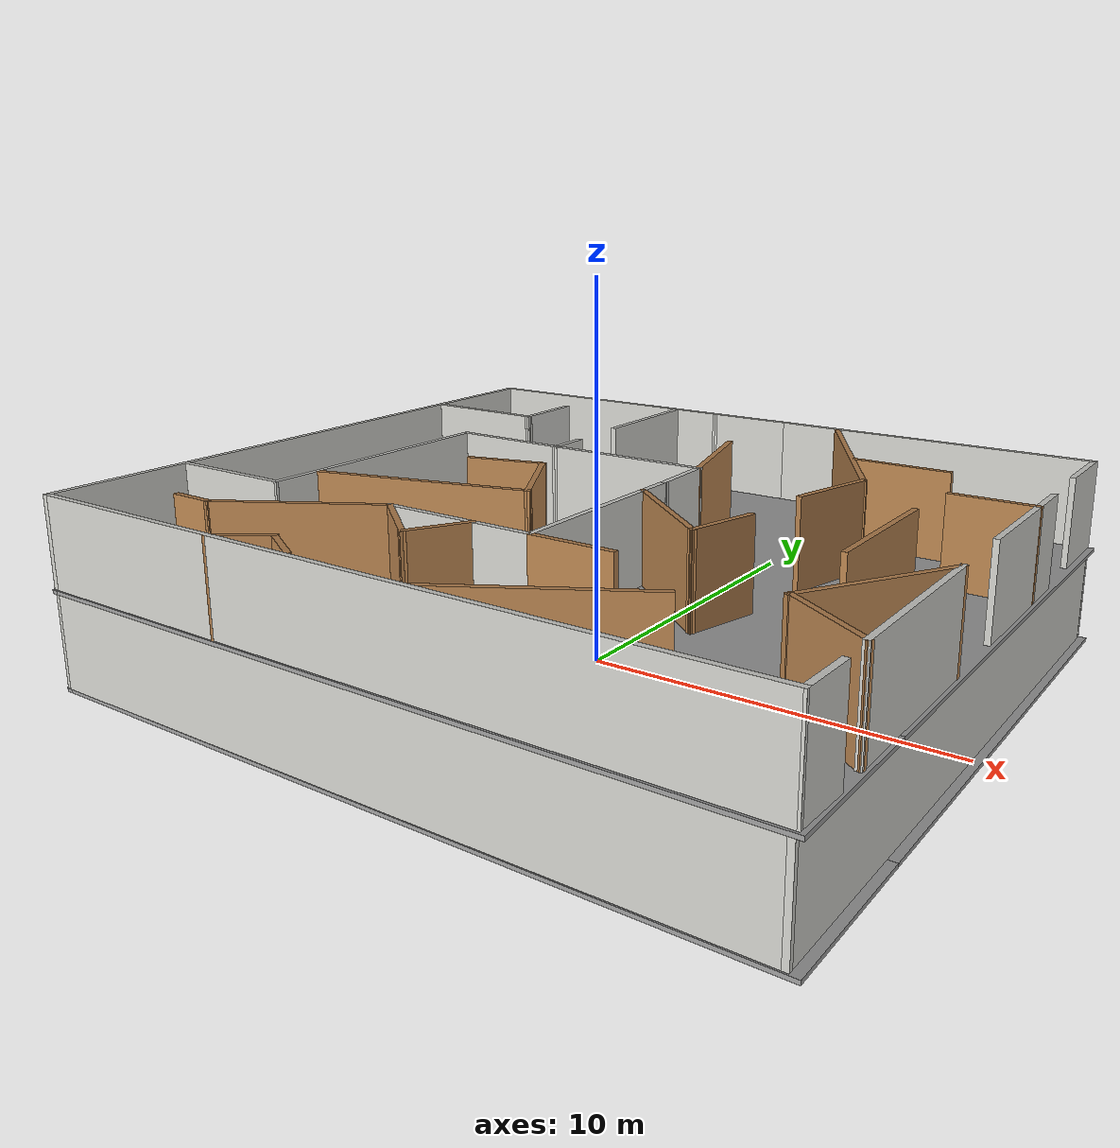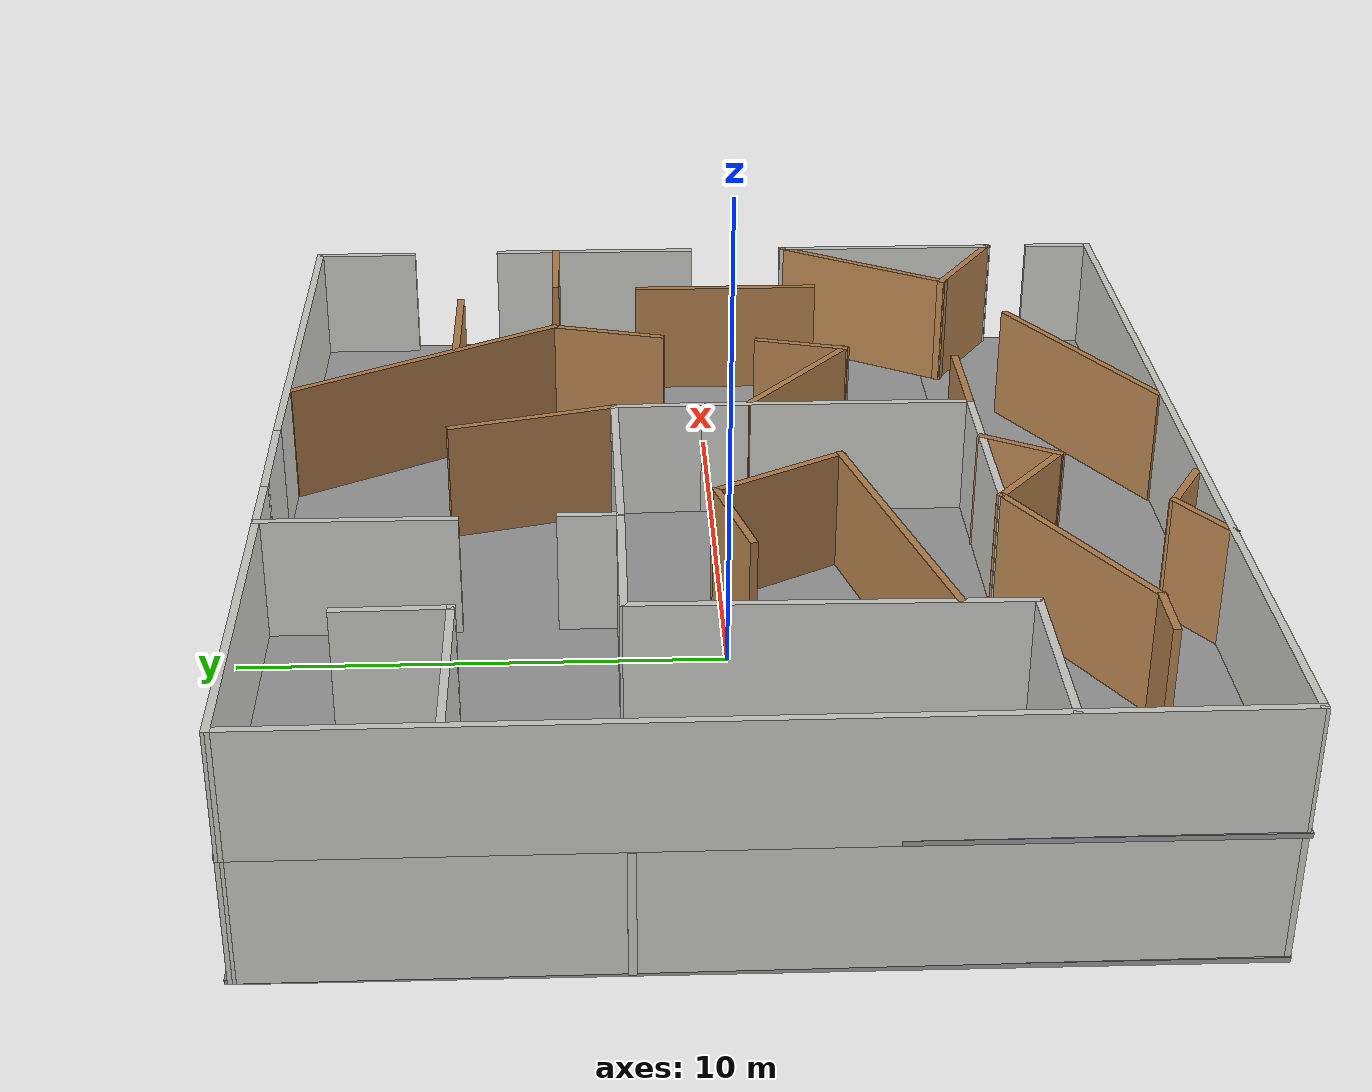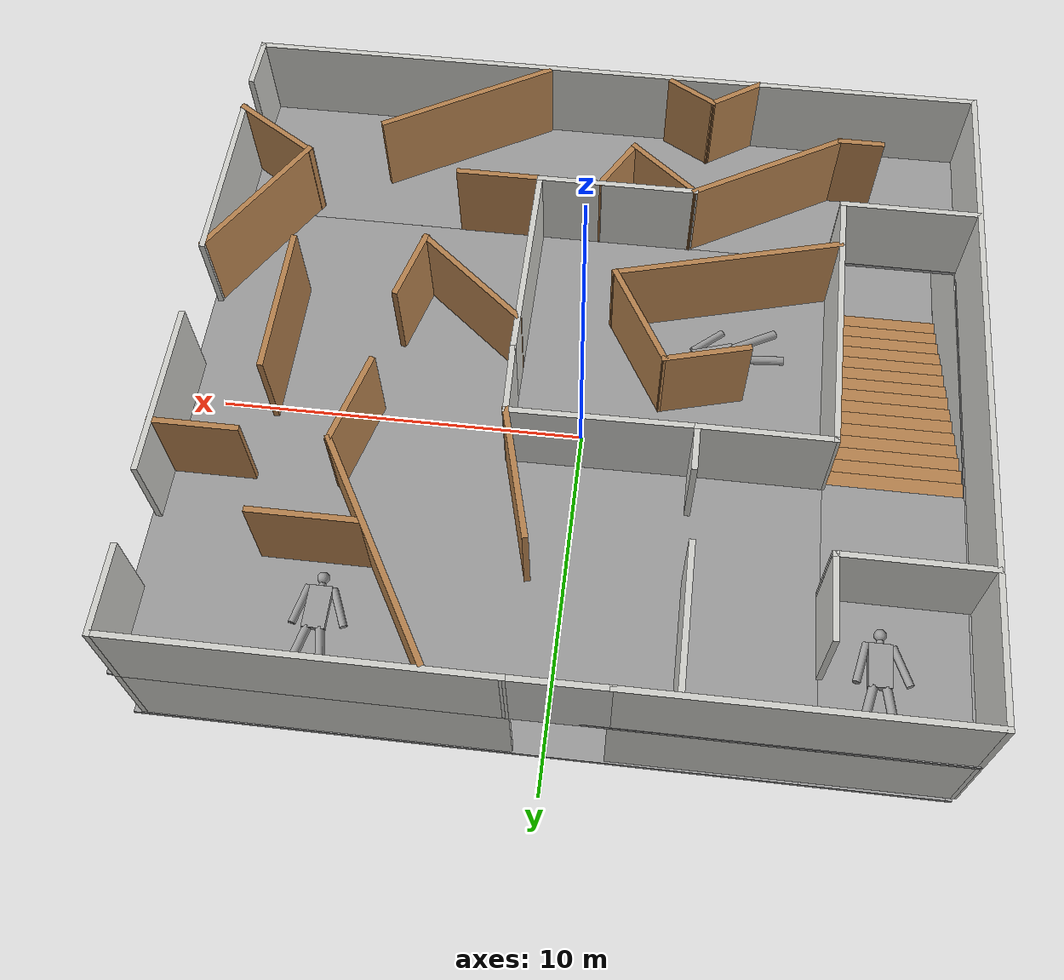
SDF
<?xml version='1.0'?>
<sdf version='1.6'>
  <model name='home_human'>
    <link name='Floor_1'>
      <pose frame=''>0.111176 -0.025995 2.5 0 -0 0</pose>
      <self_collide>0</self_collide>
      <enable_wind>0</enable_wind>
      <kinematic>0</kinematic>
      <visual name='Floor_1_Visual_1'>
        <pose frame=''>0.081642 -6.90167 0.05 0 -0 0</pose>
        <geometry>
          <box>
            <size>19.9327 4.15425 0.1</size>
          </box>
        </geometry>
        <material>
          <script>
            <uri>file://media/materials/scripts/gazebo.material</uri>
            <name>Gazebo/Grey</name>
          </script>
          <ambient>1 1 1 1</ambient>
          <shader type='pixel'/>
        </material>
        <meta>
          <layer>1</layer>
        </meta>
        <transparency>0</transparency>
        <cast_shadows>1</cast_shadows>
      </visual>
      <visual name='Floor_1_Visual_0'>
        <pose frame=''>-9.96633 0 0.05 0 -0 0</pose>
        <geometry>
          <box>
            <size>0.163285 17.9576 0.1</size>
          </box>
        </geometry>
        <material>
          <script>
            <uri>file://media/materials/scripts/gazebo.material</uri>
            <name>Gazebo/Grey</name>
          </script>
          <ambient>1 1 1 1</ambient>
          <shader type='pixel'/>
        </material>
        <meta>
          <layer>1</layer>
        </meta>
        <transparency>0</transparency>
        <cast_shadows>1</cast_shadows>
      </visual>
      <visual name='Floor_1_Visual_2'>
        <pose frame=''>1.84664 2.07713 0.05 0 -0 0</pose>
        <geometry>
          <box>
            <size>16.4027 13.8033 0.1</size>
          </box>
        </geometry>
        <material>
          <script>
            <uri>file://media/materials/scripts/gazebo.material</uri>
            <name>Gazebo/Grey</name>
          </script>
          <ambient>1 1 1 1</ambient>
          <shader type='pixel'/>
        </material>
        <meta>
          <layer>1</layer>
        </meta>
        <transparency>0</transparency>
        <cast_shadows>1</cast_shadows>
      </visual>
      <visual name='Floor_1_Visual_3'>
        <pose frame=''>-8.11969 5.56778 0.05 0 -0 0</pose>
        <geometry>
          <box>
            <size>3.53 6.82204 0.1</size>
          </box>
        </geometry>
        <material>
          <script>
            <uri>file://media/materials/scripts/gazebo.material</uri>
            <name>Gazebo/Grey</name>
          </script>
          <ambient>1 1 1 1</ambient>
          <shader type='pixel'/>
        </material>
        <meta>
          <layer>1</layer>
        </meta>
        <transparency>0</transparency>
        <cast_shadows>1</cast_shadows>
      </visual>
      <collision name='Floor_1_Collision_2'>
        <laser_retro>0</laser_retro>
        <max_contacts>10</max_contacts>
        <pose frame=''>1.84664 2.07713 0.05 0 -0 0</pose>
        <geometry>
          <box>
            <size>16.4027 13.8033 0.1</size>
          </box>
        </geometry>
        <surface>
          <friction>
            <ode>
              <mu>1</mu>
              <mu2>1</mu2>
              <fdir1>0 0 0</fdir1>
              <slip1>0</slip1>
              <slip2>0</slip2>
            </ode>
            <torsional>
              <coefficient>1</coefficient>
              <patch_radius>0</patch_radius>
              <surface_radius>0</surface_radius>
              <use_patch_radius>1</use_patch_radius>
              <ode>
                <slip>0</slip>
              </ode>
            </torsional>
          </friction>
          <bounce>
            <restitution_coefficient>0</restitution_coefficient>
            <threshold>1e+06</threshold>
          </bounce>
          <contact>
            <collide_without_contact>0</collide_without_contact>
            <collide_without_contact_bitmask>1</collide_without_contact_bitmask>
            <collide_bitmask>1</collide_bitmask>
            <ode>
              <soft_cfm>0</soft_cfm>
              <soft_erp>0.2</soft_erp>
              <kp>1e+13</kp>
              <kd>1</kd>
              <max_vel>0.01</max_vel>
              <min_depth>0</min_depth>
            </ode>
            <bullet>
              <split_impulse>1</split_impulse>
              <split_impulse_penetration_threshold>-0.01</split_impulse_penetration_threshold>
              <soft_cfm>0</soft_cfm>
              <soft_erp>0.2</soft_erp>
              <kp>1e+13</kp>
              <kd>1</kd>
            </bullet>
          </contact>
        </surface>
      </collision>
      <collision name='Floor_1_Collision_1'>
        <laser_retro>0</laser_retro>
        <max_contacts>10</max_contacts>
        <pose frame=''>0.081642 -6.90167 0.05 0 -0 0</pose>
        <geometry>
          <box>
            <size>19.9327 4.15425 0.1</size>
          </box>
        </geometry>
        <surface>
          <friction>
            <ode>
              <mu>1</mu>
              <mu2>1</mu2>
              <fdir1>0 0 0</fdir1>
              <slip1>0</slip1>
              <slip2>0</slip2>
            </ode>
            <torsional>
              <coefficient>1</coefficient>
              <patch_radius>0</patch_radius>
              <surface_radius>0</surface_radius>
              <use_patch_radius>1</use_patch_radius>
              <ode>
                <slip>0</slip>
              </ode>
            </torsional>
          </friction>
          <bounce>
            <restitution_coefficient>0</restitution_coefficient>
            <threshold>1e+06</threshold>
          </bounce>
          <contact>
            <collide_without_contact>0</collide_without_contact>
            <collide_without_contact_bitmask>1</collide_without_contact_bitmask>
            <collide_bitmask>1</collide_bitmask>
            <ode>
              <soft_cfm>0</soft_cfm>
              <soft_erp>0.2</soft_erp>
              <kp>1e+13</kp>
              <kd>1</kd>
              <max_vel>0.01</max_vel>
              <min_depth>0</min_depth>
            </ode>
            <bullet>
              <split_impulse>1</split_impulse>
              <split_impulse_penetration_threshold>-0.01</split_impulse_penetration_threshold>
              <soft_cfm>0</soft_cfm>
              <soft_erp>0.2</soft_erp>
              <kp>1e+13</kp>
              <kd>1</kd>
            </bullet>
          </contact>
        </surface>
      </collision>
      <collision name='Floor_1_Collision_0'>
        <laser_retro>0</laser_retro>
        <max_contacts>10</max_contacts>
        <pose frame=''>-9.96633 0 0.05 0 -0 0</pose>
        <geometry>
          <box>
            <size>0.163285 17.9576 0.1</size>
          </box>
        </geometry>
        <surface>
          <friction>
            <ode>
              <mu>1</mu>
              <mu2>1</mu2>
              <fdir1>0 0 0</fdir1>
              <slip1>0</slip1>
              <slip2>0</slip2>
            </ode>
            <torsional>
              <coefficient>1</coefficient>
              <patch_radius>0</patch_radius>
              <surface_radius>0</surface_radius>
              <use_patch_radius>1</use_patch_radius>
              <ode>
                <slip>0</slip>
              </ode>
            </torsional>
          </friction>
          <bounce>
            <restitution_coefficient>0</restitution_coefficient>
            <threshold>1e+06</threshold>
          </bounce>
          <contact>
            <collide_without_contact>0</collide_without_contact>
            <collide_without_contact_bitmask>1</collide_without_contact_bitmask>
            <collide_bitmask>1</collide_bitmask>
            <ode>
              <soft_cfm>0</soft_cfm>
              <soft_erp>0.2</soft_erp>
              <kp>1e+13</kp>
              <kd>1</kd>
              <max_vel>0.01</max_vel>
              <min_depth>0</min_depth>
            </ode>
            <bullet>
              <split_impulse>1</split_impulse>
              <split_impulse_penetration_threshold>-0.01</split_impulse_penetration_threshold>
              <soft_cfm>0</soft_cfm>
              <soft_erp>0.2</soft_erp>
              <kp>1e+13</kp>
              <kd>1</kd>
            </bullet>
          </contact>
        </surface>
      </collision>
      <collision name='Floor_1_Collision_3'>
        <laser_retro>0</laser_retro>
        <max_contacts>10</max_contacts>
        <pose frame=''>-8.11969 5.56778 0.05 0 -0 0</pose>
        <geometry>
          <box>
            <size>3.53 6.82204 0.1</size>
          </box>
        </geometry>
        <surface>
          <friction>
            <ode>
              <mu>1</mu>
              <mu2>1</mu2>
              <fdir1>0 0 0</fdir1>
              <slip1>0</slip1>
              <slip2>0</slip2>
            </ode>
            <torsional>
              <coefficient>1</coefficient>
              <patch_radius>0</patch_radius>
              <surface_radius>0</surface_radius>
              <use_patch_radius>1</use_patch_radius>
              <ode>
                <slip>0</slip>
              </ode>
            </torsional>
          </friction>
          <bounce>
            <restitution_coefficient>0</restitution_coefficient>
            <threshold>1e+06</threshold>
          </bounce>
          <contact>
            <collide_without_contact>0</collide_without_contact>
            <collide_without_contact_bitmask>1</collide_without_contact_bitmask>
            <collide_bitmask>1</collide_bitmask>
            <ode>
              <soft_cfm>0</soft_cfm>
              <soft_erp>0.2</soft_erp>
              <kp>1e+13</kp>
              <kd>1</kd>
              <max_vel>0.01</max_vel>
              <min_depth>0</min_depth>
            </ode>
            <bullet>
              <split_impulse>1</split_impulse>
              <split_impulse_penetration_threshold>-0.01</split_impulse_penetration_threshold>
              <soft_cfm>0</soft_cfm>
              <soft_erp>0.2</soft_erp>
              <kp>1e+13</kp>
              <kd>1</kd>
            </bullet>
          </contact>
        </surface>
      </collision>
    </link>
    <link name='Floor_1_clone'>
      <pose frame=''>0.151523 0.015351 -0.092874 0 -0 0</pose>
      <self_collide>0</self_collide>
      <enable_wind>0</enable_wind>
      <kinematic>0</kinematic>
      <visual name='Floor_1_Visual_2'>
        <pose frame=''>1.84664 2.07713 0.05 0 -0 0</pose>
        <geometry>
          <box>
            <size>16.4027 13.8033 0.1</size>
          </box>
        </geometry>
        <material>
          <script>
            <uri>file://media/materials/scripts/gazebo.material</uri>
            <name>Gazebo/Grey</name>
          </script>
          <ambient>1 1 1 1</ambient>
          <shader type='pixel'/>
        </material>
        <meta>
          <layer>1</layer>
        </meta>
        <transparency>0</transparency>
        <cast_shadows>1</cast_shadows>
      </visual>
      <visual name='Floor_1_Visual_0'>
        <pose frame=''>-9.96633 0 0.05 0 -0 0</pose>
        <geometry>
          <box>
            <size>0.163285 17.9576 0.1</size>
          </box>
        </geometry>
        <material>
          <script>
            <uri>file://media/materials/scripts/gazebo.material</uri>
            <name>Gazebo/Grey</name>
          </script>
          <ambient>1 1 1 1</ambient>
          <shader type='pixel'/>
        </material>
        <meta>
          <layer>1</layer>
        </meta>
        <transparency>0</transparency>
        <cast_shadows>1</cast_shadows>
      </visual>
      <visual name='Floor_1_Visual_3'>
        <pose frame=''>-8.11969 5.56778 0.05 0 -0 0</pose>
        <geometry>
          <box>
            <size>3.53 6.82204 0.1</size>
          </box>
        </geometry>
        <material>
          <script>
            <uri>file://media/materials/scripts/gazebo.material</uri>
            <name>Gazebo/Grey</name>
          </script>
          <ambient>1 1 1 1</ambient>
          <shader type='pixel'/>
        </material>
        <meta>
          <layer>1</layer>
        </meta>
        <transparency>0</transparency>
        <cast_shadows>1</cast_shadows>
      </visual>
      <visual name='Floor_1_Visual_1'>
        <pose frame=''>0.081642 -6.90167 0.05 0 -0 0</pose>
        <geometry>
          <box>
            <size>19.9327 4.15425 0.1</size>
          </box>
        </geometry>
        <material>
          <script>
            <uri>file://media/materials/scripts/gazebo.material</uri>
            <name>Gazebo/Grey</name>
          </script>
          <ambient>1 1 1 1</ambient>
          <shader type='pixel'/>
        </material>
        <meta>
          <layer>1</layer>
        </meta>
        <transparency>0</transparency>
        <cast_shadows>1</cast_shadows>
      </visual>
      <collision name='Floor_1_Collision_2'>
        <laser_retro>0</laser_retro>
        <max_contacts>10</max_contacts>
        <pose frame=''>1.84664 2.07713 0.05 0 -0 0</pose>
        <geometry>
          <box>
            <size>16.4027 13.8033 0.1</size>
          </box>
        </geometry>
        <surface>
          <friction>
            <ode>
              <mu>1</mu>
              <mu2>1</mu2>
              <fdir1>0 0 0</fdir1>
              <slip1>0</slip1>
              <slip2>0</slip2>
            </ode>
            <torsional>
              <coefficient>1</coefficient>
              <patch_radius>0</patch_radius>
              <surface_radius>0</surface_radius>
              <use_patch_radius>1</use_patch_radius>
              <ode>
                <slip>0</slip>
              </ode>
            </torsional>
          </friction>
          <bounce>
            <restitution_coefficient>0</restitution_coefficient>
            <threshold>1e+06</threshold>
          </bounce>
          <contact>
            <collide_without_contact>0</collide_without_contact>
            <collide_without_contact_bitmask>1</collide_without_contact_bitmask>
            <collide_bitmask>1</collide_bitmask>
            <ode>
              <soft_cfm>0</soft_cfm>
              <soft_erp>0.2</soft_erp>
              <kp>1e+13</kp>
              <kd>1</kd>
              <max_vel>0.01</max_vel>
              <min_depth>0</min_depth>
            </ode>
            <bullet>
              <split_impulse>1</split_impulse>
              <split_impulse_penetration_threshold>-0.01</split_impulse_penetration_threshold>
              <soft_cfm>0</soft_cfm>
              <soft_erp>0.2</soft_erp>
              <kp>1e+13</kp>
              <kd>1</kd>
            </bullet>
          </contact>
        </surface>
      </collision>
      <collision name='Floor_1_Collision_1'>
        <laser_retro>0</laser_retro>
        <max_contacts>10</max_contacts>
        <pose frame=''>0.081642 -6.90167 0.05 0 -0 0</pose>
        <geometry>
          <box>
            <size>19.9327 4.15425 0.1</size>
          </box>
        </geometry>
        <surface>
          <friction>
            <ode>
              <mu>1</mu>
              <mu2>1</mu2>
              <fdir1>0 0 0</fdir1>
              <slip1>0</slip1>
              <slip2>0</slip2>
            </ode>
            <torsional>
              <coefficient>1</coefficient>
              <patch_radius>0</patch_radius>
              <surface_radius>0</surface_radius>
              <use_patch_radius>1</use_patch_radius>
              <ode>
                <slip>0</slip>
              </ode>
            </torsional>
          </friction>
          <bounce>
            <restitution_coefficient>0</restitution_coefficient>
            <threshold>1e+06</threshold>
          </bounce>
          <contact>
            <collide_without_contact>0</collide_without_contact>
            <collide_without_contact_bitmask>1</collide_without_contact_bitmask>
            <collide_bitmask>1</collide_bitmask>
            <ode>
              <soft_cfm>0</soft_cfm>
              <soft_erp>0.2</soft_erp>
              <kp>1e+13</kp>
              <kd>1</kd>
              <max_vel>0.01</max_vel>
              <min_depth>0</min_depth>
            </ode>
            <bullet>
              <split_impulse>1</split_impulse>
              <split_impulse_penetration_threshold>-0.01</split_impulse_penetration_threshold>
              <soft_cfm>0</soft_cfm>
              <soft_erp>0.2</soft_erp>
              <kp>1e+13</kp>
              <kd>1</kd>
            </bullet>
          </contact>
        </surface>
      </collision>
      <collision name='Floor_1_Collision_0'>
        <laser_retro>0</laser_retro>
        <max_contacts>10</max_contacts>
        <pose frame=''>-9.96633 0 0.05 0 -0 0</pose>
        <geometry>
          <box>
            <size>0.163285 17.9576 0.1</size>
          </box>
        </geometry>
        <surface>
          <friction>
            <ode>
              <mu>1</mu>
              <mu2>1</mu2>
              <fdir1>0 0 0</fdir1>
              <slip1>0</slip1>
              <slip2>0</slip2>
            </ode>
            <torsional>
              <coefficient>1</coefficient>
              <patch_radius>0</patch_radius>
              <surface_radius>0</surface_radius>
              <use_patch_radius>1</use_patch_radius>
              <ode>
                <slip>0</slip>
              </ode>
            </torsional>
          </friction>
          <bounce>
            <restitution_coefficient>0</restitution_coefficient>
            <threshold>1e+06</threshold>
          </bounce>
          <contact>
            <collide_without_contact>0</collide_without_contact>
            <collide_without_contact_bitmask>1</collide_without_contact_bitmask>
            <collide_bitmask>1</collide_bitmask>
            <ode>
              <soft_cfm>0</soft_cfm>
              <soft_erp>0.2</soft_erp>
              <kp>1e+13</kp>
              <kd>1</kd>
              <max_vel>0.01</max_vel>
              <min_depth>0</min_depth>
            </ode>
            <bullet>
              <split_impulse>1</split_impulse>
              <split_impulse_penetration_threshold>-0.01</split_impulse_penetration_threshold>
              <soft_cfm>0</soft_cfm>
              <soft_erp>0.2</soft_erp>
              <kp>1e+13</kp>
              <kd>1</kd>
            </bullet>
          </contact>
        </surface>
      </collision>
      <collision name='Floor_1_Collision_3'>
        <laser_retro>0</laser_retro>
        <max_contacts>10</max_contacts>
        <pose frame=''>-8.11969 5.56778 0.05 0 -0 0</pose>
        <geometry>
          <box>
            <size>3.53 6.82204 0.1</size>
          </box>
        </geometry>
        <surface>
          <friction>
            <ode>
              <mu>1</mu>
              <mu2>1</mu2>
              <fdir1>0 0 0</fdir1>
              <slip1>0</slip1>
              <slip2>0</slip2>
            </ode>
            <torsional>
              <coefficient>1</coefficient>
              <patch_radius>0</patch_radius>
              <surface_radius>0</surface_radius>
              <use_patch_radius>1</use_patch_radius>
              <ode>
                <slip>0</slip>
              </ode>
            </torsional>
          </friction>
          <bounce>
            <restitution_coefficient>0</restitution_coefficient>
            <threshold>1e+06</threshold>
          </bounce>
          <contact>
            <collide_without_contact>0</collide_without_contact>
            <collide_without_contact_bitmask>1</collide_without_contact_bitmask>
            <collide_bitmask>1</collide_bitmask>
            <ode>
              <soft_cfm>0</soft_cfm>
              <soft_erp>0.2</soft_erp>
              <kp>1e+13</kp>
              <kd>1</kd>
              <max_vel>0.01</max_vel>
              <min_depth>0</min_depth>
            </ode>
            <bullet>
              <split_impulse>1</split_impulse>
              <split_impulse_penetration_threshold>-0.01</split_impulse_penetration_threshold>
              <soft_cfm>0</soft_cfm>
              <soft_erp>0.2</soft_erp>
              <kp>1e+13</kp>
              <kd>1</kd>
            </bullet>
          </contact>
        </surface>
      </collision>
    </link>
    <link name='Stairs_0'>
      <self_collide>0</self_collide>
      <enable_wind>0</enable_wind>
      <kinematic>0</kinematic>
      <pose frame=''>0 0 0 0 -0 0</pose>
      <visual name='Stairs_0_Visual_13'>
        <pose frame=''>-8.0684 1.44808 2.25 0 -0 -3.14159</pose>
        <geometry>
          <box>
            <size>3.53 0.46542 0.166667</size>
          </box>
        </geometry>
        <material>
          <script>
            <uri>file://media/materials/scripts/gazebo.material</uri>
            <name>Gazebo/Wood</name>
          </script>
          <ambient>1 1 1 1</ambient>
          <shader type='pixel'/>
        </material>
        <meta>
          <layer>0</layer>
        </meta>
        <transparency>0</transparency>
        <cast_shadows>1</cast_shadows>
      </visual>
      <visual name='Stairs_0_Visual_1'>
        <pose frame=''>-8.0684 -4.13696 0.25 0 -0 -3.14159</pose>
        <geometry>
          <box>
            <size>3.53 0.46542 0.166667</size>
          </box>
        </geometry>
        <material>
          <script>
            <uri>file://media/materials/scripts/gazebo.material</uri>
            <name>Gazebo/Wood</name>
          </script>
          <ambient>1 1 1 1</ambient>
          <shader type='pixel'/>
        </material>
        <meta>
          <layer>0</layer>
        </meta>
        <transparency>0</transparency>
        <cast_shadows>1</cast_shadows>
      </visual>
      <visual name='Stairs_0_Visual_10'>
        <pose frame=''>-8.0684 0.051817 1.75 0 -0 -3.14159</pose>
        <geometry>
          <box>
            <size>3.53 0.46542 0.166667</size>
          </box>
        </geometry>
        <material>
          <script>
            <uri>file://media/materials/scripts/gazebo.material</uri>
            <name>Gazebo/Wood</name>
          </script>
          <ambient>1 1 1 1</ambient>
          <shader type='pixel'/>
        </material>
        <meta>
          <layer>0</layer>
        </meta>
        <transparency>0</transparency>
        <cast_shadows>1</cast_shadows>
      </visual>
      <visual name='Stairs_0_Visual_8'>
        <pose frame=''>-8.0684 -0.879023 1.41667 0 -0 -3.14159</pose>
        <geometry>
          <box>
            <size>3.53 0.46542 0.166667</size>
          </box>
        </geometry>
        <material>
          <script>
            <uri>file://media/materials/scripts/gazebo.material</uri>
            <name>Gazebo/Wood</name>
          </script>
          <ambient>1 1 1 1</ambient>
          <shader type='pixel'/>
        </material>
        <meta>
          <layer>0</layer>
        </meta>
        <transparency>0</transparency>
        <cast_shadows>1</cast_shadows>
      </visual>
      <visual name='Stairs_0_Visual_0'>
        <pose frame=''>-8.0684 -4.60238 0.083333 0 -0 -3.14159</pose>
        <geometry>
          <box>
            <size>3.53 0.46542 0.166667</size>
          </box>
        </geometry>
        <material>
          <script>
            <uri>file://media/materials/scripts/gazebo.material</uri>
            <name>Gazebo/Wood</name>
          </script>
          <ambient>1 1 1 1</ambient>
          <shader type='pixel'/>
        </material>
        <meta>
          <layer>0</layer>
        </meta>
        <transparency>0</transparency>
        <cast_shadows>1</cast_shadows>
      </visual>
      <visual name='Stairs_0_Visual_14'>
        <pose frame=''>-8.0684 1.9135 2.41667 0 -0 -3.14159</pose>
        <geometry>
          <box>
            <size>3.53 0.46542 0.166667</size>
          </box>
        </geometry>
        <material>
          <script>
            <uri>file://media/materials/scripts/gazebo.material</uri>
            <name>Gazebo/Wood</name>
          </script>
          <ambient>1 1 1 1</ambient>
          <shader type='pixel'/>
        </material>
        <meta>
          <layer>0</layer>
        </meta>
        <transparency>0</transparency>
        <cast_shadows>1</cast_shadows>
      </visual>
      <visual name='Stairs_0_Visual_5'>
        <pose frame=''>-8.0684 -2.27528 0.916667 0 -0 -3.14159</pose>
        <geometry>
          <box>
            <size>3.53 0.46542 0.166667</size>
          </box>
        </geometry>
        <material>
          <script>
            <uri>file://media/materials/scripts/gazebo.material</uri>
            <name>Gazebo/Wood</name>
          </script>
          <ambient>1 1 1 1</ambient>
          <shader type='pixel'/>
        </material>
        <meta>
          <layer>0</layer>
        </meta>
        <transparency>0</transparency>
        <cast_shadows>1</cast_shadows>
      </visual>
      <visual name='Stairs_0_Visual_11'>
        <pose frame=''>-8.0684 0.517237 1.91667 0 -0 -3.14159</pose>
        <geometry>
          <box>
            <size>3.53 0.46542 0.166667</size>
          </box>
        </geometry>
        <material>
          <script>
            <uri>file://media/materials/scripts/gazebo.material</uri>
            <name>Gazebo/Wood</name>
          </script>
          <ambient>1 1 1 1</ambient>
          <shader type='pixel'/>
        </material>
        <meta>
          <layer>0</layer>
        </meta>
        <transparency>0</transparency>
        <cast_shadows>1</cast_shadows>
      </visual>
      <visual name='Stairs_0_Visual_2'>
        <pose frame=''>-8.0684 -3.67154 0.416667 0 -0 -3.14159</pose>
        <geometry>
          <box>
            <size>3.53 0.46542 0.166667</size>
          </box>
        </geometry>
        <material>
          <script>
            <uri>file://media/materials/scripts/gazebo.material</uri>
            <name>Gazebo/Wood</name>
          </script>
          <ambient>1 1 1 1</ambient>
          <shader type='pixel'/>
        </material>
        <meta>
          <layer>0</layer>
        </meta>
        <transparency>0</transparency>
        <cast_shadows>1</cast_shadows>
      </visual>
      <visual name='Stairs_0_Visual_7'>
        <pose frame=''>-8.0684 -1.34444 1.25 0 -0 -3.14159</pose>
        <geometry>
          <box>
            <size>3.53 0.46542 0.166667</size>
          </box>
        </geometry>
        <material>
          <script>
            <uri>file://media/materials/scripts/gazebo.material</uri>
            <name>Gazebo/Wood</name>
          </script>
          <ambient>1 1 1 1</ambient>
          <shader type='pixel'/>
        </material>
        <meta>
          <layer>0</layer>
        </meta>
        <transparency>0</transparency>
        <cast_shadows>1</cast_shadows>
      </visual>
      <visual name='Stairs_0_Visual_12'>
        <pose frame=''>-8.0684 0.982657 2.08333 0 -0 -3.14159</pose>
        <geometry>
          <box>
            <size>3.53 0.46542 0.166667</size>
          </box>
        </geometry>
        <material>
          <script>
            <uri>file://media/materials/scripts/gazebo.material</uri>
            <name>Gazebo/Wood</name>
          </script>
          <ambient>1 1 1 1</ambient>
          <shader type='pixel'/>
        </material>
        <meta>
          <layer>0</layer>
        </meta>
        <transparency>0</transparency>
        <cast_shadows>1</cast_shadows>
      </visual>
      <visual name='Stairs_0_Visual_3'>
        <pose frame=''>-8.0684 -3.20612 0.583333 0 -0 -3.14159</pose>
        <geometry>
          <box>
            <size>3.53 0.46542 0.166667</size>
          </box>
        </geometry>
        <material>
          <script>
            <uri>file://media/materials/scripts/gazebo.material</uri>
            <name>Gazebo/Wood</name>
          </script>
          <ambient>1 1 1 1</ambient>
          <shader type='pixel'/>
        </material>
        <meta>
          <layer>0</layer>
        </meta>
        <transparency>0</transparency>
        <cast_shadows>1</cast_shadows>
      </visual>
      <visual name='Stairs_0_Visual_9'>
        <pose frame=''>-8.0684 -0.413603 1.58333 0 -0 -3.14159</pose>
        <geometry>
          <box>
            <size>3.53 0.46542 0.166667</size>
          </box>
        </geometry>
        <material>
          <script>
            <uri>file://media/materials/scripts/gazebo.material</uri>
            <name>Gazebo/Wood</name>
          </script>
          <ambient>1 1 1 1</ambient>
          <shader type='pixel'/>
        </material>
        <meta>
          <layer>0</layer>
        </meta>
        <transparency>0</transparency>
        <cast_shadows>1</cast_shadows>
      </visual>
      <visual name='Stairs_0_Visual_6'>
        <pose frame=''>-8.0684 -1.80986 1.08333 0 -0 -3.14159</pose>
        <geometry>
          <box>
            <size>3.53 0.46542 0.166667</size>
          </box>
        </geometry>
        <material>
          <script>
            <uri>file://media/materials/scripts/gazebo.material</uri>
            <name>Gazebo/Wood</name>
          </script>
          <ambient>1 1 1 1</ambient>
          <shader type='pixel'/>
        </material>
        <meta>
          <layer>0</layer>
        </meta>
        <transparency>0</transparency>
        <cast_shadows>1</cast_shadows>
      </visual>
      <visual name='Stairs_0_Visual_4'>
        <pose frame=''>-8.0684 -2.7407 0.75 0 -0 -3.14159</pose>
        <geometry>
          <box>
            <size>3.53 0.46542 0.166667</size>
          </box>
        </geometry>
        <material>
          <script>
            <uri>file://media/materials/scripts/gazebo.material</uri>
            <name>Gazebo/Wood</name>
          </script>
          <ambient>1 1 1 1</ambient>
          <shader type='pixel'/>
        </material>
        <meta>
          <layer>0</layer>
        </meta>
        <transparency>0</transparency>
        <cast_shadows>1</cast_shadows>
      </visual>
      <collision name='Stairs_0_Collision_0'>
        <laser_retro>0</laser_retro>
        <max_contacts>10</max_contacts>
        <pose frame=''>-8.0684 -4.60238 0.083333 0 0 -3.14159</pose>
        <geometry>
          <box>
            <size>3.53 0.46542 0.166667</size>
          </box>
        </geometry>
        <surface>
          <friction>
            <ode>
              <mu>1</mu>
              <mu2>1</mu2>
              <fdir1>0 0 0</fdir1>
              <slip1>0</slip1>
              <slip2>0</slip2>
            </ode>
            <torsional>
              <coefficient>1</coefficient>
              <patch_radius>0</patch_radius>
              <surface_radius>0</surface_radius>
              <use_patch_radius>1</use_patch_radius>
              <ode>
                <slip>0</slip>
              </ode>
            </torsional>
          </friction>
          <bounce>
            <restitution_coefficient>0</restitution_coefficient>
            <threshold>1e+06</threshold>
          </bounce>
          <contact>
            <collide_without_contact>0</collide_without_contact>
            <collide_without_contact_bitmask>1</collide_without_contact_bitmask>
            <collide_bitmask>1</collide_bitmask>
            <ode>
              <soft_cfm>0</soft_cfm>
              <soft_erp>0.2</soft_erp>
              <kp>1e+13</kp>
              <kd>1</kd>
              <max_vel>0.01</max_vel>
              <min_depth>0</min_depth>
            </ode>
            <bullet>
              <split_impulse>1</split_impulse>
              <split_impulse_penetration_threshold>-0.01</split_impulse_penetration_threshold>
              <soft_cfm>0</soft_cfm>
              <soft_erp>0.2</soft_erp>
              <kp>1e+13</kp>
              <kd>1</kd>
            </bullet>
          </contact>
        </surface>
      </collision>
      <collision name='Stairs_0_Collision_8'>
        <laser_retro>0</laser_retro>
        <max_contacts>10</max_contacts>
        <pose frame=''>-8.0684 -0.879023 1.41667 0 0 -3.14159</pose>
        <geometry>
          <box>
            <size>3.53 0.46542 0.166667</size>
          </box>
        </geometry>
        <surface>
          <friction>
            <ode>
              <mu>1</mu>
              <mu2>1</mu2>
              <fdir1>0 0 0</fdir1>
              <slip1>0</slip1>
              <slip2>0</slip2>
            </ode>
            <torsional>
              <coefficient>1</coefficient>
              <patch_radius>0</patch_radius>
              <surface_radius>0</surface_radius>
              <use_patch_radius>1</use_patch_radius>
              <ode>
                <slip>0</slip>
              </ode>
            </torsional>
          </friction>
          <bounce>
            <restitution_coefficient>0</restitution_coefficient>
            <threshold>1e+06</threshold>
          </bounce>
          <contact>
            <collide_without_contact>0</collide_without_contact>
            <collide_without_contact_bitmask>1</collide_without_contact_bitmask>
            <collide_bitmask>1</collide_bitmask>
            <ode>
              <soft_cfm>0</soft_cfm>
              <soft_erp>0.2</soft_erp>
              <kp>1e+13</kp>
              <kd>1</kd>
              <max_vel>0.01</max_vel>
              <min_depth>0</min_depth>
            </ode>
            <bullet>
              <split_impulse>1</split_impulse>
              <split_impulse_penetration_threshold>-0.01</split_impulse_penetration_threshold>
              <soft_cfm>0</soft_cfm>
              <soft_erp>0.2</soft_erp>
              <kp>1e+13</kp>
              <kd>1</kd>
            </bullet>
          </contact>
        </surface>
      </collision>
      <collision name='Stairs_0_Collision_1'>
        <laser_retro>0</laser_retro>
        <max_contacts>10</max_contacts>
        <pose frame=''>-8.0684 -4.13696 0.25 0 0 -3.14159</pose>
        <geometry>
          <box>
            <size>3.53 0.46542 0.166667</size>
          </box>
        </geometry>
        <surface>
          <friction>
            <ode>
              <mu>1</mu>
              <mu2>1</mu2>
              <fdir1>0 0 0</fdir1>
              <slip1>0</slip1>
              <slip2>0</slip2>
            </ode>
            <torsional>
              <coefficient>1</coefficient>
              <patch_radius>0</patch_radius>
              <surface_radius>0</surface_radius>
              <use_patch_radius>1</use_patch_radius>
              <ode>
                <slip>0</slip>
              </ode>
            </torsional>
          </friction>
          <bounce>
            <restitution_coefficient>0</restitution_coefficient>
            <threshold>1e+06</threshold>
          </bounce>
          <contact>
            <collide_without_contact>0</collide_without_contact>
            <collide_without_contact_bitmask>1</collide_without_contact_bitmask>
            <collide_bitmask>1</collide_bitmask>
            <ode>
              <soft_cfm>0</soft_cfm>
              <soft_erp>0.2</soft_erp>
              <kp>1e+13</kp>
              <kd>1</kd>
              <max_vel>0.01</max_vel>
              <min_depth>0</min_depth>
            </ode>
            <bullet>
              <split_impulse>1</split_impulse>
              <split_impulse_penetration_threshold>-0.01</split_impulse_penetration_threshold>
              <soft_cfm>0</soft_cfm>
              <soft_erp>0.2</soft_erp>
              <kp>1e+13</kp>
              <kd>1</kd>
            </bullet>
          </contact>
        </surface>
      </collision>
      <collision name='Stairs_0_Collision_6'>
        <laser_retro>0</laser_retro>
        <max_contacts>10</max_contacts>
        <pose frame=''>-8.0684 -1.80986 1.08333 0 0 -3.14159</pose>
        <geometry>
          <box>
            <size>3.53 0.46542 0.166667</size>
          </box>
        </geometry>
        <surface>
          <friction>
            <ode>
              <mu>1</mu>
              <mu2>1</mu2>
              <fdir1>0 0 0</fdir1>
              <slip1>0</slip1>
              <slip2>0</slip2>
            </ode>
            <torsional>
              <coefficient>1</coefficient>
              <patch_radius>0</patch_radius>
              <surface_radius>0</surface_radius>
              <use_patch_radius>1</use_patch_radius>
              <ode>
                <slip>0</slip>
              </ode>
            </torsional>
          </friction>
          <bounce>
            <restitution_coefficient>0</restitution_coefficient>
            <threshold>1e+06</threshold>
          </bounce>
          <contact>
            <collide_without_contact>0</collide_without_contact>
            <collide_without_contact_bitmask>1</collide_without_contact_bitmask>
            <collide_bitmask>1</collide_bitmask>
            <ode>
              <soft_cfm>0</soft_cfm>
              <soft_erp>0.2</soft_erp>
              <kp>1e+13</kp>
              <kd>1</kd>
              <max_vel>0.01</max_vel>
              <min_depth>0</min_depth>
            </ode>
            <bullet>
              <split_impulse>1</split_impulse>
              <split_impulse_penetration_threshold>-0.01</split_impulse_penetration_threshold>
              <soft_cfm>0</soft_cfm>
              <soft_erp>0.2</soft_erp>
              <kp>1e+13</kp>
              <kd>1</kd>
            </bullet>
          </contact>
        </surface>
      </collision>
      <collision name='Stairs_0_Collision_2'>
        <laser_retro>0</laser_retro>
        <max_contacts>10</max_contacts>
        <pose frame=''>-8.0684 -3.67154 0.416667 0 0 -3.14159</pose>
        <geometry>
          <box>
            <size>3.53 0.46542 0.166667</size>
          </box>
        </geometry>
        <surface>
          <friction>
            <ode>
              <mu>1</mu>
              <mu2>1</mu2>
              <fdir1>0 0 0</fdir1>
              <slip1>0</slip1>
              <slip2>0</slip2>
            </ode>
            <torsional>
              <coefficient>1</coefficient>
              <patch_radius>0</patch_radius>
              <surface_radius>0</surface_radius>
              <use_patch_radius>1</use_patch_radius>
              <ode>
                <slip>0</slip>
              </ode>
            </torsional>
          </friction>
          <bounce>
            <restitution_coefficient>0</restitution_coefficient>
            <threshold>1e+06</threshold>
          </bounce>
          <contact>
            <collide_without_contact>0</collide_without_contact>
            <collide_without_contact_bitmask>1</collide_without_contact_bitmask>
            <collide_bitmask>1</collide_bitmask>
            <ode>
              <soft_cfm>0</soft_cfm>
              <soft_erp>0.2</soft_erp>
              <kp>1e+13</kp>
              <kd>1</kd>
              <max_vel>0.01</max_vel>
              <min_depth>0</min_depth>
            </ode>
            <bullet>
              <split_impulse>1</split_impulse>
              <split_impulse_penetration_threshold>-0.01</split_impulse_penetration_threshold>
              <soft_cfm>0</soft_cfm>
              <soft_erp>0.2</soft_erp>
              <kp>1e+13</kp>
              <kd>1</kd>
            </bullet>
          </contact>
        </surface>
      </collision>
      <collision name='Stairs_0_Collision_3'>
        <laser_retro>0</laser_retro>
        <max_contacts>10</max_contacts>
        <pose frame=''>-8.0684 -3.20612 0.583333 0 0 -3.14159</pose>
        <geometry>
          <box>
            <size>3.53 0.46542 0.166667</size>
          </box>
        </geometry>
        <surface>
          <friction>
            <ode>
              <mu>1</mu>
              <mu2>1</mu2>
              <fdir1>0 0 0</fdir1>
              <slip1>0</slip1>
              <slip2>0</slip2>
            </ode>
            <torsional>
              <coefficient>1</coefficient>
              <patch_radius>0</patch_radius>
              <surface_radius>0</surface_radius>
              <use_patch_radius>1</use_patch_radius>
              <ode>
                <slip>0</slip>
              </ode>
            </torsional>
          </friction>
          <bounce>
            <restitution_coefficient>0</restitution_coefficient>
            <threshold>1e+06</threshold>
          </bounce>
          <contact>
            <collide_without_contact>0</collide_without_contact>
            <collide_without_contact_bitmask>1</collide_without_contact_bitmask>
            <collide_bitmask>1</collide_bitmask>
            <ode>
              <soft_cfm>0</soft_cfm>
              <soft_erp>0.2</soft_erp>
              <kp>1e+13</kp>
              <kd>1</kd>
              <max_vel>0.01</max_vel>
              <min_depth>0</min_depth>
            </ode>
            <bullet>
              <split_impulse>1</split_impulse>
              <split_impulse_penetration_threshold>-0.01</split_impulse_penetration_threshold>
              <soft_cfm>0</soft_cfm>
              <soft_erp>0.2</soft_erp>
              <kp>1e+13</kp>
              <kd>1</kd>
            </bullet>
          </contact>
        </surface>
      </collision>
      <collision name='Stairs_0_Collision_13'>
        <laser_retro>0</laser_retro>
        <max_contacts>10</max_contacts>
        <pose frame=''>-8.0684 1.44808 2.25 0 0 -3.14159</pose>
        <geometry>
          <box>
            <size>3.53 0.46542 0.166667</size>
          </box>
        </geometry>
        <surface>
          <friction>
            <ode>
              <mu>1</mu>
              <mu2>1</mu2>
              <fdir1>0 0 0</fdir1>
              <slip1>0</slip1>
              <slip2>0</slip2>
            </ode>
            <torsional>
              <coefficient>1</coefficient>
              <patch_radius>0</patch_radius>
              <surface_radius>0</surface_radius>
              <use_patch_radius>1</use_patch_radius>
              <ode>
                <slip>0</slip>
              </ode>
            </torsional>
          </friction>
          <bounce>
            <restitution_coefficient>0</restitution_coefficient>
            <threshold>1e+06</threshold>
          </bounce>
          <contact>
            <collide_without_contact>0</collide_without_contact>
            <collide_without_contact_bitmask>1</collide_without_contact_bitmask>
            <collide_bitmask>1</collide_bitmask>
            <ode>
              <soft_cfm>0</soft_cfm>
              <soft_erp>0.2</soft_erp>
              <kp>1e+13</kp>
              <kd>1</kd>
              <max_vel>0.01</max_vel>
              <min_depth>0</min_depth>
            </ode>
            <bullet>
              <split_impulse>1</split_impulse>
              <split_impulse_penetration_threshold>-0.01</split_impulse_penetration_threshold>
              <soft_cfm>0</soft_cfm>
              <soft_erp>0.2</soft_erp>
              <kp>1e+13</kp>
              <kd>1</kd>
            </bullet>
          </contact>
        </surface>
      </collision>
      <collision name='Stairs_0_Collision_10'>
        <laser_retro>0</laser_retro>
        <max_contacts>10</max_contacts>
        <pose frame=''>-8.0684 0.051817 1.75 0 0 -3.14159</pose>
        <geometry>
          <box>
            <size>3.53 0.46542 0.166667</size>
          </box>
        </geometry>
        <surface>
          <friction>
            <ode>
              <mu>1</mu>
              <mu2>1</mu2>
              <fdir1>0 0 0</fdir1>
              <slip1>0</slip1>
              <slip2>0</slip2>
            </ode>
            <torsional>
              <coefficient>1</coefficient>
              <patch_radius>0</patch_radius>
              <surface_radius>0</surface_radius>
              <use_patch_radius>1</use_patch_radius>
              <ode>
                <slip>0</slip>
              </ode>
            </torsional>
          </friction>
          <bounce>
            <restitution_coefficient>0</restitution_coefficient>
            <threshold>1e+06</threshold>
          </bounce>
          <contact>
            <collide_without_contact>0</collide_without_contact>
            <collide_without_contact_bitmask>1</collide_without_contact_bitmask>
            <collide_bitmask>1</collide_bitmask>
            <ode>
              <soft_cfm>0</soft_cfm>
              <soft_erp>0.2</soft_erp>
              <kp>1e+13</kp>
              <kd>1</kd>
              <max_vel>0.01</max_vel>
              <min_depth>0</min_depth>
            </ode>
            <bullet>
              <split_impulse>1</split_impulse>
              <split_impulse_penetration_threshold>-0.01</split_impulse_penetration_threshold>
              <soft_cfm>0</soft_cfm>
              <soft_erp>0.2</soft_erp>
              <kp>1e+13</kp>
              <kd>1</kd>
            </bullet>
          </contact>
        </surface>
      </collision>
      <collision name='Stairs_0_Collision_9'>
        <laser_retro>0</laser_retro>
        <max_contacts>10</max_contacts>
        <pose frame=''>-8.0684 -0.413603 1.58333 0 0 -3.14159</pose>
        <geometry>
          <box>
            <size>3.53 0.46542 0.166667</size>
          </box>
        </geometry>
        <surface>
          <friction>
            <ode>
              <mu>1</mu>
              <mu2>1</mu2>
              <fdir1>0 0 0</fdir1>
              <slip1>0</slip1>
              <slip2>0</slip2>
            </ode>
            <torsional>
              <coefficient>1</coefficient>
              <patch_radius>0</patch_radius>
              <surface_radius>0</surface_radius>
              <use_patch_radius>1</use_patch_radius>
              <ode>
                <slip>0</slip>
              </ode>
            </torsional>
          </friction>
          <bounce>
            <restitution_coefficient>0</restitution_coefficient>
            <threshold>1e+06</threshold>
          </bounce>
          <contact>
            <collide_without_contact>0</collide_without_contact>
            <collide_without_contact_bitmask>1</collide_without_contact_bitmask>
            <collide_bitmask>1</collide_bitmask>
            <ode>
              <soft_cfm>0</soft_cfm>
              <soft_erp>0.2</soft_erp>
              <kp>1e+13</kp>
              <kd>1</kd>
              <max_vel>0.01</max_vel>
              <min_depth>0</min_depth>
            </ode>
            <bullet>
              <split_impulse>1</split_impulse>
              <split_impulse_penetration_threshold>-0.01</split_impulse_penetration_threshold>
              <soft_cfm>0</soft_cfm>
              <soft_erp>0.2</soft_erp>
              <kp>1e+13</kp>
              <kd>1</kd>
            </bullet>
          </contact>
        </surface>
      </collision>
      <collision name='Stairs_0_Collision_7'>
        <laser_retro>0</laser_retro>
        <max_contacts>10</max_contacts>
        <pose frame=''>-8.0684 -1.34444 1.25 0 0 -3.14159</pose>
        <geometry>
          <box>
            <size>3.53 0.46542 0.166667</size>
          </box>
        </geometry>
        <surface>
          <friction>
            <ode>
              <mu>1</mu>
              <mu2>1</mu2>
              <fdir1>0 0 0</fdir1>
              <slip1>0</slip1>
              <slip2>0</slip2>
            </ode>
            <torsional>
              <coefficient>1</coefficient>
              <patch_radius>0</patch_radius>
              <surface_radius>0</surface_radius>
              <use_patch_radius>1</use_patch_radius>
              <ode>
                <slip>0</slip>
              </ode>
            </torsional>
          </friction>
          <bounce>
            <restitution_coefficient>0</restitution_coefficient>
            <threshold>1e+06</threshold>
          </bounce>
          <contact>
            <collide_without_contact>0</collide_without_contact>
            <collide_without_contact_bitmask>1</collide_without_contact_bitmask>
            <collide_bitmask>1</collide_bitmask>
            <ode>
              <soft_cfm>0</soft_cfm>
              <soft_erp>0.2</soft_erp>
              <kp>1e+13</kp>
              <kd>1</kd>
              <max_vel>0.01</max_vel>
              <min_depth>0</min_depth>
            </ode>
            <bullet>
              <split_impulse>1</split_impulse>
              <split_impulse_penetration_threshold>-0.01</split_impulse_penetration_threshold>
              <soft_cfm>0</soft_cfm>
              <soft_erp>0.2</soft_erp>
              <kp>1e+13</kp>
              <kd>1</kd>
            </bullet>
          </contact>
        </surface>
      </collision>
      <collision name='Stairs_0_Collision_14'>
        <laser_retro>0</laser_retro>
        <max_contacts>10</max_contacts>
        <pose frame=''>-8.0684 1.9135 2.41667 0 0 -3.14159</pose>
        <geometry>
          <box>
            <size>3.53 0.46542 0.166667</size>
          </box>
        </geometry>
        <surface>
          <friction>
            <ode>
              <mu>1</mu>
              <mu2>1</mu2>
              <fdir1>0 0 0</fdir1>
              <slip1>0</slip1>
              <slip2>0</slip2>
            </ode>
            <torsional>
              <coefficient>1</coefficient>
              <patch_radius>0</patch_radius>
              <surface_radius>0</surface_radius>
              <use_patch_radius>1</use_patch_radius>
              <ode>
                <slip>0</slip>
              </ode>
            </torsional>
          </friction>
          <bounce>
            <restitution_coefficient>0</restitution_coefficient>
            <threshold>1e+06</threshold>
          </bounce>
          <contact>
            <collide_without_contact>0</collide_without_contact>
            <collide_without_contact_bitmask>1</collide_without_contact_bitmask>
            <collide_bitmask>1</collide_bitmask>
            <ode>
              <soft_cfm>0</soft_cfm>
              <soft_erp>0.2</soft_erp>
              <kp>1e+13</kp>
              <kd>1</kd>
              <max_vel>0.01</max_vel>
              <min_depth>0</min_depth>
            </ode>
            <bullet>
              <split_impulse>1</split_impulse>
              <split_impulse_penetration_threshold>-0.01</split_impulse_penetration_threshold>
              <soft_cfm>0</soft_cfm>
              <soft_erp>0.2</soft_erp>
              <kp>1e+13</kp>
              <kd>1</kd>
            </bullet>
          </contact>
        </surface>
      </collision>
      <collision name='Stairs_0_Collision_12'>
        <laser_retro>0</laser_retro>
        <max_contacts>10</max_contacts>
        <pose frame=''>-8.0684 0.982657 2.08333 0 0 -3.14159</pose>
        <geometry>
          <box>
            <size>3.53 0.46542 0.166667</size>
          </box>
        </geometry>
        <surface>
          <friction>
            <ode>
              <mu>1</mu>
              <mu2>1</mu2>
              <fdir1>0 0 0</fdir1>
              <slip1>0</slip1>
              <slip2>0</slip2>
            </ode>
            <torsional>
              <coefficient>1</coefficient>
              <patch_radius>0</patch_radius>
              <surface_radius>0</surface_radius>
              <use_patch_radius>1</use_patch_radius>
              <ode>
                <slip>0</slip>
              </ode>
            </torsional>
          </friction>
          <bounce>
            <restitution_coefficient>0</restitution_coefficient>
            <threshold>1e+06</threshold>
          </bounce>
          <contact>
            <collide_without_contact>0</collide_without_contact>
            <collide_without_contact_bitmask>1</collide_without_contact_bitmask>
            <collide_bitmask>1</collide_bitmask>
            <ode>
              <soft_cfm>0</soft_cfm>
              <soft_erp>0.2</soft_erp>
              <kp>1e+13</kp>
              <kd>1</kd>
              <max_vel>0.01</max_vel>
              <min_depth>0</min_depth>
            </ode>
            <bullet>
              <split_impulse>1</split_impulse>
              <split_impulse_penetration_threshold>-0.01</split_impulse_penetration_threshold>
              <soft_cfm>0</soft_cfm>
              <soft_erp>0.2</soft_erp>
              <kp>1e+13</kp>
              <kd>1</kd>
            </bullet>
          </contact>
        </surface>
      </collision>
      <collision name='Stairs_0_Collision_4'>
        <laser_retro>0</laser_retro>
        <max_contacts>10</max_contacts>
        <pose frame=''>-8.0684 -2.7407 0.75 0 0 -3.14159</pose>
        <geometry>
          <box>
            <size>3.53 0.46542 0.166667</size>
          </box>
        </geometry>
        <surface>
          <friction>
            <ode>
              <mu>1</mu>
              <mu2>1</mu2>
              <fdir1>0 0 0</fdir1>
              <slip1>0</slip1>
              <slip2>0</slip2>
            </ode>
            <torsional>
              <coefficient>1</coefficient>
              <patch_radius>0</patch_radius>
              <surface_radius>0</surface_radius>
              <use_patch_radius>1</use_patch_radius>
              <ode>
                <slip>0</slip>
              </ode>
            </torsional>
          </friction>
          <bounce>
            <restitution_coefficient>0</restitution_coefficient>
            <threshold>1e+06</threshold>
          </bounce>
          <contact>
            <collide_without_contact>0</collide_without_contact>
            <collide_without_contact_bitmask>1</collide_without_contact_bitmask>
            <collide_bitmask>1</collide_bitmask>
            <ode>
              <soft_cfm>0</soft_cfm>
              <soft_erp>0.2</soft_erp>
              <kp>1e+13</kp>
              <kd>1</kd>
              <max_vel>0.01</max_vel>
              <min_depth>0</min_depth>
            </ode>
            <bullet>
              <split_impulse>1</split_impulse>
              <split_impulse_penetration_threshold>-0.01</split_impulse_penetration_threshold>
              <soft_cfm>0</soft_cfm>
              <soft_erp>0.2</soft_erp>
              <kp>1e+13</kp>
              <kd>1</kd>
            </bullet>
          </contact>
        </surface>
      </collision>
      <collision name='Stairs_0_Collision_11'>
        <laser_retro>0</laser_retro>
        <max_contacts>10</max_contacts>
        <pose frame=''>-8.0684 0.517237 1.91667 0 0 -3.14159</pose>
        <geometry>
          <box>
            <size>3.53 0.46542 0.166667</size>
          </box>
        </geometry>
        <surface>
          <friction>
            <ode>
              <mu>1</mu>
              <mu2>1</mu2>
              <fdir1>0 0 0</fdir1>
              <slip1>0</slip1>
              <slip2>0</slip2>
            </ode>
            <torsional>
              <coefficient>1</coefficient>
              <patch_radius>0</patch_radius>
              <surface_radius>0</surface_radius>
              <use_patch_radius>1</use_patch_radius>
              <ode>
                <slip>0</slip>
              </ode>
            </torsional>
          </friction>
          <bounce>
            <restitution_coefficient>0</restitution_coefficient>
            <threshold>1e+06</threshold>
          </bounce>
          <contact>
            <collide_without_contact>0</collide_without_contact>
            <collide_without_contact_bitmask>1</collide_without_contact_bitmask>
            <collide_bitmask>1</collide_bitmask>
            <ode>
              <soft_cfm>0</soft_cfm>
              <soft_erp>0.2</soft_erp>
              <kp>1e+13</kp>
              <kd>1</kd>
              <max_vel>0.01</max_vel>
              <min_depth>0</min_depth>
            </ode>
            <bullet>
              <split_impulse>1</split_impulse>
              <split_impulse_penetration_threshold>-0.01</split_impulse_penetration_threshold>
              <soft_cfm>0</soft_cfm>
              <soft_erp>0.2</soft_erp>
              <kp>1e+13</kp>
              <kd>1</kd>
            </bullet>
          </contact>
        </surface>
      </collision>
      <collision name='Stairs_0_Collision_5'>
        <laser_retro>0</laser_retro>
        <max_contacts>10</max_contacts>
        <pose frame=''>-8.0684 -2.27528 0.916667 0 0 -3.14159</pose>
        <geometry>
          <box>
            <size>3.53 0.46542 0.166667</size>
          </box>
        </geometry>
        <surface>
          <friction>
            <ode>
              <mu>1</mu>
              <mu2>1</mu2>
              <fdir1>0 0 0</fdir1>
              <slip1>0</slip1>
              <slip2>0</slip2>
            </ode>
            <torsional>
              <coefficient>1</coefficient>
              <patch_radius>0</patch_radius>
              <surface_radius>0</surface_radius>
              <use_patch_radius>1</use_patch_radius>
              <ode>
                <slip>0</slip>
              </ode>
            </torsional>
          </friction>
          <bounce>
            <restitution_coefficient>0</restitution_coefficient>
            <threshold>1e+06</threshold>
          </bounce>
          <contact>
            <collide_without_contact>0</collide_without_contact>
            <collide_without_contact_bitmask>1</collide_without_contact_bitmask>
            <collide_bitmask>1</collide_bitmask>
            <ode>
              <soft_cfm>0</soft_cfm>
              <soft_erp>0.2</soft_erp>
              <kp>1e+13</kp>
              <kd>1</kd>
              <max_vel>0.01</max_vel>
              <min_depth>0</min_depth>
            </ode>
            <bullet>
              <split_impulse>1</split_impulse>
              <split_impulse_penetration_threshold>-0.01</split_impulse_penetration_threshold>
              <soft_cfm>0</soft_cfm>
              <soft_erp>0.2</soft_erp>
              <kp>1e+13</kp>
              <kd>1</kd>
            </bullet>
          </contact>
        </surface>
      </collision>
    </link>
    <link name='Wall_101'>
      <pose frame=''>1.19673 3.87559 2.5 0 0 -1.30902</pose>
      <self_collide>0</self_collide>
      <enable_wind>0</enable_wind>
      <kinematic>0</kinematic>
      <visual name='Wall_101_Visual'>
        <pose frame=''>0 0 1.25 0 -0 0</pose>
        <geometry>
          <box>
            <size>3.5 0.15 2.5</size>
          </box>
        </geometry>
        <material>
          <script>
            <uri>file://media/materials/scripts/gazebo.material</uri>
            <name>Gazebo/Wood</name>
          </script>
          <ambient>1 1 1 1</ambient>
          <shader type='pixel'/>
        </material>
        <meta>
          <layer>1</layer>
        </meta>
        <transparency>0</transparency>
        <cast_shadows>1</cast_shadows>
      </visual>
      <collision name='Wall_101_Collision'>
        <laser_retro>0</laser_retro>
        <max_contacts>10</max_contacts>
        <pose frame=''>0 0 1.25 0 -0 0</pose>
        <geometry>
          <box>
            <size>3.5 0.15 2.5</size>
          </box>
        </geometry>
        <surface>
          <friction>
            <ode>
              <mu>1</mu>
              <mu2>1</mu2>
              <fdir1>0 0 0</fdir1>
              <slip1>0</slip1>
              <slip2>0</slip2>
            </ode>
            <torsional>
              <coefficient>1</coefficient>
              <patch_radius>0</patch_radius>
              <surface_radius>0</surface_radius>
              <use_patch_radius>1</use_patch_radius>
              <ode>
                <slip>0</slip>
              </ode>
            </torsional>
          </friction>
          <bounce>
            <restitution_coefficient>0</restitution_coefficient>
            <threshold>1e+06</threshold>
          </bounce>
          <contact>
            <collide_without_contact>0</collide_without_contact>
            <collide_without_contact_bitmask>1</collide_without_contact_bitmask>
            <collide_bitmask>1</collide_bitmask>
            <ode>
              <soft_cfm>0</soft_cfm>
              <soft_erp>0.2</soft_erp>
              <kp>1e+13</kp>
              <kd>1</kd>
              <max_vel>0.01</max_vel>
              <min_depth>0</min_depth>
            </ode>
            <bullet>
              <split_impulse>1</split_impulse>
              <split_impulse_penetration_threshold>-0.01</split_impulse_penetration_threshold>
              <soft_cfm>0</soft_cfm>
              <soft_erp>0.2</soft_erp>
              <kp>1e+13</kp>
              <kd>1</kd>
            </bullet>
          </contact>
        </surface>
      </collision>
    </link>
    <link name='Wall_105'>
      <pose frame=''>9.92223 7.84259 2.5 0 0 -1.5708</pose>
      <self_collide>0</self_collide>
      <enable_wind>0</enable_wind>
      <kinematic>0</kinematic>
      <visual name='Wall_105_Visual'>
        <pose frame=''>0 0 1.25 0 -0 0</pose>
        <geometry>
          <box>
            <size>2.25 0.15 2.5</size>
          </box>
        </geometry>
        <material>
          <script>
            <uri>file://media/materials/scripts/gazebo.material</uri>
            <name>Gazebo/CeilingTiled</name>
          </script>
          <ambient>1 1 1 1</ambient>
          <shader type='pixel'/>
        </material>
        <meta>
          <layer>1</layer>
        </meta>
        <transparency>0</transparency>
        <cast_shadows>1</cast_shadows>
      </visual>
      <collision name='Wall_105_Collision'>
        <laser_retro>0</laser_retro>
        <max_contacts>10</max_contacts>
        <pose frame=''>0 0 1.25 0 -0 0</pose>
        <geometry>
          <box>
            <size>2.25 0.15 2.5</size>
          </box>
        </geometry>
        <surface>
          <friction>
            <ode>
              <mu>1</mu>
              <mu2>1</mu2>
              <fdir1>0 0 0</fdir1>
              <slip1>0</slip1>
              <slip2>0</slip2>
            </ode>
            <torsional>
              <coefficient>1</coefficient>
              <patch_radius>0</patch_radius>
              <surface_radius>0</surface_radius>
              <use_patch_radius>1</use_patch_radius>
              <ode>
                <slip>0</slip>
              </ode>
            </torsional>
          </friction>
          <bounce>
            <restitution_coefficient>0</restitution_coefficient>
            <threshold>1e+06</threshold>
          </bounce>
          <contact>
            <collide_without_contact>0</collide_without_contact>
            <collide_without_contact_bitmask>1</collide_without_contact_bitmask>
            <collide_bitmask>1</collide_bitmask>
            <ode>
              <soft_cfm>0</soft_cfm>
              <soft_erp>0.2</soft_erp>
              <kp>1e+13</kp>
              <kd>1</kd>
              <max_vel>0.01</max_vel>
              <min_depth>0</min_depth>
            </ode>
            <bullet>
              <split_impulse>1</split_impulse>
              <split_impulse_penetration_threshold>-0.01</split_impulse_penetration_threshold>
              <soft_cfm>0</soft_cfm>
              <soft_erp>0.2</soft_erp>
              <kp>1e+13</kp>
              <kd>1</kd>
            </bullet>
          </contact>
        </surface>
      </collision>
    </link>
    <link name='Wall_107'>
      <pose frame=''>9.99673 -8.19041 2.5 0 -0 1.54043</pose>
      <self_collide>0</self_collide>
      <enable_wind>0</enable_wind>
      <kinematic>0</kinematic>
      <visual name='Wall_107_Visual'>
        <pose frame=''>0 0 1.25 0 -0 0</pose>
        <geometry>
          <box>
            <size>1.50013 0.15 2.5</size>
          </box>
        </geometry>
        <material>
          <script>
            <uri>file://media/materials/scripts/gazebo.material</uri>
            <name>Gazebo/CeilingTiled</name>
          </script>
          <ambient>1 1 1 1</ambient>
          <shader type='pixel'/>
        </material>
        <meta>
          <layer>1</layer>
        </meta>
        <transparency>0</transparency>
        <cast_shadows>1</cast_shadows>
      </visual>
      <collision name='Wall_107_Collision'>
        <laser_retro>0</laser_retro>
        <max_contacts>10</max_contacts>
        <pose frame=''>0 0 1.25 0 -0 0</pose>
        <geometry>
          <box>
            <size>1.50013 0.15 2.5</size>
          </box>
        </geometry>
        <surface>
          <friction>
            <ode>
              <mu>1</mu>
              <mu2>1</mu2>
              <fdir1>0 0 0</fdir1>
              <slip1>0</slip1>
              <slip2>0</slip2>
            </ode>
            <torsional>
              <coefficient>1</coefficient>
              <patch_radius>0</patch_radius>
              <surface_radius>0</surface_radius>
              <use_patch_radius>1</use_patch_radius>
              <ode>
                <slip>0</slip>
              </ode>
            </torsional>
          </friction>
          <bounce>
            <restitution_coefficient>0</restitution_coefficient>
            <threshold>1e+06</threshold>
          </bounce>
          <contact>
            <collide_without_contact>0</collide_without_contact>
            <collide_without_contact_bitmask>1</collide_without_contact_bitmask>
            <collide_bitmask>1</collide_bitmask>
            <ode>
              <soft_cfm>0</soft_cfm>
              <soft_erp>0.2</soft_erp>
              <kp>1e+13</kp>
              <kd>1</kd>
              <max_vel>0.01</max_vel>
              <min_depth>0</min_depth>
            </ode>
            <bullet>
              <split_impulse>1</split_impulse>
              <split_impulse_penetration_threshold>-0.01</split_impulse_penetration_threshold>
              <soft_cfm>0</soft_cfm>
              <soft_erp>0.2</soft_erp>
              <kp>1e+13</kp>
              <kd>1</kd>
            </bullet>
          </contact>
        </surface>
      </collision>
    </link>
    <link name='Wall_109'>
      <pose frame=''>9.9961 -4.14387 2.5 0 -0 1.57085</pose>
      <self_collide>0</self_collide>
      <enable_wind>0</enable_wind>
      <kinematic>0</kinematic>
      <visual name='Wall_109_Visual'>
        <pose frame=''>0 0 1.25 0 -0 0</pose>
        <geometry>
          <box>
            <size>4.89107 0.15 2.5</size>
          </box>
        </geometry>
        <material>
          <script>
            <uri>file://media/materials/scripts/gazebo.material</uri>
            <name>Gazebo/CeilingTiled</name>
          </script>
          <ambient>1 1 1 1</ambient>
          <shader type='pixel'/>
        </material>
        <meta>
          <layer>1</layer>
        </meta>
        <transparency>0</transparency>
        <cast_shadows>1</cast_shadows>
      </visual>
      <collision name='Wall_109_Collision'>
        <laser_retro>0</laser_retro>
        <max_contacts>10</max_contacts>
        <pose frame=''>0 0 1.25 0 -0 0</pose>
        <geometry>
          <box>
            <size>4.89107 0.15 2.5</size>
          </box>
        </geometry>
        <surface>
          <friction>
            <ode>
              <mu>1</mu>
              <mu2>1</mu2>
              <fdir1>0 0 0</fdir1>
              <slip1>0</slip1>
              <slip2>0</slip2>
            </ode>
            <torsional>
              <coefficient>1</coefficient>
              <patch_radius>0</patch_radius>
              <surface_radius>0</surface_radius>
              <use_patch_radius>1</use_patch_radius>
              <ode>
                <slip>0</slip>
              </ode>
            </torsional>
          </friction>
          <bounce>
            <restitution_coefficient>0</restitution_coefficient>
            <threshold>1e+06</threshold>
          </bounce>
          <contact>
            <collide_without_contact>0</collide_without_contact>
            <collide_without_contact_bitmask>1</collide_without_contact_bitmask>
            <collide_bitmask>1</collide_bitmask>
            <ode>
              <soft_cfm>0</soft_cfm>
              <soft_erp>0.2</soft_erp>
              <kp>1e+13</kp>
              <kd>1</kd>
              <max_vel>0.01</max_vel>
              <min_depth>0</min_depth>
            </ode>
            <bullet>
              <split_impulse>1</split_impulse>
              <split_impulse_penetration_threshold>-0.01</split_impulse_penetration_threshold>
              <soft_cfm>0</soft_cfm>
              <soft_erp>0.2</soft_erp>
              <kp>1e+13</kp>
              <kd>1</kd>
            </bullet>
          </contact>
        </surface>
      </collision>
    </link>
    <link name='Wall_111'>
      <pose frame=''>9.98623 2.58859 2.5 0 -0 1.5708</pose>
      <self_collide>0</self_collide>
      <enable_wind>0</enable_wind>
      <kinematic>0</kinematic>
      <visual name='Wall_111_Visual'>
        <pose frame=''>0 0 1.25 0 -0 0</pose>
        <geometry>
          <box>
            <size>4.5 0.15 2.5</size>
          </box>
        </geometry>
        <material>
          <script>
            <uri>file://media/materials/scripts/gazebo.material</uri>
            <name>Gazebo/CeilingTiled</name>
          </script>
          <ambient>1 1 1 1</ambient>
          <shader type='pixel'/>
        </material>
        <meta>
          <layer>1</layer>
        </meta>
        <transparency>0</transparency>
        <cast_shadows>1</cast_shadows>
      </visual>
      <collision name='Wall_111_Collision'>
        <laser_retro>0</laser_retro>
        <max_contacts>10</max_contacts>
        <pose frame=''>0 0 1.25 0 -0 0</pose>
        <geometry>
          <box>
            <size>4.5 0.15 2.5</size>
          </box>
        </geometry>
        <surface>
          <friction>
            <ode>
              <mu>1</mu>
              <mu2>1</mu2>
              <fdir1>0 0 0</fdir1>
              <slip1>0</slip1>
              <slip2>0</slip2>
            </ode>
            <torsional>
              <coefficient>1</coefficient>
              <patch_radius>0</patch_radius>
              <surface_radius>0</surface_radius>
              <use_patch_radius>1</use_patch_radius>
              <ode>
                <slip>0</slip>
              </ode>
            </torsional>
          </friction>
          <bounce>
            <restitution_coefficient>0</restitution_coefficient>
            <threshold>1e+06</threshold>
          </bounce>
          <contact>
            <collide_without_contact>0</collide_without_contact>
            <collide_without_contact_bitmask>1</collide_without_contact_bitmask>
            <collide_bitmask>1</collide_bitmask>
            <ode>
              <soft_cfm>0</soft_cfm>
              <soft_erp>0.2</soft_erp>
              <kp>1e+13</kp>
              <kd>1</kd>
              <max_vel>0.01</max_vel>
              <min_depth>0</min_depth>
            </ode>
            <bullet>
              <split_impulse>1</split_impulse>
              <split_impulse_penetration_threshold>-0.01</split_impulse_penetration_threshold>
              <soft_cfm>0</soft_cfm>
              <soft_erp>0.2</soft_erp>
              <kp>1e+13</kp>
              <kd>1</kd>
            </bullet>
          </contact>
        </surface>
      </collision>
    </link>
    <link name='Wall_113'>
      <pose frame=''>4.14423 6.13197 2.5 0 0 -1.0472</pose>
      <self_collide>0</self_collide>
      <enable_wind>0</enable_wind>
      <kinematic>0</kinematic>
      <visual name='Wall_113_Visual'>
        <pose frame=''>0 0 1.25 0 -0 0</pose>
        <geometry>
          <box>
            <size>6.25 0.15 2.5</size>
          </box>
        </geometry>
        <material>
          <script>
            <uri>file://media/materials/scripts/gazebo.material</uri>
            <name>Gazebo/Wood</name>
          </script>
          <ambient>1 1 1 1</ambient>
          <shader type='pixel'/>
        </material>
        <meta>
          <layer>1</layer>
        </meta>
        <transparency>0</transparency>
        <cast_shadows>1</cast_shadows>
      </visual>
      <collision name='Wall_113_Collision'>
        <laser_retro>0</laser_retro>
        <max_contacts>10</max_contacts>
        <pose frame=''>0 0 1.25 0 -0 0</pose>
        <geometry>
          <box>
            <size>6.25 0.15 2.5</size>
          </box>
        </geometry>
        <surface>
          <friction>
            <ode>
              <mu>1</mu>
              <mu2>1</mu2>
              <fdir1>0 0 0</fdir1>
              <slip1>0</slip1>
              <slip2>0</slip2>
            </ode>
            <torsional>
              <coefficient>1</coefficient>
              <patch_radius>0</patch_radius>
              <surface_radius>0</surface_radius>
              <use_patch_radius>1</use_patch_radius>
              <ode>
                <slip>0</slip>
              </ode>
            </torsional>
          </friction>
          <bounce>
            <restitution_coefficient>0</restitution_coefficient>
            <threshold>1e+06</threshold>
          </bounce>
          <contact>
            <collide_without_contact>0</collide_without_contact>
            <collide_without_contact_bitmask>1</collide_without_contact_bitmask>
            <collide_bitmask>1</collide_bitmask>
            <ode>
              <soft_cfm>0</soft_cfm>
              <soft_erp>0.2</soft_erp>
              <kp>1e+13</kp>
              <kd>1</kd>
              <max_vel>0.01</max_vel>
              <min_depth>0</min_depth>
            </ode>
            <bullet>
              <split_impulse>1</split_impulse>
              <split_impulse_penetration_threshold>-0.01</split_impulse_penetration_threshold>
              <soft_cfm>0</soft_cfm>
              <soft_erp>0.2</soft_erp>
              <kp>1e+13</kp>
              <kd>1</kd>
            </bullet>
          </contact>
        </surface>
      </collision>
    </link>
    <link name='Wall_114'>
      <pose frame=''>5.36523 2.35559 2.5 0 0 -1.83249</pose>
      <self_collide>0</self_collide>
      <enable_wind>0</enable_wind>
      <kinematic>0</kinematic>
      <visual name='Wall_114_Visual'>
        <pose frame=''>0 0 1.25 0 -0 0</pose>
        <geometry>
          <box>
            <size>2.5 0.15 2.5</size>
          </box>
        </geometry>
        <material>
          <script>
            <uri>file://media/materials/scripts/gazebo.material</uri>
            <name>Gazebo/Wood</name>
          </script>
          <ambient>1 1 1 1</ambient>
          <shader type='pixel'/>
        </material>
        <meta>
          <layer>1</layer>
        </meta>
        <transparency>0</transparency>
        <cast_shadows>1</cast_shadows>
      </visual>
      <collision name='Wall_114_Collision'>
        <laser_retro>0</laser_retro>
        <max_contacts>10</max_contacts>
        <pose frame=''>0 0 1.25 0 -0 0</pose>
        <geometry>
          <box>
            <size>2.5 0.15 2.5</size>
          </box>
        </geometry>
        <surface>
          <friction>
            <ode>
              <mu>1</mu>
              <mu2>1</mu2>
              <fdir1>0 0 0</fdir1>
              <slip1>0</slip1>
              <slip2>0</slip2>
            </ode>
            <torsional>
              <coefficient>1</coefficient>
              <patch_radius>0</patch_radius>
              <surface_radius>0</surface_radius>
              <use_patch_radius>1</use_patch_radius>
              <ode>
                <slip>0</slip>
              </ode>
            </torsional>
          </friction>
          <bounce>
            <restitution_coefficient>0</restitution_coefficient>
            <threshold>1e+06</threshold>
          </bounce>
          <contact>
            <collide_without_contact>0</collide_without_contact>
            <collide_without_contact_bitmask>1</collide_without_contact_bitmask>
            <collide_bitmask>1</collide_bitmask>
            <ode>
              <soft_cfm>0</soft_cfm>
              <soft_erp>0.2</soft_erp>
              <kp>1e+13</kp>
              <kd>1</kd>
              <max_vel>0.01</max_vel>
              <min_depth>0</min_depth>
            </ode>
            <bullet>
              <split_impulse>1</split_impulse>
              <split_impulse_penetration_threshold>-0.01</split_impulse_penetration_threshold>
              <soft_cfm>0</soft_cfm>
              <soft_erp>0.2</soft_erp>
              <kp>1e+13</kp>
              <kd>1</kd>
            </bullet>
          </contact>
        </surface>
      </collision>
    </link>
    <link name='Wall_116'>
      <pose frame=''>3.01923 -1.54991 2.5 0 0 -0.690047</pose>
      <self_collide>0</self_collide>
      <enable_wind>0</enable_wind>
      <kinematic>0</kinematic>
      <visual name='Wall_116_Visual'>
        <pose frame=''>0 0 1.25 0 -0 0</pose>
        <geometry>
          <box>
            <size>3.58798 0.15 2.5</size>
          </box>
        </geometry>
        <material>
          <script>
            <uri>file://media/materials/scripts/gazebo.material</uri>
            <name>Gazebo/Wood</name>
          </script>
          <ambient>1 1 1 1</ambient>
          <shader type='pixel'/>
        </material>
        <meta>
          <layer>1</layer>
        </meta>
        <transparency>0</transparency>
        <cast_shadows>1</cast_shadows>
      </visual>
      <collision name='Wall_116_Collision'>
        <laser_retro>0</laser_retro>
        <max_contacts>10</max_contacts>
        <pose frame=''>0 0 1.25 0 -0 0</pose>
        <geometry>
          <box>
            <size>3.58798 0.15 2.5</size>
          </box>
        </geometry>
        <surface>
          <friction>
            <ode>
              <mu>1</mu>
              <mu2>1</mu2>
              <fdir1>0 0 0</fdir1>
              <slip1>0</slip1>
              <slip2>0</slip2>
            </ode>
            <torsional>
              <coefficient>1</coefficient>
              <patch_radius>0</patch_radius>
              <surface_radius>0</surface_radius>
              <use_patch_radius>1</use_patch_radius>
              <ode>
                <slip>0</slip>
              </ode>
            </torsional>
          </friction>
          <bounce>
            <restitution_coefficient>0</restitution_coefficient>
            <threshold>1e+06</threshold>
          </bounce>
          <contact>
            <collide_without_contact>0</collide_without_contact>
            <collide_without_contact_bitmask>1</collide_without_contact_bitmask>
            <collide_bitmask>1</collide_bitmask>
            <ode>
              <soft_cfm>0</soft_cfm>
              <soft_erp>0.2</soft_erp>
              <kp>1e+13</kp>
              <kd>1</kd>
              <max_vel>0.01</max_vel>
              <min_depth>0</min_depth>
            </ode>
            <bullet>
              <split_impulse>1</split_impulse>
              <split_impulse_penetration_threshold>-0.01</split_impulse_penetration_threshold>
              <soft_cfm>0</soft_cfm>
              <soft_erp>0.2</soft_erp>
              <kp>1e+13</kp>
              <kd>1</kd>
            </bullet>
          </contact>
        </surface>
      </collision>
    </link>
    <link name='Wall_117'>
      <pose frame=''>4.58464 -1.75093 2.5 0 -0 1.309</pose>
      <self_collide>0</self_collide>
      <enable_wind>0</enable_wind>
      <kinematic>0</kinematic>
      <visual name='Wall_117_Visual'>
        <pose frame=''>0 0 1.25 0 -0 0</pose>
        <geometry>
          <box>
            <size>2 0.15 2.5</size>
          </box>
        </geometry>
        <material>
          <script>
            <uri>file://media/materials/scripts/gazebo.material</uri>
            <name>Gazebo/Wood</name>
          </script>
          <ambient>1 1 1 1</ambient>
          <shader type='pixel'/>
        </material>
        <meta>
          <layer>1</layer>
        </meta>
        <transparency>0</transparency>
        <cast_shadows>1</cast_shadows>
      </visual>
      <collision name='Wall_117_Collision'>
        <laser_retro>0</laser_retro>
        <max_contacts>10</max_contacts>
        <pose frame=''>0 0 1.25 0 -0 0</pose>
        <geometry>
          <box>
            <size>2 0.15 2.5</size>
          </box>
        </geometry>
        <surface>
          <friction>
            <ode>
              <mu>1</mu>
              <mu2>1</mu2>
              <fdir1>0 0 0</fdir1>
              <slip1>0</slip1>
              <slip2>0</slip2>
            </ode>
            <torsional>
              <coefficient>1</coefficient>
              <patch_radius>0</patch_radius>
              <surface_radius>0</surface_radius>
              <use_patch_radius>1</use_patch_radius>
              <ode>
                <slip>0</slip>
              </ode>
            </torsional>
          </friction>
          <bounce>
            <restitution_coefficient>0</restitution_coefficient>
            <threshold>1e+06</threshold>
          </bounce>
          <contact>
            <collide_without_contact>0</collide_without_contact>
            <collide_without_contact_bitmask>1</collide_without_contact_bitmask>
            <collide_bitmask>1</collide_bitmask>
            <ode>
              <soft_cfm>0</soft_cfm>
              <soft_erp>0.2</soft_erp>
              <kp>1e+13</kp>
              <kd>1</kd>
              <max_vel>0.01</max_vel>
              <min_depth>0</min_depth>
            </ode>
            <bullet>
              <split_impulse>1</split_impulse>
              <split_impulse_penetration_threshold>-0.01</split_impulse_penetration_threshold>
              <soft_cfm>0</soft_cfm>
              <soft_erp>0.2</soft_erp>
              <kp>1e+13</kp>
              <kd>1</kd>
            </bullet>
          </contact>
        </surface>
      </collision>
    </link>
    <link name='Wall_119'>
      <pose frame=''>8.94223 3.47659 2.5 0 -0 0</pose>
      <self_collide>0</self_collide>
      <enable_wind>0</enable_wind>
      <kinematic>0</kinematic>
      <visual name='Wall_119_Visual'>
        <pose frame=''>0 0 1.25 0 -0 0</pose>
        <geometry>
          <box>
            <size>2.25 0.15 2.5</size>
          </box>
        </geometry>
        <material>
          <script>
            <uri>file://media/materials/scripts/gazebo.material</uri>
            <name>Gazebo/Wood</name>
          </script>
          <ambient>1 1 1 1</ambient>
          <shader type='pixel'/>
        </material>
        <meta>
          <layer>1</layer>
        </meta>
        <transparency>0</transparency>
        <cast_shadows>1</cast_shadows>
      </visual>
      <collision name='Wall_119_Collision'>
        <laser_retro>0</laser_retro>
        <max_contacts>10</max_contacts>
        <pose frame=''>0 0 1.25 0 -0 0</pose>
        <geometry>
          <box>
            <size>2.25 0.15 2.5</size>
          </box>
        </geometry>
        <surface>
          <friction>
            <ode>
              <mu>1</mu>
              <mu2>1</mu2>
              <fdir1>0 0 0</fdir1>
              <slip1>0</slip1>
              <slip2>0</slip2>
            </ode>
            <torsional>
              <coefficient>1</coefficient>
              <patch_radius>0</patch_radius>
              <surface_radius>0</surface_radius>
              <use_patch_radius>1</use_patch_radius>
              <ode>
                <slip>0</slip>
              </ode>
            </torsional>
          </friction>
          <bounce>
            <restitution_coefficient>0</restitution_coefficient>
            <threshold>1e+06</threshold>
          </bounce>
          <contact>
            <collide_without_contact>0</collide_without_contact>
            <collide_without_contact_bitmask>1</collide_without_contact_bitmask>
            <collide_bitmask>1</collide_bitmask>
            <ode>
              <soft_cfm>0</soft_cfm>
              <soft_erp>0.2</soft_erp>
              <kp>1e+13</kp>
              <kd>1</kd>
              <max_vel>0.01</max_vel>
              <min_depth>0</min_depth>
            </ode>
            <bullet>
              <split_impulse>1</split_impulse>
              <split_impulse_penetration_threshold>-0.01</split_impulse_penetration_threshold>
              <soft_cfm>0</soft_cfm>
              <soft_erp>0.2</soft_erp>
              <kp>1e+13</kp>
              <kd>1</kd>
            </bullet>
          </contact>
        </surface>
      </collision>
    </link>
    <link name='Wall_121'>
      <pose frame=''>3.97923 -7.56991 2.5 0 -0 0.523622</pose>
      <self_collide>0</self_collide>
      <enable_wind>0</enable_wind>
      <kinematic>0</kinematic>
      <visual name='Wall_121_Visual'>
        <pose frame=''>0 0 1.25 0 -0 0</pose>
        <geometry>
          <box>
            <size>5 0.15 2.5</size>
          </box>
        </geometry>
        <material>
          <script>
            <uri>file://media/materials/scripts/gazebo.material</uri>
            <name>Gazebo/Wood</name>
          </script>
          <ambient>1 1 1 1</ambient>
          <shader type='pixel'/>
        </material>
        <meta>
          <layer>1</layer>
        </meta>
        <transparency>0</transparency>
        <cast_shadows>1</cast_shadows>
      </visual>
      <collision name='Wall_121_Collision'>
        <laser_retro>0</laser_retro>
        <max_contacts>10</max_contacts>
        <pose frame=''>0 0 1.25 0 -0 0</pose>
        <geometry>
          <box>
            <size>5 0.15 2.5</size>
          </box>
        </geometry>
        <surface>
          <friction>
            <ode>
              <mu>1</mu>
              <mu2>1</mu2>
              <fdir1>0 0 0</fdir1>
              <slip1>0</slip1>
              <slip2>0</slip2>
            </ode>
            <torsional>
              <coefficient>1</coefficient>
              <patch_radius>0</patch_radius>
              <surface_radius>0</surface_radius>
              <use_patch_radius>1</use_patch_radius>
              <ode>
                <slip>0</slip>
              </ode>
            </torsional>
          </friction>
          <bounce>
            <restitution_coefficient>0</restitution_coefficient>
            <threshold>1e+06</threshold>
          </bounce>
          <contact>
            <collide_without_contact>0</collide_without_contact>
            <collide_without_contact_bitmask>1</collide_without_contact_bitmask>
            <collide_bitmask>1</collide_bitmask>
            <ode>
              <soft_cfm>0</soft_cfm>
              <soft_erp>0.2</soft_erp>
              <kp>1e+13</kp>
              <kd>1</kd>
              <max_vel>0.01</max_vel>
              <min_depth>0</min_depth>
            </ode>
            <bullet>
              <split_impulse>1</split_impulse>
              <split_impulse_penetration_threshold>-0.01</split_impulse_penetration_threshold>
              <soft_cfm>0</soft_cfm>
              <soft_erp>0.2</soft_erp>
              <kp>1e+13</kp>
              <kd>1</kd>
            </bullet>
          </contact>
        </surface>
      </collision>
    </link>
    <link name='Wall_124'>
      <pose frame=''>5.85856 5.54987 2.5 0 -0 0</pose>
      <self_collide>0</self_collide>
      <enable_wind>0</enable_wind>
      <kinematic>0</kinematic>
      <visual name='Wall_124_Visual'>
        <pose frame=''>0 0 1.25 0 -0 0</pose>
        <geometry>
          <box>
            <size>2.75 0.15 2.5</size>
          </box>
        </geometry>
        <material>
          <script>
            <uri>file://media/materials/scripts/gazebo.material</uri>
            <name>Gazebo/Wood</name>
          </script>
          <ambient>1 1 1 1</ambient>
          <shader type='pixel'/>
        </material>
        <meta>
          <layer>1</layer>
        </meta>
        <transparency>0</transparency>
        <cast_shadows>1</cast_shadows>
      </visual>
      <collision name='Wall_124_Collision'>
        <laser_retro>0</laser_retro>
        <max_contacts>10</max_contacts>
        <pose frame=''>0 0 1.25 0 -0 0</pose>
        <geometry>
          <box>
            <size>2.75 0.15 2.5</size>
          </box>
        </geometry>
        <surface>
          <friction>
            <ode>
              <mu>1</mu>
              <mu2>1</mu2>
              <fdir1>0 0 0</fdir1>
              <slip1>0</slip1>
              <slip2>0</slip2>
            </ode>
            <torsional>
              <coefficient>1</coefficient>
              <patch_radius>0</patch_radius>
              <surface_radius>0</surface_radius>
              <use_patch_radius>1</use_patch_radius>
              <ode>
                <slip>0</slip>
              </ode>
            </torsional>
          </friction>
          <bounce>
            <restitution_coefficient>0</restitution_coefficient>
            <threshold>1e+06</threshold>
          </bounce>
          <contact>
            <collide_without_contact>0</collide_without_contact>
            <collide_without_contact_bitmask>1</collide_without_contact_bitmask>
            <collide_bitmask>1</collide_bitmask>
            <ode>
              <soft_cfm>0</soft_cfm>
              <soft_erp>0.2</soft_erp>
              <kp>1e+13</kp>
              <kd>1</kd>
              <max_vel>0.01</max_vel>
              <min_depth>0</min_depth>
            </ode>
            <bullet>
              <split_impulse>1</split_impulse>
              <split_impulse_penetration_threshold>-0.01</split_impulse_penetration_threshold>
              <soft_cfm>0</soft_cfm>
              <soft_erp>0.2</soft_erp>
              <kp>1e+13</kp>
              <kd>1</kd>
            </bullet>
          </contact>
        </surface>
      </collision>
    </link>
    <link name='Wall_129'>
      <pose frame=''>-8.07133 -4.92941 2.5 0 -0 3.14159</pose>
      <self_collide>0</self_collide>
      <enable_wind>0</enable_wind>
      <kinematic>0</kinematic>
      <visual name='Wall_129_Visual'>
        <pose frame=''>0 0 1.25 0 -0 0</pose>
        <geometry>
          <box>
            <size>3.66889 0.15 2.5</size>
          </box>
        </geometry>
        <material>
          <script>
            <uri>file://media/materials/scripts/gazebo.material</uri>
            <name>Gazebo/CeilingTiled</name>
          </script>
          <ambient>1 1 1 1</ambient>
          <shader type='pixel'/>
        </material>
        <meta>
          <layer>1</layer>
        </meta>
        <transparency>0</transparency>
        <cast_shadows>1</cast_shadows>
      </visual>
      <collision name='Wall_129_Collision'>
        <laser_retro>0</laser_retro>
        <max_contacts>10</max_contacts>
        <pose frame=''>0 0 1.25 0 -0 0</pose>
        <geometry>
          <box>
            <size>3.66889 0.15 2.5</size>
          </box>
        </geometry>
        <surface>
          <friction>
            <ode>
              <mu>1</mu>
              <mu2>1</mu2>
              <fdir1>0 0 0</fdir1>
              <slip1>0</slip1>
              <slip2>0</slip2>
            </ode>
            <torsional>
              <coefficient>1</coefficient>
              <patch_radius>0</patch_radius>
              <surface_radius>0</surface_radius>
              <use_patch_radius>1</use_patch_radius>
              <ode>
                <slip>0</slip>
              </ode>
            </torsional>
          </friction>
          <bounce>
            <restitution_coefficient>0</restitution_coefficient>
            <threshold>1e+06</threshold>
          </bounce>
          <contact>
            <collide_without_contact>0</collide_without_contact>
            <collide_without_contact_bitmask>1</collide_without_contact_bitmask>
            <collide_bitmask>1</collide_bitmask>
            <ode>
              <soft_cfm>0</soft_cfm>
              <soft_erp>0.2</soft_erp>
              <kp>1e+13</kp>
              <kd>1</kd>
              <max_vel>0.01</max_vel>
              <min_depth>0</min_depth>
            </ode>
            <bullet>
              <split_impulse>1</split_impulse>
              <split_impulse_penetration_threshold>-0.01</split_impulse_penetration_threshold>
              <soft_cfm>0</soft_cfm>
              <soft_erp>0.2</soft_erp>
              <kp>1e+13</kp>
              <kd>1</kd>
            </bullet>
          </contact>
        </surface>
      </collision>
    </link>
    <link name='Wall_131'>
      <pose frame=''>7.72167 -0.313246 2.5 0 -0 1.5708</pose>
      <self_collide>0</self_collide>
      <enable_wind>0</enable_wind>
      <kinematic>0</kinematic>
      <visual name='Wall_131_Visual'>
        <pose frame=''>0 0 1.25 0 -0 0</pose>
        <geometry>
          <box>
            <size>4 0.15 2.5</size>
          </box>
        </geometry>
        <material>
          <script>
            <uri>file://media/materials/scripts/gazebo.material</uri>
            <name>Gazebo/Wood</name>
          </script>
          <ambient>1 1 1 1</ambient>
          <shader type='pixel'/>
        </material>
        <meta>
          <layer>1</layer>
        </meta>
        <transparency>0</transparency>
        <cast_shadows>1</cast_shadows>
      </visual>
      <collision name='Wall_131_Collision'>
        <laser_retro>0</laser_retro>
        <max_contacts>10</max_contacts>
        <pose frame=''>0 0 1.25 0 -0 0</pose>
        <geometry>
          <box>
            <size>4 0.15 2.5</size>
          </box>
        </geometry>
        <surface>
          <friction>
            <ode>
              <mu>1</mu>
              <mu2>1</mu2>
              <fdir1>0 0 0</fdir1>
              <slip1>0</slip1>
              <slip2>0</slip2>
            </ode>
            <torsional>
              <coefficient>1</coefficient>
              <patch_radius>0</patch_radius>
              <surface_radius>0</surface_radius>
              <use_patch_radius>1</use_patch_radius>
              <ode>
                <slip>0</slip>
              </ode>
            </torsional>
          </friction>
          <bounce>
            <restitution_coefficient>0</restitution_coefficient>
            <threshold>1e+06</threshold>
          </bounce>
          <contact>
            <collide_without_contact>0</collide_without_contact>
            <collide_without_contact_bitmask>1</collide_without_contact_bitmask>
            <collide_bitmask>1</collide_bitmask>
            <ode>
              <soft_cfm>0</soft_cfm>
              <soft_erp>0.2</soft_erp>
              <kp>1e+13</kp>
              <kd>1</kd>
              <max_vel>0.01</max_vel>
              <min_depth>0</min_depth>
            </ode>
            <bullet>
              <split_impulse>1</split_impulse>
              <split_impulse_penetration_threshold>-0.01</split_impulse_penetration_threshold>
              <soft_cfm>0</soft_cfm>
              <soft_erp>0.2</soft_erp>
              <kp>1e+13</kp>
              <kd>1</kd>
            </bullet>
          </contact>
        </surface>
      </collision>
    </link>
    <link name='Wall_136'>
      <pose frame=''>-3.43327 -2.83141 2.5 0 -0 0.26177</pose>
      <self_collide>0</self_collide>
      <enable_wind>0</enable_wind>
      <kinematic>0</kinematic>
      <visual name='Wall_136_Visual'>
        <pose frame=''>0 0 1.25 0 -0 0</pose>
        <geometry>
          <box>
            <size>6 0.15 2.5</size>
          </box>
        </geometry>
        <material>
          <script>
            <uri>file://media/materials/scripts/gazebo.material</uri>
            <name>Gazebo/Wood</name>
          </script>
          <ambient>1 1 1 1</ambient>
          <shader type='pixel'/>
        </material>
        <meta>
          <layer>1</layer>
        </meta>
        <transparency>0</transparency>
        <cast_shadows>1</cast_shadows>
      </visual>
      <collision name='Wall_136_Collision'>
        <laser_retro>0</laser_retro>
        <max_contacts>10</max_contacts>
        <pose frame=''>0 0 1.25 0 -0 0</pose>
        <geometry>
          <box>
            <size>6 0.15 2.5</size>
          </box>
        </geometry>
        <surface>
          <friction>
            <ode>
              <mu>1</mu>
              <mu2>1</mu2>
              <fdir1>0 0 0</fdir1>
              <slip1>0</slip1>
              <slip2>0</slip2>
            </ode>
            <torsional>
              <coefficient>1</coefficient>
              <patch_radius>0</patch_radius>
              <surface_radius>0</surface_radius>
              <use_patch_radius>1</use_patch_radius>
              <ode>
                <slip>0</slip>
              </ode>
            </torsional>
          </friction>
          <bounce>
            <restitution_coefficient>0</restitution_coefficient>
            <threshold>1e+06</threshold>
          </bounce>
          <contact>
            <collide_without_contact>0</collide_without_contact>
            <collide_without_contact_bitmask>1</collide_without_contact_bitmask>
            <collide_bitmask>1</collide_bitmask>
            <ode>
              <soft_cfm>0</soft_cfm>
              <soft_erp>0.2</soft_erp>
              <kp>1e+13</kp>
              <kd>1</kd>
              <max_vel>0.01</max_vel>
              <min_depth>0</min_depth>
            </ode>
            <bullet>
              <split_impulse>1</split_impulse>
              <split_impulse_penetration_threshold>-0.01</split_impulse_penetration_threshold>
              <soft_cfm>0</soft_cfm>
              <soft_erp>0.2</soft_erp>
              <kp>1e+13</kp>
              <kd>1</kd>
            </bullet>
          </contact>
        </surface>
      </collision>
    </link>
    <link name='Wall_137'>
      <pose frame=''>-1.32027 -0.840407 2.5 0 -0 2.09443</pose>
      <self_collide>0</self_collide>
      <enable_wind>0</enable_wind>
      <kinematic>0</kinematic>
      <visual name='Wall_137_Visual'>
        <pose frame=''>0 0 1.25 0 -0 0</pose>
        <geometry>
          <box>
            <size>3 0.15 2.5</size>
          </box>
        </geometry>
        <material>
          <script>
            <uri>file://media/materials/scripts/gazebo.material</uri>
            <name>Gazebo/Wood</name>
          </script>
          <ambient>1 1 1 1</ambient>
          <shader type='pixel'/>
        </material>
        <meta>
          <layer>1</layer>
        </meta>
        <transparency>0</transparency>
        <cast_shadows>1</cast_shadows>
      </visual>
      <collision name='Wall_137_Collision'>
        <laser_retro>0</laser_retro>
        <max_contacts>10</max_contacts>
        <pose frame=''>0 0 1.25 0 -0 0</pose>
        <geometry>
          <box>
            <size>3 0.15 2.5</size>
          </box>
        </geometry>
        <surface>
          <friction>
            <ode>
              <mu>1</mu>
              <mu2>1</mu2>
              <fdir1>0 0 0</fdir1>
              <slip1>0</slip1>
              <slip2>0</slip2>
            </ode>
            <torsional>
              <coefficient>1</coefficient>
              <patch_radius>0</patch_radius>
              <surface_radius>0</surface_radius>
              <use_patch_radius>1</use_patch_radius>
              <ode>
                <slip>0</slip>
              </ode>
            </torsional>
          </friction>
          <bounce>
            <restitution_coefficient>0</restitution_coefficient>
            <threshold>1e+06</threshold>
          </bounce>
          <contact>
            <collide_without_contact>0</collide_without_contact>
            <collide_without_contact_bitmask>1</collide_without_contact_bitmask>
            <collide_bitmask>1</collide_bitmask>
            <ode>
              <soft_cfm>0</soft_cfm>
              <soft_erp>0.2</soft_erp>
              <kp>1e+13</kp>
              <kd>1</kd>
              <max_vel>0.01</max_vel>
              <min_depth>0</min_depth>
            </ode>
            <bullet>
              <split_impulse>1</split_impulse>
              <split_impulse_penetration_threshold>-0.01</split_impulse_penetration_threshold>
              <soft_cfm>0</soft_cfm>
              <soft_erp>0.2</soft_erp>
              <kp>1e+13</kp>
              <kd>1</kd>
            </bullet>
          </contact>
        </surface>
      </collision>
    </link>
    <link name='Wall_138'>
      <pose frame=''>-3.04677 0.122093 2.5 0 0 -2.87998</pose>
      <self_collide>0</self_collide>
      <enable_wind>0</enable_wind>
      <kinematic>0</kinematic>
      <visual name='Wall_138_Visual'>
        <pose frame=''>0 0 1.25 0 -0 0</pose>
        <geometry>
          <box>
            <size>2.25 0.15 2.5</size>
          </box>
        </geometry>
        <material>
          <script>
            <uri>file://media/materials/scripts/gazebo.material</uri>
            <name>Gazebo/Wood</name>
          </script>
          <ambient>1 1 1 1</ambient>
          <shader type='pixel'/>
        </material>
        <meta>
          <layer>1</layer>
        </meta>
        <transparency>0</transparency>
        <cast_shadows>1</cast_shadows>
      </visual>
      <collision name='Wall_138_Collision'>
        <laser_retro>0</laser_retro>
        <max_contacts>10</max_contacts>
        <pose frame=''>0 0 1.25 0 -0 0</pose>
        <geometry>
          <box>
            <size>2.25 0.15 2.5</size>
          </box>
        </geometry>
        <surface>
          <friction>
            <ode>
              <mu>1</mu>
              <mu2>1</mu2>
              <fdir1>0 0 0</fdir1>
              <slip1>0</slip1>
              <slip2>0</slip2>
            </ode>
            <torsional>
              <coefficient>1</coefficient>
              <patch_radius>0</patch_radius>
              <surface_radius>0</surface_radius>
              <use_patch_radius>1</use_patch_radius>
              <ode>
                <slip>0</slip>
              </ode>
            </torsional>
          </friction>
          <bounce>
            <restitution_coefficient>0</restitution_coefficient>
            <threshold>1e+06</threshold>
          </bounce>
          <contact>
            <collide_without_contact>0</collide_without_contact>
            <collide_without_contact_bitmask>1</collide_without_contact_bitmask>
            <collide_bitmask>1</collide_bitmask>
            <ode>
              <soft_cfm>0</soft_cfm>
              <soft_erp>0.2</soft_erp>
              <kp>1e+13</kp>
              <kd>1</kd>
              <max_vel>0.01</max_vel>
              <min_depth>0</min_depth>
            </ode>
            <bullet>
              <split_impulse>1</split_impulse>
              <split_impulse_penetration_threshold>-0.01</split_impulse_penetration_threshold>
              <soft_cfm>0</soft_cfm>
              <soft_erp>0.2</soft_erp>
              <kp>1e+13</kp>
              <kd>1</kd>
            </bullet>
          </contact>
        </surface>
      </collision>
    </link>
    <link name='Wall_140'>
      <pose frame=''>2.76302 -4.91326 2.5 0 -0 3.14159</pose>
      <self_collide>0</self_collide>
      <enable_wind>0</enable_wind>
      <kinematic>0</kinematic>
      <visual name='Wall_140_Visual'>
        <pose frame=''>0 0 1.25 0 -0 0</pose>
        <geometry>
          <box>
            <size>2.25 0.15 2.5</size>
          </box>
        </geometry>
        <material>
          <script>
            <uri>file://media/materials/scripts/gazebo.material</uri>
            <name>Gazebo/Wood</name>
          </script>
          <ambient>1 1 1 1</ambient>
          <shader type='pixel'/>
        </material>
        <meta>
          <layer>1</layer>
        </meta>
        <transparency>0</transparency>
        <cast_shadows>1</cast_shadows>
      </visual>
      <collision name='Wall_140_Collision'>
        <laser_retro>0</laser_retro>
        <max_contacts>10</max_contacts>
        <pose frame=''>0 0 1.25 0 -0 0</pose>
        <geometry>
          <box>
            <size>2.25 0.15 2.5</size>
          </box>
        </geometry>
        <surface>
          <friction>
            <ode>
              <mu>1</mu>
              <mu2>1</mu2>
              <fdir1>0 0 0</fdir1>
              <slip1>0</slip1>
              <slip2>0</slip2>
            </ode>
            <torsional>
              <coefficient>1</coefficient>
              <patch_radius>0</patch_radius>
              <surface_radius>0</surface_radius>
              <use_patch_radius>1</use_patch_radius>
              <ode>
                <slip>0</slip>
              </ode>
            </torsional>
          </friction>
          <bounce>
            <restitution_coefficient>0</restitution_coefficient>
            <threshold>1e+06</threshold>
          </bounce>
          <contact>
            <collide_without_contact>0</collide_without_contact>
            <collide_without_contact_bitmask>1</collide_without_contact_bitmask>
            <collide_bitmask>1</collide_bitmask>
            <ode>
              <soft_cfm>0</soft_cfm>
              <soft_erp>0.2</soft_erp>
              <kp>1e+13</kp>
              <kd>1</kd>
              <max_vel>0.01</max_vel>
              <min_depth>0</min_depth>
            </ode>
            <bullet>
              <split_impulse>1</split_impulse>
              <split_impulse_penetration_threshold>-0.01</split_impulse_penetration_threshold>
              <soft_cfm>0</soft_cfm>
              <soft_erp>0.2</soft_erp>
              <kp>1e+13</kp>
              <kd>1</kd>
            </bullet>
          </contact>
        </surface>
      </collision>
    </link>
    <link name='Wall_144'>
      <pose frame=''>8.96096 -3.52111 2.5 0 0 -2.11443</pose>
      <self_collide>0</self_collide>
      <enable_wind>0</enable_wind>
      <kinematic>0</kinematic>
      <visual name='Wall_144_Visual'>
        <pose frame=''>0 0 1.25 0 -0 0</pose>
        <geometry>
          <box>
            <size>4.15194 0.15 2.5</size>
          </box>
        </geometry>
        <material>
          <script>
            <uri>file://media/materials/scripts/gazebo.material</uri>
            <name>Gazebo/Wood</name>
          </script>
          <ambient>1 1 1 1</ambient>
          <shader type='pixel'/>
        </material>
        <meta>
          <layer>1</layer>
        </meta>
        <transparency>0</transparency>
        <cast_shadows>1</cast_shadows>
      </visual>
      <collision name='Wall_144_Collision'>
        <laser_retro>0</laser_retro>
        <max_contacts>10</max_contacts>
        <pose frame=''>0 0 1.25 0 -0 0</pose>
        <geometry>
          <box>
            <size>4.15194 0.15 2.5</size>
          </box>
        </geometry>
        <surface>
          <friction>
            <ode>
              <mu>1</mu>
              <mu2>1</mu2>
              <fdir1>0 0 0</fdir1>
              <slip1>0</slip1>
              <slip2>0</slip2>
            </ode>
            <torsional>
              <coefficient>1</coefficient>
              <patch_radius>0</patch_radius>
              <surface_radius>0</surface_radius>
              <use_patch_radius>1</use_patch_radius>
              <ode>
                <slip>0</slip>
              </ode>
            </torsional>
          </friction>
          <bounce>
            <restitution_coefficient>0</restitution_coefficient>
            <threshold>1e+06</threshold>
          </bounce>
          <contact>
            <collide_without_contact>0</collide_without_contact>
            <collide_without_contact_bitmask>1</collide_without_contact_bitmask>
            <collide_bitmask>1</collide_bitmask>
            <ode>
              <soft_cfm>0</soft_cfm>
              <soft_erp>0.2</soft_erp>
              <kp>1e+13</kp>
              <kd>1</kd>
              <max_vel>0.01</max_vel>
              <min_depth>0</min_depth>
            </ode>
            <bullet>
              <split_impulse>1</split_impulse>
              <split_impulse_penetration_threshold>-0.01</split_impulse_penetration_threshold>
              <soft_cfm>0</soft_cfm>
              <soft_erp>0.2</soft_erp>
              <kp>1e+13</kp>
              <kd>1</kd>
            </bullet>
          </contact>
        </surface>
      </collision>
    </link>
    <link name='Wall_145'>
      <pose frame=''>8.9611 -5.85637 2.5 0 0 -0.566256</pose>
      <self_collide>0</self_collide>
      <enable_wind>0</enable_wind>
      <kinematic>0</kinematic>
      <visual name='Wall_145_Visual'>
        <pose frame=''>0 0 1.25 0 -0 0</pose>
        <geometry>
          <box>
            <size>2.60317 0.15 2.5</size>
          </box>
        </geometry>
        <material>
          <script>
            <uri>file://media/materials/scripts/gazebo.material</uri>
            <name>Gazebo/Wood</name>
          </script>
          <ambient>1 1 1 1</ambient>
          <shader type='pixel'/>
        </material>
        <meta>
          <layer>1</layer>
        </meta>
        <transparency>0</transparency>
        <cast_shadows>1</cast_shadows>
      </visual>
      <collision name='Wall_145_Collision'>
        <laser_retro>0</laser_retro>
        <max_contacts>10</max_contacts>
        <pose frame=''>0 0 1.25 0 -0 0</pose>
        <geometry>
          <box>
            <size>2.60317 0.15 2.5</size>
          </box>
        </geometry>
        <surface>
          <friction>
            <ode>
              <mu>1</mu>
              <mu2>1</mu2>
              <fdir1>0 0 0</fdir1>
              <slip1>0</slip1>
              <slip2>0</slip2>
            </ode>
            <torsional>
              <coefficient>1</coefficient>
              <patch_radius>0</patch_radius>
              <surface_radius>0</surface_radius>
              <use_patch_radius>1</use_patch_radius>
              <ode>
                <slip>0</slip>
              </ode>
            </torsional>
          </friction>
          <bounce>
            <restitution_coefficient>0</restitution_coefficient>
            <threshold>1e+06</threshold>
          </bounce>
          <contact>
            <collide_without_contact>0</collide_without_contact>
            <collide_without_contact_bitmask>1</collide_without_contact_bitmask>
            <collide_bitmask>1</collide_bitmask>
            <ode>
              <soft_cfm>0</soft_cfm>
              <soft_erp>0.2</soft_erp>
              <kp>1e+13</kp>
              <kd>1</kd>
              <max_vel>0.01</max_vel>
              <min_depth>0</min_depth>
            </ode>
            <bullet>
              <split_impulse>1</split_impulse>
              <split_impulse_penetration_threshold>-0.01</split_impulse_penetration_threshold>
              <soft_cfm>0</soft_cfm>
              <soft_erp>0.2</soft_erp>
              <kp>1e+13</kp>
              <kd>1</kd>
            </bullet>
          </contact>
        </surface>
      </collision>
    </link>
    <link name='Wall_147'>
      <pose frame=''>-0.338771 -5.60391 2.5 0 0 -2.09459</pose>
      <self_collide>0</self_collide>
      <enable_wind>0</enable_wind>
      <kinematic>0</kinematic>
      <visual name='Wall_147_Visual'>
        <pose frame=''>0 0 1.25 0 -0 0</pose>
        <geometry>
          <box>
            <size>1.75 0.15 2.5</size>
          </box>
        </geometry>
        <material>
          <script>
            <uri>file://media/materials/scripts/gazebo.material</uri>
            <name>Gazebo/Wood</name>
          </script>
          <ambient>1 1 1 1</ambient>
          <shader type='pixel'/>
        </material>
        <meta>
          <layer>1</layer>
        </meta>
        <transparency>0</transparency>
        <cast_shadows>1</cast_shadows>
      </visual>
      <collision name='Wall_147_Collision'>
        <laser_retro>0</laser_retro>
        <max_contacts>10</max_contacts>
        <pose frame=''>0 0 1.25 0 -0 0</pose>
        <geometry>
          <box>
            <size>1.75 0.15 2.5</size>
          </box>
        </geometry>
        <surface>
          <friction>
            <ode>
              <mu>1</mu>
              <mu2>1</mu2>
              <fdir1>0 0 0</fdir1>
              <slip1>0</slip1>
              <slip2>0</slip2>
            </ode>
            <torsional>
              <coefficient>1</coefficient>
              <patch_radius>0</patch_radius>
              <surface_radius>0</surface_radius>
              <use_patch_radius>1</use_patch_radius>
              <ode>
                <slip>0</slip>
              </ode>
            </torsional>
          </friction>
          <bounce>
            <restitution_coefficient>0</restitution_coefficient>
            <threshold>1e+06</threshold>
          </bounce>
          <contact>
            <collide_without_contact>0</collide_without_contact>
            <collide_without_contact_bitmask>1</collide_without_contact_bitmask>
            <collide_bitmask>1</collide_bitmask>
            <ode>
              <soft_cfm>0</soft_cfm>
              <soft_erp>0.2</soft_erp>
              <kp>1e+13</kp>
              <kd>1</kd>
              <max_vel>0.01</max_vel>
              <min_depth>0</min_depth>
            </ode>
            <bullet>
              <split_impulse>1</split_impulse>
              <split_impulse_penetration_threshold>-0.01</split_impulse_penetration_threshold>
              <soft_cfm>0</soft_cfm>
              <soft_erp>0.2</soft_erp>
              <kp>1e+13</kp>
              <kd>1</kd>
            </bullet>
          </contact>
        </surface>
      </collision>
    </link>
    <link name='Wall_148'>
      <pose frame=''>-1.58827 -5.60291 2.5 0 -0 2.45695</pose>
      <self_collide>0</self_collide>
      <enable_wind>0</enable_wind>
      <kinematic>0</kinematic>
      <visual name='Wall_148_Visual'>
        <pose frame=''>0 0 1.25 0 -0 0</pose>
        <geometry>
          <box>
            <size>2.34326 0.15 2.5</size>
          </box>
        </geometry>
        <material>
          <script>
            <uri>file://media/materials/scripts/gazebo.material</uri>
            <name>Gazebo/Wood</name>
          </script>
          <ambient>1 1 1 1</ambient>
          <shader type='pixel'/>
        </material>
        <meta>
          <layer>1</layer>
        </meta>
        <transparency>0</transparency>
        <cast_shadows>1</cast_shadows>
      </visual>
      <collision name='Wall_148_Collision'>
        <laser_retro>0</laser_retro>
        <max_contacts>10</max_contacts>
        <pose frame=''>0 0 1.25 0 -0 0</pose>
        <geometry>
          <box>
            <size>2.34326 0.15 2.5</size>
          </box>
        </geometry>
        <surface>
          <friction>
            <ode>
              <mu>1</mu>
              <mu2>1</mu2>
              <fdir1>0 0 0</fdir1>
              <slip1>0</slip1>
              <slip2>0</slip2>
            </ode>
            <torsional>
              <coefficient>1</coefficient>
              <patch_radius>0</patch_radius>
              <surface_radius>0</surface_radius>
              <use_patch_radius>1</use_patch_radius>
              <ode>
                <slip>0</slip>
              </ode>
            </torsional>
          </friction>
          <bounce>
            <restitution_coefficient>0</restitution_coefficient>
            <threshold>1e+06</threshold>
          </bounce>
          <contact>
            <collide_without_contact>0</collide_without_contact>
            <collide_without_contact_bitmask>1</collide_without_contact_bitmask>
            <collide_bitmask>1</collide_bitmask>
            <ode>
              <soft_cfm>0</soft_cfm>
              <soft_erp>0.2</soft_erp>
              <kp>1e+13</kp>
              <kd>1</kd>
              <max_vel>0.01</max_vel>
              <min_depth>0</min_depth>
            </ode>
            <bullet>
              <split_impulse>1</split_impulse>
              <split_impulse_penetration_threshold>-0.01</split_impulse_penetration_threshold>
              <soft_cfm>0</soft_cfm>
              <soft_erp>0.2</soft_erp>
              <kp>1e+13</kp>
              <kd>1</kd>
            </bullet>
          </contact>
        </surface>
      </collision>
    </link>
    <link name='Wall_150'>
      <pose frame=''>-3.34634 -8.48341 2.5 0 -0 0.584627</pose>
      <self_collide>0</self_collide>
      <enable_wind>0</enable_wind>
      <kinematic>0</kinematic>
      <visual name='Wall_150_Visual'>
        <pose frame=''>0 0 1.25 0 -0 0</pose>
        <geometry>
          <box>
            <size>1.60682 0.15 2.5</size>
          </box>
        </geometry>
        <material>
          <script>
            <uri>file://media/materials/scripts/gazebo.material</uri>
            <name>Gazebo/Wood</name>
          </script>
          <ambient>1 1 1 1</ambient>
          <shader type='pixel'/>
        </material>
        <meta>
          <layer>1</layer>
        </meta>
        <transparency>0</transparency>
        <cast_shadows>1</cast_shadows>
      </visual>
      <collision name='Wall_150_Collision'>
        <laser_retro>0</laser_retro>
        <max_contacts>10</max_contacts>
        <pose frame=''>0 0 1.25 0 -0 0</pose>
        <geometry>
          <box>
            <size>1.60682 0.15 2.5</size>
          </box>
        </geometry>
        <surface>
          <friction>
            <ode>
              <mu>1</mu>
              <mu2>1</mu2>
              <fdir1>0 0 0</fdir1>
              <slip1>0</slip1>
              <slip2>0</slip2>
            </ode>
            <torsional>
              <coefficient>1</coefficient>
              <patch_radius>0</patch_radius>
              <surface_radius>0</surface_radius>
              <use_patch_radius>1</use_patch_radius>
              <ode>
                <slip>0</slip>
              </ode>
            </torsional>
          </friction>
          <bounce>
            <restitution_coefficient>0</restitution_coefficient>
            <threshold>1e+06</threshold>
          </bounce>
          <contact>
            <collide_without_contact>0</collide_without_contact>
            <collide_without_contact_bitmask>1</collide_without_contact_bitmask>
            <collide_bitmask>1</collide_bitmask>
            <ode>
              <soft_cfm>0</soft_cfm>
              <soft_erp>0.2</soft_erp>
              <kp>1e+13</kp>
              <kd>1</kd>
              <max_vel>0.01</max_vel>
              <min_depth>0</min_depth>
            </ode>
            <bullet>
              <split_impulse>1</split_impulse>
              <split_impulse_penetration_threshold>-0.01</split_impulse_penetration_threshold>
              <soft_cfm>0</soft_cfm>
              <soft_erp>0.2</soft_erp>
              <kp>1e+13</kp>
              <kd>1</kd>
            </bullet>
          </contact>
        </surface>
      </collision>
    </link>
    <link name='Wall_151'>
      <pose frame=''>-2.15434 -8.41891 2.5 0 0 -0.523599</pose>
      <self_collide>0</self_collide>
      <enable_wind>0</enable_wind>
      <kinematic>0</kinematic>
      <visual name='Wall_151_Visual'>
        <pose frame=''>0 0 1.25 0 -0 0</pose>
        <geometry>
          <box>
            <size>1.5 0.15 2.5</size>
          </box>
        </geometry>
        <material>
          <script>
            <uri>file://media/materials/scripts/gazebo.material</uri>
            <name>Gazebo/Wood</name>
          </script>
          <ambient>1 1 1 1</ambient>
          <shader type='pixel'/>
        </material>
        <meta>
          <layer>1</layer>
        </meta>
        <transparency>0</transparency>
        <cast_shadows>1</cast_shadows>
      </visual>
      <collision name='Wall_151_Collision'>
        <laser_retro>0</laser_retro>
        <max_contacts>10</max_contacts>
        <pose frame=''>0 0 1.25 0 -0 0</pose>
        <geometry>
          <box>
            <size>1.5 0.15 2.5</size>
          </box>
        </geometry>
        <surface>
          <friction>
            <ode>
              <mu>1</mu>
              <mu2>1</mu2>
              <fdir1>0 0 0</fdir1>
              <slip1>0</slip1>
              <slip2>0</slip2>
            </ode>
            <torsional>
              <coefficient>1</coefficient>
              <patch_radius>0</patch_radius>
              <surface_radius>0</surface_radius>
              <use_patch_radius>1</use_patch_radius>
              <ode>
                <slip>0</slip>
              </ode>
            </torsional>
          </friction>
          <bounce>
            <restitution_coefficient>0</restitution_coefficient>
            <threshold>1e+06</threshold>
          </bounce>
          <contact>
            <collide_without_contact>0</collide_without_contact>
            <collide_without_contact_bitmask>1</collide_without_contact_bitmask>
            <collide_bitmask>1</collide_bitmask>
            <ode>
              <soft_cfm>0</soft_cfm>
              <soft_erp>0.2</soft_erp>
              <kp>1e+13</kp>
              <kd>1</kd>
              <max_vel>0.01</max_vel>
              <min_depth>0</min_depth>
            </ode>
            <bullet>
              <split_impulse>1</split_impulse>
              <split_impulse_penetration_threshold>-0.01</split_impulse_penetration_threshold>
              <soft_cfm>0</soft_cfm>
              <soft_erp>0.2</soft_erp>
              <kp>1e+13</kp>
              <kd>1</kd>
            </bullet>
          </contact>
        </surface>
      </collision>
    </link>
    <link name='Wall_153'>
      <pose frame=''>-4.32138 -5.99691 2.5 0 0 -2.61799</pose>
      <self_collide>0</self_collide>
      <enable_wind>0</enable_wind>
      <kinematic>0</kinematic>
      <visual name='Wall_153_Visual'>
        <pose frame=''>0 0 1.25 0 -0 0</pose>
        <geometry>
          <box>
            <size>4.5 0.15 2.5</size>
          </box>
        </geometry>
        <material>
          <script>
            <uri>file://media/materials/scripts/gazebo.material</uri>
            <name>Gazebo/Wood</name>
          </script>
          <ambient>1 1 1 1</ambient>
          <shader type='pixel'/>
        </material>
        <meta>
          <layer>1</layer>
        </meta>
        <transparency>0</transparency>
        <cast_shadows>1</cast_shadows>
      </visual>
      <collision name='Wall_153_Collision'>
        <laser_retro>0</laser_retro>
        <max_contacts>10</max_contacts>
        <pose frame=''>0 0 1.25 0 -0 0</pose>
        <geometry>
          <box>
            <size>4.5 0.15 2.5</size>
          </box>
        </geometry>
        <surface>
          <friction>
            <ode>
              <mu>1</mu>
              <mu2>1</mu2>
              <fdir1>0 0 0</fdir1>
              <slip1>0</slip1>
              <slip2>0</slip2>
            </ode>
            <torsional>
              <coefficient>1</coefficient>
              <patch_radius>0</patch_radius>
              <surface_radius>0</surface_radius>
              <use_patch_radius>1</use_patch_radius>
              <ode>
                <slip>0</slip>
              </ode>
            </torsional>
          </friction>
          <bounce>
            <restitution_coefficient>0</restitution_coefficient>
            <threshold>1e+06</threshold>
          </bounce>
          <contact>
            <collide_without_contact>0</collide_without_contact>
            <collide_without_contact_bitmask>1</collide_without_contact_bitmask>
            <collide_bitmask>1</collide_bitmask>
            <ode>
              <soft_cfm>0</soft_cfm>
              <soft_erp>0.2</soft_erp>
              <kp>1e+13</kp>
              <kd>1</kd>
              <max_vel>0.01</max_vel>
              <min_depth>0</min_depth>
            </ode>
            <bullet>
              <split_impulse>1</split_impulse>
              <split_impulse_penetration_threshold>-0.01</split_impulse_penetration_threshold>
              <soft_cfm>0</soft_cfm>
              <soft_erp>0.2</soft_erp>
              <kp>1e+13</kp>
              <kd>1</kd>
            </bullet>
          </contact>
        </surface>
      </collision>
    </link>
    <link name='Wall_155'>
      <pose frame=''>-6.75498 -7.08441 2.5 0 -0 0</pose>
      <self_collide>0</self_collide>
      <enable_wind>0</enable_wind>
      <kinematic>0</kinematic>
      <visual name='Wall_155_Visual'>
        <pose frame=''>0 0 1.25 0 -0 0</pose>
        <geometry>
          <box>
            <size>1.25 0.15 2.5</size>
          </box>
        </geometry>
        <material>
          <script>
            <uri>file://media/materials/scripts/gazebo.material</uri>
            <name>Gazebo/Wood</name>
          </script>
          <ambient>1 1 1 1</ambient>
          <shader type='pixel'/>
        </material>
        <meta>
          <layer>1</layer>
        </meta>
        <transparency>0</transparency>
        <cast_shadows>1</cast_shadows>
      </visual>
      <collision name='Wall_155_Collision'>
        <laser_retro>0</laser_retro>
        <max_contacts>10</max_contacts>
        <pose frame=''>0 0 1.25 0 -0 0</pose>
        <geometry>
          <box>
            <size>1.25 0.15 2.5</size>
          </box>
        </geometry>
        <surface>
          <friction>
            <ode>
              <mu>1</mu>
              <mu2>1</mu2>
              <fdir1>0 0 0</fdir1>
              <slip1>0</slip1>
              <slip2>0</slip2>
            </ode>
            <torsional>
              <coefficient>1</coefficient>
              <patch_radius>0</patch_radius>
              <surface_radius>0</surface_radius>
              <use_patch_radius>1</use_patch_radius>
              <ode>
                <slip>0</slip>
              </ode>
            </torsional>
          </friction>
          <bounce>
            <restitution_coefficient>0</restitution_coefficient>
            <threshold>1e+06</threshold>
          </bounce>
          <contact>
            <collide_without_contact>0</collide_without_contact>
            <collide_without_contact_bitmask>1</collide_without_contact_bitmask>
            <collide_bitmask>1</collide_bitmask>
            <ode>
              <soft_cfm>0</soft_cfm>
              <soft_erp>0.2</soft_erp>
              <kp>1e+13</kp>
              <kd>1</kd>
              <max_vel>0.01</max_vel>
              <min_depth>0</min_depth>
            </ode>
            <bullet>
              <split_impulse>1</split_impulse>
              <split_impulse_penetration_threshold>-0.01</split_impulse_penetration_threshold>
              <soft_cfm>0</soft_cfm>
              <soft_erp>0.2</soft_erp>
              <kp>1e+13</kp>
              <kd>1</kd>
            </bullet>
          </contact>
        </surface>
      </collision>
    </link>
    <link name='Wall_157'>
      <pose frame=''>-8.04927 5.17259 2.5 0 -0 0</pose>
      <self_collide>0</self_collide>
      <enable_wind>0</enable_wind>
      <kinematic>0</kinematic>
      <visual name='Wall_157_Visual'>
        <pose frame=''>0 0 1.25 0 -0 0</pose>
        <geometry>
          <box>
            <size>3.785 0.15 2.5</size>
          </box>
        </geometry>
        <material>
          <script>
            <uri>file://media/materials/scripts/gazebo.material</uri>
            <name>Gazebo/CeilingTiled</name>
          </script>
          <ambient>1 1 1 1</ambient>
          <shader type='pixel'/>
        </material>
        <meta>
          <layer>1</layer>
        </meta>
        <transparency>0</transparency>
        <cast_shadows>1</cast_shadows>
      </visual>
      <collision name='Wall_157_Collision'>
        <laser_retro>0</laser_retro>
        <max_contacts>10</max_contacts>
        <pose frame=''>0 0 1.25 0 -0 0</pose>
        <geometry>
          <box>
            <size>3.785 0.15 2.5</size>
          </box>
        </geometry>
        <surface>
          <friction>
            <ode>
              <mu>1</mu>
              <mu2>1</mu2>
              <fdir1>0 0 0</fdir1>
              <slip1>0</slip1>
              <slip2>0</slip2>
            </ode>
            <torsional>
              <coefficient>1</coefficient>
              <patch_radius>0</patch_radius>
              <surface_radius>0</surface_radius>
              <use_patch_radius>1</use_patch_radius>
              <ode>
                <slip>0</slip>
              </ode>
            </torsional>
          </friction>
          <bounce>
            <restitution_coefficient>0</restitution_coefficient>
            <threshold>1e+06</threshold>
          </bounce>
          <contact>
            <collide_without_contact>0</collide_without_contact>
            <collide_without_contact_bitmask>1</collide_without_contact_bitmask>
            <collide_bitmask>1</collide_bitmask>
            <ode>
              <soft_cfm>0</soft_cfm>
              <soft_erp>0.2</soft_erp>
              <kp>1e+13</kp>
              <kd>1</kd>
              <max_vel>0.01</max_vel>
              <min_depth>0</min_depth>
            </ode>
            <bullet>
              <split_impulse>1</split_impulse>
              <split_impulse_penetration_threshold>-0.01</split_impulse_penetration_threshold>
              <soft_cfm>0</soft_cfm>
              <soft_erp>0.2</soft_erp>
              <kp>1e+13</kp>
              <kd>1</kd>
            </bullet>
          </contact>
        </surface>
      </collision>
    </link>
    <link name='Wall_158'>
      <pose frame=''>-6.24927 6.18759 2.5 0 -0 1.58804</pose>
      <self_collide>0</self_collide>
      <enable_wind>0</enable_wind>
      <kinematic>0</kinematic>
      <visual name='Wall_158_Visual'>
        <pose frame=''>0 0 1.25 0 -0 0</pose>
        <geometry>
          <box>
            <size>2.1803 0.15 2.5</size>
          </box>
        </geometry>
        <material>
          <script>
            <uri>file://media/materials/scripts/gazebo.material</uri>
            <name>Gazebo/CeilingTiled</name>
          </script>
          <ambient>1 1 1 1</ambient>
          <shader type='pixel'/>
        </material>
        <meta>
          <layer>1</layer>
        </meta>
        <transparency>0</transparency>
        <cast_shadows>1</cast_shadows>
      </visual>
      <collision name='Wall_158_Collision'>
        <laser_retro>0</laser_retro>
        <max_contacts>10</max_contacts>
        <pose frame=''>0 0 1.25 0 -0 0</pose>
        <geometry>
          <box>
            <size>2.1803 0.15 2.5</size>
          </box>
        </geometry>
        <surface>
          <friction>
            <ode>
              <mu>1</mu>
              <mu2>1</mu2>
              <fdir1>0 0 0</fdir1>
              <slip1>0</slip1>
              <slip2>0</slip2>
            </ode>
            <torsional>
              <coefficient>1</coefficient>
              <patch_radius>0</patch_radius>
              <surface_radius>0</surface_radius>
              <use_patch_radius>1</use_patch_radius>
              <ode>
                <slip>0</slip>
              </ode>
            </torsional>
          </friction>
          <bounce>
            <restitution_coefficient>0</restitution_coefficient>
            <threshold>1e+06</threshold>
          </bounce>
          <contact>
            <collide_without_contact>0</collide_without_contact>
            <collide_without_contact_bitmask>1</collide_without_contact_bitmask>
            <collide_bitmask>1</collide_bitmask>
            <ode>
              <soft_cfm>0</soft_cfm>
              <soft_erp>0.2</soft_erp>
              <kp>1e+13</kp>
              <kd>1</kd>
              <max_vel>0.01</max_vel>
              <min_depth>0</min_depth>
            </ode>
            <bullet>
              <split_impulse>1</split_impulse>
              <split_impulse_penetration_threshold>-0.01</split_impulse_penetration_threshold>
              <soft_cfm>0</soft_cfm>
              <soft_erp>0.2</soft_erp>
              <kp>1e+13</kp>
              <kd>1</kd>
            </bullet>
          </contact>
        </surface>
      </collision>
    </link>
    <link name='Wall_160'>
      <pose frame=''>-6.48077 5.50859 0 0 0 -1.5708</pose>
      <self_collide>0</self_collide>
      <enable_wind>0</enable_wind>
      <kinematic>0</kinematic>
      <visual name='Wall_160_Visual'>
        <pose frame=''>0 0 1.25 0 -0 0</pose>
        <geometry>
          <box>
            <size>3.5 0.15 2.5</size>
          </box>
        </geometry>
        <material>
          <script>
            <uri>file://media/materials/scripts/gazebo.material</uri>
            <name>Gazebo/Wood</name>
          </script>
          <ambient>1 1 1 1</ambient>
          <shader type='pixel'/>
        </material>
        <meta>
          <layer>0</layer>
        </meta>
        <transparency>0</transparency>
        <cast_shadows>1</cast_shadows>
      </visual>
      <collision name='Wall_160_Collision'>
        <laser_retro>0</laser_retro>
        <max_contacts>10</max_contacts>
        <pose frame=''>0 0 1.25 0 -0 0</pose>
        <geometry>
          <box>
            <size>3.5 0.15 2.5</size>
          </box>
        </geometry>
        <surface>
          <friction>
            <ode>
              <mu>1</mu>
              <mu2>1</mu2>
              <fdir1>0 0 0</fdir1>
              <slip1>0</slip1>
              <slip2>0</slip2>
            </ode>
            <torsional>
              <coefficient>1</coefficient>
              <patch_radius>0</patch_radius>
              <surface_radius>0</surface_radius>
              <use_patch_radius>1</use_patch_radius>
              <ode>
                <slip>0</slip>
              </ode>
            </torsional>
          </friction>
          <bounce>
            <restitution_coefficient>0</restitution_coefficient>
            <threshold>1e+06</threshold>
          </bounce>
          <contact>
            <collide_without_contact>0</collide_without_contact>
            <collide_without_contact_bitmask>1</collide_without_contact_bitmask>
            <collide_bitmask>1</collide_bitmask>
            <ode>
              <soft_cfm>0</soft_cfm>
              <soft_erp>0.2</soft_erp>
              <kp>1e+13</kp>
              <kd>1</kd>
              <max_vel>0.01</max_vel>
              <min_depth>0</min_depth>
            </ode>
            <bullet>
              <split_impulse>1</split_impulse>
              <split_impulse_penetration_threshold>-0.01</split_impulse_penetration_threshold>
              <soft_cfm>0</soft_cfm>
              <soft_erp>0.2</soft_erp>
              <kp>1e+13</kp>
              <kd>1</kd>
            </bullet>
          </contact>
        </surface>
      </collision>
    </link>
    <link name='Wall_19'>
      <pose frame=''>-5.74677 8.86009 0 0 0 -3.13884</pose>
      <self_collide>0</self_collide>
      <enable_wind>0</enable_wind>
      <kinematic>0</kinematic>
      <visual name='Wall_19_Visual'>
        <pose frame=''>0 0 1.25 0 -0 0</pose>
        <geometry>
          <box>
            <size>8.5 0.15 2.5</size>
          </box>
        </geometry>
        <material>
          <script>
            <uri>file://media/materials/scripts/gazebo.material</uri>
            <name>Gazebo/CeilingTiled</name>
          </script>
          <ambient>1 1 1 1</ambient>
          <shader type='pixel'/>
        </material>
        <meta>
          <layer>0</layer>
        </meta>
        <transparency>0</transparency>
        <cast_shadows>1</cast_shadows>
      </visual>
      <collision name='Wall_19_Collision'>
        <laser_retro>0</laser_retro>
        <max_contacts>10</max_contacts>
        <pose frame=''>0 0 1.25 0 -0 0</pose>
        <geometry>
          <box>
            <size>8.5 0.15 2.5</size>
          </box>
        </geometry>
        <surface>
          <friction>
            <ode>
              <mu>1</mu>
              <mu2>1</mu2>
              <fdir1>0 0 0</fdir1>
              <slip1>0</slip1>
              <slip2>0</slip2>
            </ode>
            <torsional>
              <coefficient>1</coefficient>
              <patch_radius>0</patch_radius>
              <surface_radius>0</surface_radius>
              <use_patch_radius>1</use_patch_radius>
              <ode>
                <slip>0</slip>
              </ode>
            </torsional>
          </friction>
          <bounce>
            <restitution_coefficient>0</restitution_coefficient>
            <threshold>1e+06</threshold>
          </bounce>
          <contact>
            <collide_without_contact>0</collide_without_contact>
            <collide_without_contact_bitmask>1</collide_without_contact_bitmask>
            <collide_bitmask>1</collide_bitmask>
            <ode>
              <soft_cfm>0</soft_cfm>
              <soft_erp>0.2</soft_erp>
              <kp>1e+13</kp>
              <kd>1</kd>
              <max_vel>0.01</max_vel>
              <min_depth>0</min_depth>
            </ode>
            <bullet>
              <split_impulse>1</split_impulse>
              <split_impulse_penetration_threshold>-0.01</split_impulse_penetration_threshold>
              <soft_cfm>0</soft_cfm>
              <soft_erp>0.2</soft_erp>
              <kp>1e+13</kp>
              <kd>1</kd>
            </bullet>
          </contact>
        </surface>
      </collision>
    </link>
    <link name='Wall_20'>
      <pose frame=''>-9.85327 -0.021907 0 0 0 -1.56307</pose>
      <self_collide>0</self_collide>
      <enable_wind>0</enable_wind>
      <kinematic>0</kinematic>
      <visual name='Wall_20_Visual'>
        <pose frame=''>0 0 1.25 0 -0 0</pose>
        <geometry>
          <box>
            <size>17.8918 0.15 2.5</size>
          </box>
        </geometry>
        <material>
          <script>
            <uri>file://media/materials/scripts/gazebo.material</uri>
            <name>Gazebo/CeilingTiled</name>
          </script>
          <ambient>1 1 1 1</ambient>
          <shader type='pixel'/>
        </material>
        <meta>
          <layer>0</layer>
        </meta>
        <transparency>0</transparency>
        <cast_shadows>1</cast_shadows>
      </visual>
      <collision name='Wall_20_Collision'>
        <laser_retro>0</laser_retro>
        <max_contacts>10</max_contacts>
        <pose frame=''>0 0 1.25 0 -0 0</pose>
        <geometry>
          <box>
            <size>17.8918 0.15 2.5</size>
          </box>
        </geometry>
        <surface>
          <friction>
            <ode>
              <mu>1</mu>
              <mu2>1</mu2>
              <fdir1>0 0 0</fdir1>
              <slip1>0</slip1>
              <slip2>0</slip2>
            </ode>
            <torsional>
              <coefficient>1</coefficient>
              <patch_radius>0</patch_radius>
              <surface_radius>0</surface_radius>
              <use_patch_radius>1</use_patch_radius>
              <ode>
                <slip>0</slip>
              </ode>
            </torsional>
          </friction>
          <bounce>
            <restitution_coefficient>0</restitution_coefficient>
            <threshold>1e+06</threshold>
          </bounce>
          <contact>
            <collide_without_contact>0</collide_without_contact>
            <collide_without_contact_bitmask>1</collide_without_contact_bitmask>
            <collide_bitmask>1</collide_bitmask>
            <ode>
              <soft_cfm>0</soft_cfm>
              <soft_erp>0.2</soft_erp>
              <kp>1e+13</kp>
              <kd>1</kd>
              <max_vel>0.01</max_vel>
              <min_depth>0</min_depth>
            </ode>
            <bullet>
              <split_impulse>1</split_impulse>
              <split_impulse_penetration_threshold>-0.01</split_impulse_penetration_threshold>
              <soft_cfm>0</soft_cfm>
              <soft_erp>0.2</soft_erp>
              <kp>1e+13</kp>
              <kd>1</kd>
            </bullet>
          </contact>
        </surface>
      </collision>
    </link>
    <link name='Wall_21'>
      <pose frame=''>0.054729 -8.86891 0 0 -0 0.002388</pose>
      <self_collide>0</self_collide>
      <enable_wind>0</enable_wind>
      <kinematic>0</kinematic>
      <visual name='Wall_21_Visual'>
        <pose frame=''>0 0 1.25 0 -0 0</pose>
        <geometry>
          <box>
            <size>19.8294 0.15 2.5</size>
          </box>
        </geometry>
        <material>
          <script>
            <uri>file://media/materials/scripts/gazebo.material</uri>
            <name>Gazebo/CeilingTiled</name>
          </script>
          <ambient>1 1 1 1</ambient>
          <shader type='pixel'/>
        </material>
        <meta>
          <layer>0</layer>
        </meta>
        <transparency>0</transparency>
        <cast_shadows>1</cast_shadows>
      </visual>
      <collision name='Wall_21_Collision'>
        <laser_retro>0</laser_retro>
        <max_contacts>10</max_contacts>
        <pose frame=''>0 0 1.25 0 -0 0</pose>
        <geometry>
          <box>
            <size>19.8294 0.15 2.5</size>
          </box>
        </geometry>
        <surface>
          <friction>
            <ode>
              <mu>1</mu>
              <mu2>1</mu2>
              <fdir1>0 0 0</fdir1>
              <slip1>0</slip1>
              <slip2>0</slip2>
            </ode>
            <torsional>
              <coefficient>1</coefficient>
              <patch_radius>0</patch_radius>
              <surface_radius>0</surface_radius>
              <use_patch_radius>1</use_patch_radius>
              <ode>
                <slip>0</slip>
              </ode>
            </torsional>
          </friction>
          <bounce>
            <restitution_coefficient>0</restitution_coefficient>
            <threshold>1e+06</threshold>
          </bounce>
          <contact>
            <collide_without_contact>0</collide_without_contact>
            <collide_without_contact_bitmask>1</collide_without_contact_bitmask>
            <collide_bitmask>1</collide_bitmask>
            <ode>
              <soft_cfm>0</soft_cfm>
              <soft_erp>0.2</soft_erp>
              <kp>1e+13</kp>
              <kd>1</kd>
              <max_vel>0.01</max_vel>
              <min_depth>0</min_depth>
            </ode>
            <bullet>
              <split_impulse>1</split_impulse>
              <split_impulse_penetration_threshold>-0.01</split_impulse_penetration_threshold>
              <soft_cfm>0</soft_cfm>
              <soft_erp>0.2</soft_erp>
              <kp>1e+13</kp>
              <kd>1</kd>
            </bullet>
          </contact>
        </surface>
      </collision>
    </link>
    <link name='Wall_22'>
      <pose frame=''>9.90823 0.023593 0 0 -0 1.56922</pose>
      <self_collide>0</self_collide>
      <enable_wind>0</enable_wind>
      <kinematic>0</kinematic>
      <visual name='Wall_22_Visual'>
        <pose frame=''>0 0 1.25 0 -0 0</pose>
        <geometry>
          <box>
            <size>17.8889 0.15 2.5</size>
          </box>
        </geometry>
        <material>
          <script>
            <uri>file://media/materials/scripts/gazebo.material</uri>
            <name>Gazebo/CeilingTiled</name>
          </script>
          <ambient>1 1 1 1</ambient>
          <shader type='pixel'/>
        </material>
        <meta>
          <layer>0</layer>
        </meta>
        <transparency>0</transparency>
        <cast_shadows>1</cast_shadows>
      </visual>
      <collision name='Wall_22_Collision'>
        <laser_retro>0</laser_retro>
        <max_contacts>10</max_contacts>
        <pose frame=''>0 0 1.25 0 -0 0</pose>
        <geometry>
          <box>
            <size>17.8889 0.15 2.5</size>
          </box>
        </geometry>
        <surface>
          <friction>
            <ode>
              <mu>1</mu>
              <mu2>1</mu2>
              <fdir1>0 0 0</fdir1>
              <slip1>0</slip1>
              <slip2>0</slip2>
            </ode>
            <torsional>
              <coefficient>1</coefficient>
              <patch_radius>0</patch_radius>
              <surface_radius>0</surface_radius>
              <use_patch_radius>1</use_patch_radius>
              <ode>
                <slip>0</slip>
              </ode>
            </torsional>
          </friction>
          <bounce>
            <restitution_coefficient>0</restitution_coefficient>
            <threshold>1e+06</threshold>
          </bounce>
          <contact>
            <collide_without_contact>0</collide_without_contact>
            <collide_without_contact_bitmask>1</collide_without_contact_bitmask>
            <collide_bitmask>1</collide_bitmask>
            <ode>
              <soft_cfm>0</soft_cfm>
              <soft_erp>0.2</soft_erp>
              <kp>1e+13</kp>
              <kd>1</kd>
              <max_vel>0.01</max_vel>
              <min_depth>0</min_depth>
            </ode>
            <bullet>
              <split_impulse>1</split_impulse>
              <split_impulse_penetration_threshold>-0.01</split_impulse_penetration_threshold>
              <soft_cfm>0</soft_cfm>
              <soft_erp>0.2</soft_erp>
              <kp>1e+13</kp>
              <kd>1</kd>
            </bullet>
          </contact>
        </surface>
      </collision>
    </link>
    <link name='Wall_23'>
      <pose frame=''>5.37223 8.89259 0 0 -0 3.14159</pose>
      <self_collide>0</self_collide>
      <enable_wind>0</enable_wind>
      <kinematic>0</kinematic>
      <visual name='Wall_23_Visual'>
        <pose frame=''>0 0 1.25 0 -0 0</pose>
        <geometry>
          <box>
            <size>9.25 0.15 2.5</size>
          </box>
        </geometry>
        <material>
          <script>
            <uri>file://media/materials/scripts/gazebo.material</uri>
            <name>Gazebo/CeilingTiled</name>
          </script>
          <ambient>1 1 1 1</ambient>
          <shader type='pixel'/>
        </material>
        <meta>
          <layer>0</layer>
        </meta>
        <transparency>0</transparency>
        <cast_shadows>1</cast_shadows>
      </visual>
      <collision name='Wall_23_Collision'>
        <laser_retro>0</laser_retro>
        <max_contacts>10</max_contacts>
        <pose frame=''>0 0 1.25 0 -0 0</pose>
        <geometry>
          <box>
            <size>9.25 0.15 2.5</size>
          </box>
        </geometry>
        <surface>
          <friction>
            <ode>
              <mu>1</mu>
              <mu2>1</mu2>
              <fdir1>0 0 0</fdir1>
              <slip1>0</slip1>
              <slip2>0</slip2>
            </ode>
            <torsional>
              <coefficient>1</coefficient>
              <patch_radius>0</patch_radius>
              <surface_radius>0</surface_radius>
              <use_patch_radius>1</use_patch_radius>
              <ode>
                <slip>0</slip>
              </ode>
            </torsional>
          </friction>
          <bounce>
            <restitution_coefficient>0</restitution_coefficient>
            <threshold>1e+06</threshold>
          </bounce>
          <contact>
            <collide_without_contact>0</collide_without_contact>
            <collide_without_contact_bitmask>1</collide_without_contact_bitmask>
            <collide_bitmask>1</collide_bitmask>
            <ode>
              <soft_cfm>0</soft_cfm>
              <soft_erp>0.2</soft_erp>
              <kp>1e+13</kp>
              <kd>1</kd>
              <max_vel>0.01</max_vel>
              <min_depth>0</min_depth>
            </ode>
            <bullet>
              <split_impulse>1</split_impulse>
              <split_impulse_penetration_threshold>-0.01</split_impulse_penetration_threshold>
              <soft_cfm>0</soft_cfm>
              <soft_erp>0.2</soft_erp>
              <kp>1e+13</kp>
              <kd>1</kd>
            </bullet>
          </contact>
        </surface>
      </collision>
    </link>
    <link name='Wall_28'>
      <pose frame=''>4.62473 -2.46591 0 0 -0 1.56594</pose>
      <self_collide>0</self_collide>
      <enable_wind>0</enable_wind>
      <kinematic>0</kinematic>
      <visual name='Wall_28_Visual'>
        <pose frame=''>0 0 1.25 0 -0 0</pose>
        <geometry>
          <box>
            <size>9.4247 0.15 2.5</size>
          </box>
        </geometry>
        <material>
          <script>
            <uri>file://media/materials/scripts/gazebo.material</uri>
            <name>Gazebo/CeilingTiled</name>
          </script>
          <ambient>1 1 1 1</ambient>
          <shader type='pixel'/>
        </material>
        <meta>
          <layer>0</layer>
        </meta>
        <transparency>0</transparency>
        <cast_shadows>1</cast_shadows>
      </visual>
      <collision name='Wall_28_Collision'>
        <laser_retro>0</laser_retro>
        <max_contacts>10</max_contacts>
        <pose frame=''>0 0 1.25 0 -0 0</pose>
        <geometry>
          <box>
            <size>9.4247 0.15 2.5</size>
          </box>
        </geometry>
        <surface>
          <friction>
            <ode>
              <mu>1</mu>
              <mu2>1</mu2>
              <fdir1>0 0 0</fdir1>
              <slip1>0</slip1>
              <slip2>0</slip2>
            </ode>
            <torsional>
              <coefficient>1</coefficient>
              <patch_radius>0</patch_radius>
              <surface_radius>0</surface_radius>
              <use_patch_radius>1</use_patch_radius>
              <ode>
                <slip>0</slip>
              </ode>
            </torsional>
          </friction>
          <bounce>
            <restitution_coefficient>0</restitution_coefficient>
            <threshold>1e+06</threshold>
          </bounce>
          <contact>
            <collide_without_contact>0</collide_without_contact>
            <collide_without_contact_bitmask>1</collide_without_contact_bitmask>
            <collide_bitmask>1</collide_bitmask>
            <ode>
              <soft_cfm>0</soft_cfm>
              <soft_erp>0.2</soft_erp>
              <kp>1e+13</kp>
              <kd>1</kd>
              <max_vel>0.01</max_vel>
              <min_depth>0</min_depth>
            </ode>
            <bullet>
              <split_impulse>1</split_impulse>
              <split_impulse_penetration_threshold>-0.01</split_impulse_penetration_threshold>
              <soft_cfm>0</soft_cfm>
              <soft_erp>0.2</soft_erp>
              <kp>1e+13</kp>
              <kd>1</kd>
            </bullet>
          </contact>
        </surface>
      </collision>
    </link>
    <link name='Wall_29'>
      <pose frame=''>-2.62977 2.17159 0 0 -0 3.14159</pose>
      <self_collide>0</self_collide>
      <enable_wind>0</enable_wind>
      <kinematic>0</kinematic>
      <visual name='Wall_29_Visual'>
        <pose frame=''>0 0 1.25 0 -0 0</pose>
        <geometry>
          <box>
            <size>14.7036 0.15 2.5</size>
          </box>
        </geometry>
        <material>
          <script>
            <uri>file://media/materials/scripts/gazebo.material</uri>
            <name>Gazebo/CeilingTiled</name>
          </script>
          <ambient>1 1 1 1</ambient>
          <shader type='pixel'/>
        </material>
        <meta>
          <layer>0</layer>
        </meta>
        <transparency>0</transparency>
        <cast_shadows>1</cast_shadows>
      </visual>
      <collision name='Wall_29_Collision'>
        <laser_retro>0</laser_retro>
        <max_contacts>10</max_contacts>
        <pose frame=''>0 0 1.25 0 -0 0</pose>
        <geometry>
          <box>
            <size>14.7036 0.15 2.5</size>
          </box>
        </geometry>
        <surface>
          <friction>
            <ode>
              <mu>1</mu>
              <mu2>1</mu2>
              <fdir1>0 0 0</fdir1>
              <slip1>0</slip1>
              <slip2>0</slip2>
            </ode>
            <torsional>
              <coefficient>1</coefficient>
              <patch_radius>0</patch_radius>
              <surface_radius>0</surface_radius>
              <use_patch_radius>1</use_patch_radius>
              <ode>
                <slip>0</slip>
              </ode>
            </torsional>
          </friction>
          <bounce>
            <restitution_coefficient>0</restitution_coefficient>
            <threshold>1e+06</threshold>
          </bounce>
          <contact>
            <collide_without_contact>0</collide_without_contact>
            <collide_without_contact_bitmask>1</collide_without_contact_bitmask>
            <collide_bitmask>1</collide_bitmask>
            <ode>
              <soft_cfm>0</soft_cfm>
              <soft_erp>0.2</soft_erp>
              <kp>1e+13</kp>
              <kd>1</kd>
              <max_vel>0.01</max_vel>
              <min_depth>0</min_depth>
            </ode>
            <bullet>
              <split_impulse>1</split_impulse>
              <split_impulse_penetration_threshold>-0.01</split_impulse_penetration_threshold>
              <soft_cfm>0</soft_cfm>
              <soft_erp>0.2</soft_erp>
              <kp>1e+13</kp>
              <kd>1</kd>
            </bullet>
          </contact>
        </surface>
      </collision>
    </link>
    <link name='Wall_31'>
      <pose frame=''>-6.23077 -1.33341 0 0 0 -1.5708</pose>
      <self_collide>0</self_collide>
      <enable_wind>0</enable_wind>
      <kinematic>0</kinematic>
      <visual name='Wall_31_Visual'>
        <pose frame=''>0 0 1.25 0 -0 0</pose>
        <geometry>
          <box>
            <size>7.25 0.15 2.5</size>
          </box>
        </geometry>
        <material>
          <script>
            <uri>file://media/materials/scripts/gazebo.material</uri>
            <name>Gazebo/CeilingTiled</name>
          </script>
          <ambient>1 1 1 1</ambient>
          <shader type='pixel'/>
        </material>
        <meta>
          <layer>0</layer>
        </meta>
        <transparency>0</transparency>
        <cast_shadows>1</cast_shadows>
      </visual>
      <collision name='Wall_31_Collision'>
        <laser_retro>0</laser_retro>
        <max_contacts>10</max_contacts>
        <pose frame=''>0 0 1.25 0 -0 0</pose>
        <geometry>
          <box>
            <size>7.25 0.15 2.5</size>
          </box>
        </geometry>
        <surface>
          <friction>
            <ode>
              <mu>1</mu>
              <mu2>1</mu2>
              <fdir1>0 0 0</fdir1>
              <slip1>0</slip1>
              <slip2>0</slip2>
            </ode>
            <torsional>
              <coefficient>1</coefficient>
              <patch_radius>0</patch_radius>
              <surface_radius>0</surface_radius>
              <use_patch_radius>1</use_patch_radius>
              <ode>
                <slip>0</slip>
              </ode>
            </torsional>
          </friction>
          <bounce>
            <restitution_coefficient>0</restitution_coefficient>
            <threshold>1e+06</threshold>
          </bounce>
          <contact>
            <collide_without_contact>0</collide_without_contact>
            <collide_without_contact_bitmask>1</collide_without_contact_bitmask>
            <collide_bitmask>1</collide_bitmask>
            <ode>
              <soft_cfm>0</soft_cfm>
              <soft_erp>0.2</soft_erp>
              <kp>1e+13</kp>
              <kd>1</kd>
              <max_vel>0.01</max_vel>
              <min_depth>0</min_depth>
            </ode>
            <bullet>
              <split_impulse>1</split_impulse>
              <split_impulse_penetration_threshold>-0.01</split_impulse_penetration_threshold>
              <soft_cfm>0</soft_cfm>
              <soft_erp>0.2</soft_erp>
              <kp>1e+13</kp>
              <kd>1</kd>
            </bullet>
          </contact>
        </surface>
      </collision>
    </link>
    <link name='Wall_35'>
      <pose frame=''>-2.28427 -4.8933 0 0 0 -0.002507</pose>
      <self_collide>0</self_collide>
      <enable_wind>0</enable_wind>
      <kinematic>0</kinematic>
      <visual name='Wall_35_Visual'>
        <pose frame=''>0 0 1.25 0 -0 0</pose>
        <geometry>
          <box>
            <size>8.04365 0.15 2.5</size>
          </box>
        </geometry>
        <material>
          <script>
            <uri>file://media/materials/scripts/gazebo.material</uri>
            <name>Gazebo/CeilingTiled</name>
          </script>
          <ambient>1 1 1 1</ambient>
          <shader type='pixel'/>
        </material>
        <meta>
          <layer>0</layer>
        </meta>
        <transparency>0</transparency>
        <cast_shadows>1</cast_shadows>
      </visual>
      <collision name='Wall_35_Collision'>
        <laser_retro>0</laser_retro>
        <max_contacts>10</max_contacts>
        <pose frame=''>0 0 1.25 0 -0 0</pose>
        <geometry>
          <box>
            <size>8.04365 0.15 2.5</size>
          </box>
        </geometry>
        <surface>
          <friction>
            <ode>
              <mu>1</mu>
              <mu2>1</mu2>
              <fdir1>0 0 0</fdir1>
              <slip1>0</slip1>
              <slip2>0</slip2>
            </ode>
            <torsional>
              <coefficient>1</coefficient>
              <patch_radius>0</patch_radius>
              <surface_radius>0</surface_radius>
              <use_patch_radius>1</use_patch_radius>
              <ode>
                <slip>0</slip>
              </ode>
            </torsional>
          </friction>
          <bounce>
            <restitution_coefficient>0</restitution_coefficient>
            <threshold>1e+06</threshold>
          </bounce>
          <contact>
            <collide_without_contact>0</collide_without_contact>
            <collide_without_contact_bitmask>1</collide_without_contact_bitmask>
            <collide_bitmask>1</collide_bitmask>
            <ode>
              <soft_cfm>0</soft_cfm>
              <soft_erp>0.2</soft_erp>
              <kp>1e+13</kp>
              <kd>1</kd>
              <max_vel>0.01</max_vel>
              <min_depth>0</min_depth>
            </ode>
            <bullet>
              <split_impulse>1</split_impulse>
              <split_impulse_penetration_threshold>-0.01</split_impulse_penetration_threshold>
              <soft_cfm>0</soft_cfm>
              <soft_erp>0.2</soft_erp>
              <kp>1e+13</kp>
              <kd>1</kd>
            </bullet>
          </contact>
        </surface>
      </collision>
    </link>
    <link name='Wall_37'>
      <pose frame=''>-2.06777 -0.248407 0 0 0 -1.5708</pose>
      <self_collide>0</self_collide>
      <enable_wind>0</enable_wind>
      <kinematic>0</kinematic>
      <visual name='Wall_37_Visual'>
        <pose frame=''>0 0 1.25 0 -0 0</pose>
        <geometry>
          <box>
            <size>5 0.15 2.5</size>
          </box>
        </geometry>
        <material>
          <script>
            <uri>file://media/materials/scripts/gazebo.material</uri>
            <name>Gazebo/CeilingTiled</name>
          </script>
          <ambient>1 1 1 1</ambient>
          <shader type='pixel'/>
        </material>
        <meta>
          <layer>0</layer>
        </meta>
        <transparency>0</transparency>
        <cast_shadows>1</cast_shadows>
      </visual>
      <collision name='Wall_37_Collision'>
        <laser_retro>0</laser_retro>
        <max_contacts>10</max_contacts>
        <pose frame=''>0 0 1.25 0 -0 0</pose>
        <geometry>
          <box>
            <size>5 0.15 2.5</size>
          </box>
        </geometry>
        <surface>
          <friction>
            <ode>
              <mu>1</mu>
              <mu2>1</mu2>
              <fdir1>0 0 0</fdir1>
              <slip1>0</slip1>
              <slip2>0</slip2>
            </ode>
            <torsional>
              <coefficient>1</coefficient>
              <patch_radius>0</patch_radius>
              <surface_radius>0</surface_radius>
              <use_patch_radius>1</use_patch_radius>
              <ode>
                <slip>0</slip>
              </ode>
            </torsional>
          </friction>
          <bounce>
            <restitution_coefficient>0</restitution_coefficient>
            <threshold>1e+06</threshold>
          </bounce>
          <contact>
            <collide_without_contact>0</collide_without_contact>
            <collide_without_contact_bitmask>1</collide_without_contact_bitmask>
            <collide_bitmask>1</collide_bitmask>
            <ode>
              <soft_cfm>0</soft_cfm>
              <soft_erp>0.2</soft_erp>
              <kp>1e+13</kp>
              <kd>1</kd>
              <max_vel>0.01</max_vel>
              <min_depth>0</min_depth>
            </ode>
            <bullet>
              <split_impulse>1</split_impulse>
              <split_impulse_penetration_threshold>-0.01</split_impulse_penetration_threshold>
              <soft_cfm>0</soft_cfm>
              <soft_erp>0.2</soft_erp>
              <kp>1e+13</kp>
              <kd>1</kd>
            </bullet>
          </contact>
        </surface>
      </collision>
    </link>
    <link name='Wall_39'>
      <pose frame=''>1.66223 -2.89398 0 0 -0 1.5708</pose>
      <self_collide>0</self_collide>
      <enable_wind>0</enable_wind>
      <kinematic>0</kinematic>
      <visual name='Wall_39_Visual'>
        <pose frame=''>0 0 1.25 0 -0 0</pose>
        <geometry>
          <box>
            <size>4.25 0.15 2.5</size>
          </box>
        </geometry>
        <material>
          <script>
            <uri>file://media/materials/scripts/gazebo.material</uri>
            <name>Gazebo/CeilingTiled</name>
          </script>
          <ambient>1 1 1 1</ambient>
          <shader type='pixel'/>
        </material>
        <meta>
          <layer>0</layer>
        </meta>
        <transparency>0</transparency>
        <cast_shadows>1</cast_shadows>
      </visual>
      <collision name='Wall_39_Collision'>
        <laser_retro>0</laser_retro>
        <max_contacts>10</max_contacts>
        <pose frame=''>0 0 1.25 0 -0 0</pose>
        <geometry>
          <box>
            <size>4.25 0.15 2.5</size>
          </box>
        </geometry>
        <surface>
          <friction>
            <ode>
              <mu>1</mu>
              <mu2>1</mu2>
              <fdir1>0 0 0</fdir1>
              <slip1>0</slip1>
              <slip2>0</slip2>
            </ode>
            <torsional>
              <coefficient>1</coefficient>
              <patch_radius>0</patch_radius>
              <surface_radius>0</surface_radius>
              <use_patch_radius>1</use_patch_radius>
              <ode>
                <slip>0</slip>
              </ode>
            </torsional>
          </friction>
          <bounce>
            <restitution_coefficient>0</restitution_coefficient>
            <threshold>1e+06</threshold>
          </bounce>
          <contact>
            <collide_without_contact>0</collide_without_contact>
            <collide_without_contact_bitmask>1</collide_without_contact_bitmask>
            <collide_bitmask>1</collide_bitmask>
            <ode>
              <soft_cfm>0</soft_cfm>
              <soft_erp>0.2</soft_erp>
              <kp>1e+13</kp>
              <kd>1</kd>
              <max_vel>0.01</max_vel>
              <min_depth>0</min_depth>
            </ode>
            <bullet>
              <split_impulse>1</split_impulse>
              <split_impulse_penetration_threshold>-0.01</split_impulse_penetration_threshold>
              <soft_cfm>0</soft_cfm>
              <soft_erp>0.2</soft_erp>
              <kp>1e+13</kp>
              <kd>1</kd>
            </bullet>
          </contact>
        </surface>
      </collision>
    </link>
    <link name='Wall_41'>
      <pose frame=''>-3.01277 7.55459 0 0 0 -1.5708</pose>
      <self_collide>0</self_collide>
      <enable_wind>0</enable_wind>
      <kinematic>0</kinematic>
      <visual name='Wall_41_Visual'>
        <pose frame=''>0 0 1.25 0 -0 0</pose>
        <geometry>
          <box>
            <size>2.75 0.15 2.5</size>
          </box>
        </geometry>
        <material>
          <script>
            <uri>file://media/materials/scripts/gazebo.material</uri>
            <name>Gazebo/CeilingTiled</name>
          </script>
          <ambient>1 1 1 1</ambient>
          <shader type='pixel'/>
        </material>
        <meta>
          <layer>0</layer>
        </meta>
        <transparency>0</transparency>
        <cast_shadows>1</cast_shadows>
      </visual>
      <collision name='Wall_41_Collision'>
        <laser_retro>0</laser_retro>
        <max_contacts>10</max_contacts>
        <pose frame=''>0 0 1.25 0 -0 0</pose>
        <geometry>
          <box>
            <size>2.75 0.15 2.5</size>
          </box>
        </geometry>
        <surface>
          <friction>
            <ode>
              <mu>1</mu>
              <mu2>1</mu2>
              <fdir1>0 0 0</fdir1>
              <slip1>0</slip1>
              <slip2>0</slip2>
            </ode>
            <torsional>
              <coefficient>1</coefficient>
              <patch_radius>0</patch_radius>
              <surface_radius>0</surface_radius>
              <use_patch_radius>1</use_patch_radius>
              <ode>
                <slip>0</slip>
              </ode>
            </torsional>
          </friction>
          <bounce>
            <restitution_coefficient>0</restitution_coefficient>
            <threshold>1e+06</threshold>
          </bounce>
          <contact>
            <collide_without_contact>0</collide_without_contact>
            <collide_without_contact_bitmask>1</collide_without_contact_bitmask>
            <collide_bitmask>1</collide_bitmask>
            <ode>
              <soft_cfm>0</soft_cfm>
              <soft_erp>0.2</soft_erp>
              <kp>1e+13</kp>
              <kd>1</kd>
              <max_vel>0.01</max_vel>
              <min_depth>0</min_depth>
            </ode>
            <bullet>
              <split_impulse>1</split_impulse>
              <split_impulse_penetration_threshold>-0.01</split_impulse_penetration_threshold>
              <soft_cfm>0</soft_cfm>
              <soft_erp>0.2</soft_erp>
              <kp>1e+13</kp>
              <kd>1</kd>
            </bullet>
          </contact>
        </surface>
      </collision>
    </link>
    <link name='Wall_43'>
      <pose frame=''>-2.99277 3.55759 0 0 -0 1.5708</pose>
      <self_collide>0</self_collide>
      <enable_wind>0</enable_wind>
      <kinematic>0</kinematic>
      <visual name='Wall_43_Visual'>
        <pose frame=''>0 0 1.25 0 -0 0</pose>
        <geometry>
          <box>
            <size>2.75 0.15 2.5</size>
          </box>
        </geometry>
        <material>
          <script>
            <uri>file://media/materials/scripts/gazebo.material</uri>
            <name>Gazebo/CeilingTiled</name>
          </script>
          <ambient>1 1 1 1</ambient>
          <shader type='pixel'/>
        </material>
        <meta>
          <layer>0</layer>
        </meta>
        <transparency>0</transparency>
        <cast_shadows>1</cast_shadows>
      </visual>
      <collision name='Wall_43_Collision'>
        <laser_retro>0</laser_retro>
        <max_contacts>10</max_contacts>
        <pose frame=''>0 0 1.25 0 -0 0</pose>
        <geometry>
          <box>
            <size>2.75 0.15 2.5</size>
          </box>
        </geometry>
        <surface>
          <friction>
            <ode>
              <mu>1</mu>
              <mu2>1</mu2>
              <fdir1>0 0 0</fdir1>
              <slip1>0</slip1>
              <slip2>0</slip2>
            </ode>
            <torsional>
              <coefficient>1</coefficient>
              <patch_radius>0</patch_radius>
              <surface_radius>0</surface_radius>
              <use_patch_radius>1</use_patch_radius>
              <ode>
                <slip>0</slip>
              </ode>
            </torsional>
          </friction>
          <bounce>
            <restitution_coefficient>0</restitution_coefficient>
            <threshold>1e+06</threshold>
          </bounce>
          <contact>
            <collide_without_contact>0</collide_without_contact>
            <collide_without_contact_bitmask>1</collide_without_contact_bitmask>
            <collide_bitmask>1</collide_bitmask>
            <ode>
              <soft_cfm>0</soft_cfm>
              <soft_erp>0.2</soft_erp>
              <kp>1e+13</kp>
              <kd>1</kd>
              <max_vel>0.01</max_vel>
              <min_depth>0</min_depth>
            </ode>
            <bullet>
              <split_impulse>1</split_impulse>
              <split_impulse_penetration_threshold>-0.01</split_impulse_penetration_threshold>
              <soft_cfm>0</soft_cfm>
              <soft_erp>0.2</soft_erp>
              <kp>1e+13</kp>
              <kd>1</kd>
            </bullet>
          </contact>
        </surface>
      </collision>
    </link>
    <link name='Wall_45'>
      <pose frame=''>5.63998 1.4343 0 0 -0 2.09491</pose>
      <self_collide>0</self_collide>
      <enable_wind>0</enable_wind>
      <kinematic>0</kinematic>
      <visual name='Wall_45_Visual'>
        <pose frame=''>0 0 1.25 0 -0 0</pose>
        <geometry>
          <box>
            <size>0.749467 0.15 2.5</size>
          </box>
        </geometry>
        <material>
          <script>
            <uri>file://media/materials/scripts/gazebo.material</uri>
            <name>Gazebo/Wood</name>
          </script>
          <ambient>1 1 1 1</ambient>
          <shader type='pixel'/>
        </material>
        <meta>
          <layer>0</layer>
        </meta>
        <transparency>0</transparency>
        <cast_shadows>1</cast_shadows>
      </visual>
      <collision name='Wall_45_Collision'>
        <laser_retro>0</laser_retro>
        <max_contacts>10</max_contacts>
        <pose frame=''>0 0 1.25 0 -0 0</pose>
        <geometry>
          <box>
            <size>0.749467 0.15 2.5</size>
          </box>
        </geometry>
        <surface>
          <friction>
            <ode>
              <mu>1</mu>
              <mu2>1</mu2>
              <fdir1>0 0 0</fdir1>
              <slip1>0</slip1>
              <slip2>0</slip2>
            </ode>
            <torsional>
              <coefficient>1</coefficient>
              <patch_radius>0</patch_radius>
              <surface_radius>0</surface_radius>
              <use_patch_radius>1</use_patch_radius>
              <ode>
                <slip>0</slip>
              </ode>
            </torsional>
          </friction>
          <bounce>
            <restitution_coefficient>0</restitution_coefficient>
            <threshold>1e+06</threshold>
          </bounce>
          <contact>
            <collide_without_contact>0</collide_without_contact>
            <collide_without_contact_bitmask>1</collide_without_contact_bitmask>
            <collide_bitmask>1</collide_bitmask>
            <ode>
              <soft_cfm>0</soft_cfm>
              <soft_erp>0.2</soft_erp>
              <kp>1e+13</kp>
              <kd>1</kd>
              <max_vel>0.01</max_vel>
              <min_depth>0</min_depth>
            </ode>
            <bullet>
              <split_impulse>1</split_impulse>
              <split_impulse_penetration_threshold>-0.01</split_impulse_penetration_threshold>
              <soft_cfm>0</soft_cfm>
              <soft_erp>0.2</soft_erp>
              <kp>1e+13</kp>
              <kd>1</kd>
            </bullet>
          </contact>
        </surface>
      </collision>
    </link>
    <link name='Wall_47'>
      <pose frame=''>6.90123 -1.43541 0 0 -0 1.30631</pose>
      <self_collide>0</self_collide>
      <enable_wind>0</enable_wind>
      <kinematic>0</kinematic>
      <visual name='Wall_47_Visual'>
        <pose frame=''>0 0 1.25 0 -0 0</pose>
        <geometry>
          <box>
            <size>0.25 0.15 2.5</size>
          </box>
        </geometry>
        <material>
          <script>
            <uri>file://media/materials/scripts/gazebo.material</uri>
            <name>Gazebo/Wood</name>
          </script>
          <ambient>1 1 1 1</ambient>
          <shader type='pixel'/>
        </material>
        <meta>
          <layer>0</layer>
        </meta>
        <transparency>0</transparency>
        <cast_shadows>1</cast_shadows>
      </visual>
      <collision name='Wall_47_Collision'>
        <laser_retro>0</laser_retro>
        <max_contacts>10</max_contacts>
        <pose frame=''>0 0 1.25 0 -0 0</pose>
        <geometry>
          <box>
            <size>0.25 0.15 2.5</size>
          </box>
        </geometry>
        <surface>
          <friction>
            <ode>
              <mu>1</mu>
              <mu2>1</mu2>
              <fdir1>0 0 0</fdir1>
              <slip1>0</slip1>
              <slip2>0</slip2>
            </ode>
            <torsional>
              <coefficient>1</coefficient>
              <patch_radius>0</patch_radius>
              <surface_radius>0</surface_radius>
              <use_patch_radius>1</use_patch_radius>
              <ode>
                <slip>0</slip>
              </ode>
            </torsional>
          </friction>
          <bounce>
            <restitution_coefficient>0</restitution_coefficient>
            <threshold>1e+06</threshold>
          </bounce>
          <contact>
            <collide_without_contact>0</collide_without_contact>
            <collide_without_contact_bitmask>1</collide_without_contact_bitmask>
            <collide_bitmask>1</collide_bitmask>
            <ode>
              <soft_cfm>0</soft_cfm>
              <soft_erp>0.2</soft_erp>
              <kp>1e+13</kp>
              <kd>1</kd>
              <max_vel>0.01</max_vel>
              <min_depth>0</min_depth>
            </ode>
            <bullet>
              <split_impulse>1</split_impulse>
              <split_impulse_penetration_threshold>-0.01</split_impulse_penetration_threshold>
              <soft_cfm>0</soft_cfm>
              <soft_erp>0.2</soft_erp>
              <kp>1e+13</kp>
              <kd>1</kd>
            </bullet>
          </contact>
        </surface>
      </collision>
    </link>
    <link name='Wall_49'>
      <pose frame=''>8.84198 -1.68209 0 0 0 -0.78422</pose>
      <self_collide>0</self_collide>
      <enable_wind>0</enable_wind>
      <kinematic>0</kinematic>
      <visual name='Wall_49_Visual'>
        <pose frame=''>0 0 1.25 0 -0 0</pose>
        <geometry>
          <box>
            <size>0.750334 0.15 2.5</size>
          </box>
        </geometry>
        <material>
          <script>
            <uri>file://media/materials/scripts/gazebo.material</uri>
            <name>Gazebo/Wood</name>
          </script>
          <ambient>1 1 1 1</ambient>
          <shader type='pixel'/>
        </material>
        <meta>
          <layer>0</layer>
        </meta>
        <transparency>0</transparency>
        <cast_shadows>1</cast_shadows>
      </visual>
      <collision name='Wall_49_Collision'>
        <laser_retro>0</laser_retro>
        <max_contacts>10</max_contacts>
        <pose frame=''>0 0 1.25 0 -0 0</pose>
        <geometry>
          <box>
            <size>0.750334 0.15 2.5</size>
          </box>
        </geometry>
        <surface>
          <friction>
            <ode>
              <mu>1</mu>
              <mu2>1</mu2>
              <fdir1>0 0 0</fdir1>
              <slip1>0</slip1>
              <slip2>0</slip2>
            </ode>
            <torsional>
              <coefficient>1</coefficient>
              <patch_radius>0</patch_radius>
              <surface_radius>0</surface_radius>
              <use_patch_radius>1</use_patch_radius>
              <ode>
                <slip>0</slip>
              </ode>
            </torsional>
          </friction>
          <bounce>
            <restitution_coefficient>0</restitution_coefficient>
            <threshold>1e+06</threshold>
          </bounce>
          <contact>
            <collide_without_contact>0</collide_without_contact>
            <collide_without_contact_bitmask>1</collide_without_contact_bitmask>
            <collide_bitmask>1</collide_bitmask>
            <ode>
              <soft_cfm>0</soft_cfm>
              <soft_erp>0.2</soft_erp>
              <kp>1e+13</kp>
              <kd>1</kd>
              <max_vel>0.01</max_vel>
              <min_depth>0</min_depth>
            </ode>
            <bullet>
              <split_impulse>1</split_impulse>
              <split_impulse_penetration_threshold>-0.01</split_impulse_penetration_threshold>
              <soft_cfm>0</soft_cfm>
              <soft_erp>0.2</soft_erp>
              <kp>1e+13</kp>
              <kd>1</kd>
            </bullet>
          </contact>
        </surface>
      </collision>
    </link>
    <link name='Wall_51'>
      <pose frame=''>5.29223 -3.79191 0 0 0 -0.262995</pose>
      <self_collide>0</self_collide>
      <enable_wind>0</enable_wind>
      <kinematic>0</kinematic>
      <visual name='Wall_51_Visual'>
        <pose frame=''>0 0 1.25 0 -0 0</pose>
        <geometry>
          <box>
            <size>0.5 0.15 2.5</size>
          </box>
        </geometry>
        <material>
          <script>
            <uri>file://media/materials/scripts/gazebo.material</uri>
            <name>Gazebo/Wood</name>
          </script>
          <ambient>1 1 1 1</ambient>
          <shader type='pixel'/>
        </material>
        <meta>
          <layer>0</layer>
        </meta>
        <transparency>0</transparency>
        <cast_shadows>1</cast_shadows>
      </visual>
      <collision name='Wall_51_Collision'>
        <laser_retro>0</laser_retro>
        <max_contacts>10</max_contacts>
        <pose frame=''>0 0 1.25 0 -0 0</pose>
        <geometry>
          <box>
            <size>0.5 0.15 2.5</size>
          </box>
        </geometry>
        <surface>
          <friction>
            <ode>
              <mu>1</mu>
              <mu2>1</mu2>
              <fdir1>0 0 0</fdir1>
              <slip1>0</slip1>
              <slip2>0</slip2>
            </ode>
            <torsional>
              <coefficient>1</coefficient>
              <patch_radius>0</patch_radius>
              <surface_radius>0</surface_radius>
              <use_patch_radius>1</use_patch_radius>
              <ode>
                <slip>0</slip>
              </ode>
            </torsional>
          </friction>
          <bounce>
            <restitution_coefficient>0</restitution_coefficient>
            <threshold>1e+06</threshold>
          </bounce>
          <contact>
            <collide_without_contact>0</collide_without_contact>
            <collide_without_contact_bitmask>1</collide_without_contact_bitmask>
            <collide_bitmask>1</collide_bitmask>
            <ode>
              <soft_cfm>0</soft_cfm>
              <soft_erp>0.2</soft_erp>
              <kp>1e+13</kp>
              <kd>1</kd>
              <max_vel>0.01</max_vel>
              <min_depth>0</min_depth>
            </ode>
            <bullet>
              <split_impulse>1</split_impulse>
              <split_impulse_penetration_threshold>-0.01</split_impulse_penetration_threshold>
              <soft_cfm>0</soft_cfm>
              <soft_erp>0.2</soft_erp>
              <kp>1e+13</kp>
              <kd>1</kd>
            </bullet>
          </contact>
        </surface>
      </collision>
    </link>
    <link name='Wall_53'>
      <pose frame=''>8.58123 -3.53741 0 0 -0 0.260234</pose>
      <self_collide>0</self_collide>
      <enable_wind>0</enable_wind>
      <kinematic>0</kinematic>
      <visual name='Wall_53_Visual'>
        <pose frame=''>0 0 1.25 0 -0 0</pose>
        <geometry>
          <box>
            <size>0.5 0.15 2.5</size>
          </box>
        </geometry>
        <material>
          <script>
            <uri>file://media/materials/scripts/gazebo.material</uri>
            <name>Gazebo/Wood</name>
          </script>
          <ambient>1 1 1 1</ambient>
          <shader type='pixel'/>
        </material>
        <meta>
          <layer>0</layer>
        </meta>
        <transparency>0</transparency>
        <cast_shadows>1</cast_shadows>
      </visual>
      <collision name='Wall_53_Collision'>
        <laser_retro>0</laser_retro>
        <max_contacts>10</max_contacts>
        <pose frame=''>0 0 1.25 0 -0 0</pose>
        <geometry>
          <box>
            <size>0.5 0.15 2.5</size>
          </box>
        </geometry>
        <surface>
          <friction>
            <ode>
              <mu>1</mu>
              <mu2>1</mu2>
              <fdir1>0 0 0</fdir1>
              <slip1>0</slip1>
              <slip2>0</slip2>
            </ode>
            <torsional>
              <coefficient>1</coefficient>
              <patch_radius>0</patch_radius>
              <surface_radius>0</surface_radius>
              <use_patch_radius>1</use_patch_radius>
              <ode>
                <slip>0</slip>
              </ode>
            </torsional>
          </friction>
          <bounce>
            <restitution_coefficient>0</restitution_coefficient>
            <threshold>1e+06</threshold>
          </bounce>
          <contact>
            <collide_without_contact>0</collide_without_contact>
            <collide_without_contact_bitmask>1</collide_without_contact_bitmask>
            <collide_bitmask>1</collide_bitmask>
            <ode>
              <soft_cfm>0</soft_cfm>
              <soft_erp>0.2</soft_erp>
              <kp>1e+13</kp>
              <kd>1</kd>
              <max_vel>0.01</max_vel>
              <min_depth>0</min_depth>
            </ode>
            <bullet>
              <split_impulse>1</split_impulse>
              <split_impulse_penetration_threshold>-0.01</split_impulse_penetration_threshold>
              <soft_cfm>0</soft_cfm>
              <soft_erp>0.2</soft_erp>
              <kp>1e+13</kp>
              <kd>1</kd>
            </bullet>
          </contact>
        </surface>
      </collision>
    </link>
    <link name='Wall_55'>
      <pose frame=''>7.05501 -6.15316 0 0 0 -2.61799</pose>
      <self_collide>0</self_collide>
      <enable_wind>0</enable_wind>
      <kinematic>0</kinematic>
      <visual name='Wall_55_Visual'>
        <pose frame=''>0 0 1.25 0 -0 0</pose>
        <geometry>
          <box>
            <size>1 0.15 2.5</size>
          </box>
        </geometry>
        <material>
          <script>
            <uri>file://media/materials/scripts/gazebo.material</uri>
            <name>Gazebo/Wood</name>
          </script>
          <ambient>1 1 1 1</ambient>
          <shader type='pixel'/>
        </material>
        <meta>
          <layer>0</layer>
        </meta>
        <transparency>0</transparency>
        <cast_shadows>1</cast_shadows>
      </visual>
      <collision name='Wall_55_Collision'>
        <laser_retro>0</laser_retro>
        <max_contacts>10</max_contacts>
        <pose frame=''>0 0 1.25 0 -0 0</pose>
        <geometry>
          <box>
            <size>1 0.15 2.5</size>
          </box>
        </geometry>
        <surface>
          <friction>
            <ode>
              <mu>1</mu>
              <mu2>1</mu2>
              <fdir1>0 0 0</fdir1>
              <slip1>0</slip1>
              <slip2>0</slip2>
            </ode>
            <torsional>
              <coefficient>1</coefficient>
              <patch_radius>0</patch_radius>
              <surface_radius>0</surface_radius>
              <use_patch_radius>1</use_patch_radius>
              <ode>
                <slip>0</slip>
              </ode>
            </torsional>
          </friction>
          <bounce>
            <restitution_coefficient>0</restitution_coefficient>
            <threshold>1e+06</threshold>
          </bounce>
          <contact>
            <collide_without_contact>0</collide_without_contact>
            <collide_without_contact_bitmask>1</collide_without_contact_bitmask>
            <collide_bitmask>1</collide_bitmask>
            <ode>
              <soft_cfm>0</soft_cfm>
              <soft_erp>0.2</soft_erp>
              <kp>1e+13</kp>
              <kd>1</kd>
              <max_vel>0.01</max_vel>
              <min_depth>0</min_depth>
            </ode>
            <bullet>
              <split_impulse>1</split_impulse>
              <split_impulse_penetration_threshold>-0.01</split_impulse_penetration_threshold>
              <soft_cfm>0</soft_cfm>
              <soft_erp>0.2</soft_erp>
              <kp>1e+13</kp>
              <kd>1</kd>
            </bullet>
          </contact>
        </surface>
      </collision>
    </link>
    <link name='Wall_57'>
      <pose frame=''>8.53473 1.63509 0 0 0 -1.04704</pose>
      <self_collide>0</self_collide>
      <enable_wind>0</enable_wind>
      <kinematic>0</kinematic>
      <visual name='Wall_57_Visual'>
        <pose frame=''>0 0 1.25 0 -0 0</pose>
        <geometry>
          <box>
            <size>0.5 0.15 2.5</size>
          </box>
        </geometry>
        <material>
          <script>
            <uri>file://media/materials/scripts/gazebo.material</uri>
            <name>Gazebo/Wood</name>
          </script>
          <ambient>1 1 1 1</ambient>
          <shader type='pixel'/>
        </material>
        <meta>
          <layer>0</layer>
        </meta>
        <transparency>0</transparency>
        <cast_shadows>1</cast_shadows>
      </visual>
      <collision name='Wall_57_Collision'>
        <laser_retro>0</laser_retro>
        <max_contacts>10</max_contacts>
        <pose frame=''>0 0 1.25 0 -0 0</pose>
        <geometry>
          <box>
            <size>0.5 0.15 2.5</size>
          </box>
        </geometry>
        <surface>
          <friction>
            <ode>
              <mu>1</mu>
              <mu2>1</mu2>
              <fdir1>0 0 0</fdir1>
              <slip1>0</slip1>
              <slip2>0</slip2>
            </ode>
            <torsional>
              <coefficient>1</coefficient>
              <patch_radius>0</patch_radius>
              <surface_radius>0</surface_radius>
              <use_patch_radius>1</use_patch_radius>
              <ode>
                <slip>0</slip>
              </ode>
            </torsional>
          </friction>
          <bounce>
            <restitution_coefficient>0</restitution_coefficient>
            <threshold>1e+06</threshold>
          </bounce>
          <contact>
            <collide_without_contact>0</collide_without_contact>
            <collide_without_contact_bitmask>1</collide_without_contact_bitmask>
            <collide_bitmask>1</collide_bitmask>
            <ode>
              <soft_cfm>0</soft_cfm>
              <soft_erp>0.2</soft_erp>
              <kp>1e+13</kp>
              <kd>1</kd>
              <max_vel>0.01</max_vel>
              <min_depth>0</min_depth>
            </ode>
            <bullet>
              <split_impulse>1</split_impulse>
              <split_impulse_penetration_threshold>-0.01</split_impulse_penetration_threshold>
              <soft_cfm>0</soft_cfm>
              <soft_erp>0.2</soft_erp>
              <kp>1e+13</kp>
              <kd>1</kd>
            </bullet>
          </contact>
        </surface>
      </collision>
    </link>
    <link name='Wall_59'>
      <pose frame=''>8.70906 -5.39058 0 0 0 -1.309</pose>
      <self_collide>0</self_collide>
      <enable_wind>0</enable_wind>
      <kinematic>0</kinematic>
      <visual name='Wall_59_Visual'>
        <pose frame=''>0 0 1.25 0 -0 0</pose>
        <geometry>
          <box>
            <size>1.25 0.15 2.5</size>
          </box>
        </geometry>
        <material>
          <script>
            <uri>file://media/materials/scripts/gazebo.material</uri>
            <name>Gazebo/Wood</name>
          </script>
          <ambient>1 1 1 1</ambient>
          <shader type='pixel'/>
        </material>
        <meta>
          <layer>0</layer>
        </meta>
        <transparency>0</transparency>
        <cast_shadows>1</cast_shadows>
      </visual>
      <collision name='Wall_59_Collision'>
        <laser_retro>0</laser_retro>
        <max_contacts>10</max_contacts>
        <pose frame=''>0 0 1.25 0 -0 0</pose>
        <geometry>
          <box>
            <size>1.25 0.15 2.5</size>
          </box>
        </geometry>
        <surface>
          <friction>
            <ode>
              <mu>1</mu>
              <mu2>1</mu2>
              <fdir1>0 0 0</fdir1>
              <slip1>0</slip1>
              <slip2>0</slip2>
            </ode>
            <torsional>
              <coefficient>1</coefficient>
              <patch_radius>0</patch_radius>
              <surface_radius>0</surface_radius>
              <use_patch_radius>1</use_patch_radius>
              <ode>
                <slip>0</slip>
              </ode>
            </torsional>
          </friction>
          <bounce>
            <restitution_coefficient>0</restitution_coefficient>
            <threshold>1e+06</threshold>
          </bounce>
          <contact>
            <collide_without_contact>0</collide_without_contact>
            <collide_without_contact_bitmask>1</collide_without_contact_bitmask>
            <collide_bitmask>1</collide_bitmask>
            <ode>
              <soft_cfm>0</soft_cfm>
              <soft_erp>0.2</soft_erp>
              <kp>1e+13</kp>
              <kd>1</kd>
              <max_vel>0.01</max_vel>
              <min_depth>0</min_depth>
            </ode>
            <bullet>
              <split_impulse>1</split_impulse>
              <split_impulse_penetration_threshold>-0.01</split_impulse_penetration_threshold>
              <soft_cfm>0</soft_cfm>
              <soft_erp>0.2</soft_erp>
              <kp>1e+13</kp>
              <kd>1</kd>
            </bullet>
          </contact>
        </surface>
      </collision>
    </link>
    <link name='Wall_61'>
      <pose frame=''>-5.74677 8.86009 2.5 0 0 -3.13884</pose>
      <self_collide>0</self_collide>
      <enable_wind>0</enable_wind>
      <kinematic>0</kinematic>
      <visual name='Wall_61_Visual'>
        <pose frame=''>0 0 1.25 0 -0 0</pose>
        <geometry>
          <box>
            <size>8.5 0.15 2.5</size>
          </box>
        </geometry>
        <material>
          <script>
            <uri>file://media/materials/scripts/gazebo.material</uri>
            <name>Gazebo/CeilingTiled</name>
          </script>
          <ambient>1 1 1 1</ambient>
          <shader type='pixel'/>
        </material>
        <meta>
          <layer>1</layer>
        </meta>
        <transparency>0</transparency>
        <cast_shadows>1</cast_shadows>
      </visual>
      <collision name='Wall_61_Collision'>
        <laser_retro>0</laser_retro>
        <max_contacts>10</max_contacts>
        <pose frame=''>0 0 1.25 0 -0 0</pose>
        <geometry>
          <box>
            <size>8.5 0.15 2.5</size>
          </box>
        </geometry>
        <surface>
          <friction>
            <ode>
              <mu>1</mu>
              <mu2>1</mu2>
              <fdir1>0 0 0</fdir1>
              <slip1>0</slip1>
              <slip2>0</slip2>
            </ode>
            <torsional>
              <coefficient>1</coefficient>
              <patch_radius>0</patch_radius>
              <surface_radius>0</surface_radius>
              <use_patch_radius>1</use_patch_radius>
              <ode>
                <slip>0</slip>
              </ode>
            </torsional>
          </friction>
          <bounce>
            <restitution_coefficient>0</restitution_coefficient>
            <threshold>1e+06</threshold>
          </bounce>
          <contact>
            <collide_without_contact>0</collide_without_contact>
            <collide_without_contact_bitmask>1</collide_without_contact_bitmask>
            <collide_bitmask>1</collide_bitmask>
            <ode>
              <soft_cfm>0</soft_cfm>
              <soft_erp>0.2</soft_erp>
              <kp>1e+13</kp>
              <kd>1</kd>
              <max_vel>0.01</max_vel>
              <min_depth>0</min_depth>
            </ode>
            <bullet>
              <split_impulse>1</split_impulse>
              <split_impulse_penetration_threshold>-0.01</split_impulse_penetration_threshold>
              <soft_cfm>0</soft_cfm>
              <soft_erp>0.2</soft_erp>
              <kp>1e+13</kp>
              <kd>1</kd>
            </bullet>
          </contact>
        </surface>
      </collision>
    </link>
    <link name='Wall_62'>
      <pose frame=''>-9.87377 -0.021907 2.5 0 0 -1.56539</pose>
      <self_collide>0</self_collide>
      <enable_wind>0</enable_wind>
      <kinematic>0</kinematic>
      <visual name='Wall_62_Visual'>
        <pose frame=''>0 0 1.25 0 -0 0</pose>
        <geometry>
          <box>
            <size>17.8918 0.15 2.5</size>
          </box>
        </geometry>
        <material>
          <script>
            <uri>file://media/materials/scripts/gazebo.material</uri>
            <name>Gazebo/CeilingTiled</name>
          </script>
          <ambient>1 1 1 1</ambient>
          <shader type='pixel'/>
        </material>
        <meta>
          <layer>1</layer>
        </meta>
        <transparency>0</transparency>
        <cast_shadows>1</cast_shadows>
      </visual>
      <collision name='Wall_62_Collision'>
        <laser_retro>0</laser_retro>
        <max_contacts>10</max_contacts>
        <pose frame=''>0 0 1.25 0 -0 0</pose>
        <geometry>
          <box>
            <size>17.8918 0.15 2.5</size>
          </box>
        </geometry>
        <surface>
          <friction>
            <ode>
              <mu>1</mu>
              <mu2>1</mu2>
              <fdir1>0 0 0</fdir1>
              <slip1>0</slip1>
              <slip2>0</slip2>
            </ode>
            <torsional>
              <coefficient>1</coefficient>
              <patch_radius>0</patch_radius>
              <surface_radius>0</surface_radius>
              <use_patch_radius>1</use_patch_radius>
              <ode>
                <slip>0</slip>
              </ode>
            </torsional>
          </friction>
          <bounce>
            <restitution_coefficient>0</restitution_coefficient>
            <threshold>1e+06</threshold>
          </bounce>
          <contact>
            <collide_without_contact>0</collide_without_contact>
            <collide_without_contact_bitmask>1</collide_without_contact_bitmask>
            <collide_bitmask>1</collide_bitmask>
            <ode>
              <soft_cfm>0</soft_cfm>
              <soft_erp>0.2</soft_erp>
              <kp>1e+13</kp>
              <kd>1</kd>
              <max_vel>0.01</max_vel>
              <min_depth>0</min_depth>
            </ode>
            <bullet>
              <split_impulse>1</split_impulse>
              <split_impulse_penetration_threshold>-0.01</split_impulse_penetration_threshold>
              <soft_cfm>0</soft_cfm>
              <soft_erp>0.2</soft_erp>
              <kp>1e+13</kp>
              <kd>1</kd>
            </bullet>
          </contact>
        </surface>
      </collision>
    </link>
    <link name='Wall_63'>
      <pose frame=''>0.075229 -8.87891 2.5 0 -0 0.001363</pose>
      <self_collide>0</self_collide>
      <enable_wind>0</enable_wind>
      <kinematic>0</kinematic>
      <visual name='Wall_63_Visual'>
        <pose frame=''>0 0 1.25 0 -0 0</pose>
        <geometry>
          <box>
            <size>19.952 0.15 2.5</size>
          </box>
        </geometry>
        <material>
          <script>
            <uri>file://media/materials/scripts/gazebo.material</uri>
            <name>Gazebo/CeilingTiled</name>
          </script>
          <ambient>1 1 1 1</ambient>
          <shader type='pixel'/>
        </material>
        <meta>
          <layer>1</layer>
        </meta>
        <transparency>0</transparency>
        <cast_shadows>1</cast_shadows>
      </visual>
      <collision name='Wall_63_Collision'>
        <laser_retro>0</laser_retro>
        <max_contacts>10</max_contacts>
        <pose frame=''>0 0 1.25 0 -0 0</pose>
        <geometry>
          <box>
            <size>19.952 0.15 2.5</size>
          </box>
        </geometry>
        <surface>
          <friction>
            <ode>
              <mu>1</mu>
              <mu2>1</mu2>
              <fdir1>0 0 0</fdir1>
              <slip1>0</slip1>
              <slip2>0</slip2>
            </ode>
            <torsional>
              <coefficient>1</coefficient>
              <patch_radius>0</patch_radius>
              <surface_radius>0</surface_radius>
              <use_patch_radius>1</use_patch_radius>
              <ode>
                <slip>0</slip>
              </ode>
            </torsional>
          </friction>
          <bounce>
            <restitution_coefficient>0</restitution_coefficient>
            <threshold>1e+06</threshold>
          </bounce>
          <contact>
            <collide_without_contact>0</collide_without_contact>
            <collide_without_contact_bitmask>1</collide_without_contact_bitmask>
            <collide_bitmask>1</collide_bitmask>
            <ode>
              <soft_cfm>0</soft_cfm>
              <soft_erp>0.2</soft_erp>
              <kp>1e+13</kp>
              <kd>1</kd>
              <max_vel>0.01</max_vel>
              <min_depth>0</min_depth>
            </ode>
            <bullet>
              <split_impulse>1</split_impulse>
              <split_impulse_penetration_threshold>-0.01</split_impulse_penetration_threshold>
              <soft_cfm>0</soft_cfm>
              <soft_erp>0.2</soft_erp>
              <kp>1e+13</kp>
              <kd>1</kd>
            </bullet>
          </contact>
        </surface>
      </collision>
    </link>
    <link name='Wall_65'>
      <pose frame=''>5.37223 8.89259 2.5 0 -0 3.14159</pose>
      <self_collide>0</self_collide>
      <enable_wind>0</enable_wind>
      <kinematic>0</kinematic>
      <visual name='Wall_65_Visual'>
        <pose frame=''>0 0 1.25 0 -0 0</pose>
        <geometry>
          <box>
            <size>9.25 0.15 2.5</size>
          </box>
        </geometry>
        <material>
          <script>
            <uri>file://media/materials/scripts/gazebo.material</uri>
            <name>Gazebo/CeilingTiled</name>
          </script>
          <ambient>1 1 1 1</ambient>
          <shader type='pixel'/>
        </material>
        <meta>
          <layer>1</layer>
        </meta>
        <transparency>0</transparency>
        <cast_shadows>1</cast_shadows>
      </visual>
      <collision name='Wall_65_Collision'>
        <laser_retro>0</laser_retro>
        <max_contacts>10</max_contacts>
        <pose frame=''>0 0 1.25 0 -0 0</pose>
        <geometry>
          <box>
            <size>9.25 0.15 2.5</size>
          </box>
        </geometry>
        <surface>
          <friction>
            <ode>
              <mu>1</mu>
              <mu2>1</mu2>
              <fdir1>0 0 0</fdir1>
              <slip1>0</slip1>
              <slip2>0</slip2>
            </ode>
            <torsional>
              <coefficient>1</coefficient>
              <patch_radius>0</patch_radius>
              <surface_radius>0</surface_radius>
              <use_patch_radius>1</use_patch_radius>
              <ode>
                <slip>0</slip>
              </ode>
            </torsional>
          </friction>
          <bounce>
            <restitution_coefficient>0</restitution_coefficient>
            <threshold>1e+06</threshold>
          </bounce>
          <contact>
            <collide_without_contact>0</collide_without_contact>
            <collide_without_contact_bitmask>1</collide_without_contact_bitmask>
            <collide_bitmask>1</collide_bitmask>
            <ode>
              <soft_cfm>0</soft_cfm>
              <soft_erp>0.2</soft_erp>
              <kp>1e+13</kp>
              <kd>1</kd>
              <max_vel>0.01</max_vel>
              <min_depth>0</min_depth>
            </ode>
            <bullet>
              <split_impulse>1</split_impulse>
              <split_impulse_penetration_threshold>-0.01</split_impulse_penetration_threshold>
              <soft_cfm>0</soft_cfm>
              <soft_erp>0.2</soft_erp>
              <kp>1e+13</kp>
              <kd>1</kd>
            </bullet>
          </contact>
        </surface>
      </collision>
    </link>
    <link name='Wall_68'>
      <pose frame=''>-6.27133 -1.35641 2.5 0 0 -1.58215</pose>
      <self_collide>0</self_collide>
      <enable_wind>0</enable_wind>
      <kinematic>0</kinematic>
      <visual name='Wall_68_Visual'>
        <pose frame=''>0 0 1.25 0 -0 0</pose>
        <geometry>
          <box>
            <size>7.29646 0.15 2.5</size>
          </box>
        </geometry>
        <material>
          <script>
            <uri>file://media/materials/scripts/gazebo.material</uri>
            <name>Gazebo/CeilingTiled</name>
          </script>
          <ambient>1 1 1 1</ambient>
          <shader type='pixel'/>
        </material>
        <meta>
          <layer>1</layer>
        </meta>
        <transparency>0</transparency>
        <cast_shadows>1</cast_shadows>
      </visual>
      <collision name='Wall_68_Collision'>
        <laser_retro>0</laser_retro>
        <max_contacts>10</max_contacts>
        <pose frame=''>0 0 1.25 0 -0 0</pose>
        <geometry>
          <box>
            <size>7.29646 0.15 2.5</size>
          </box>
        </geometry>
        <surface>
          <friction>
            <ode>
              <mu>1</mu>
              <mu2>1</mu2>
              <fdir1>0 0 0</fdir1>
              <slip1>0</slip1>
              <slip2>0</slip2>
            </ode>
            <torsional>
              <coefficient>1</coefficient>
              <patch_radius>0</patch_radius>
              <surface_radius>0</surface_radius>
              <use_patch_radius>1</use_patch_radius>
              <ode>
                <slip>0</slip>
              </ode>
            </torsional>
          </friction>
          <bounce>
            <restitution_coefficient>0</restitution_coefficient>
            <threshold>1e+06</threshold>
          </bounce>
          <contact>
            <collide_without_contact>0</collide_without_contact>
            <collide_without_contact_bitmask>1</collide_without_contact_bitmask>
            <collide_bitmask>1</collide_bitmask>
            <ode>
              <soft_cfm>0</soft_cfm>
              <soft_erp>0.2</soft_erp>
              <kp>1e+13</kp>
              <kd>1</kd>
              <max_vel>0.01</max_vel>
              <min_depth>0</min_depth>
            </ode>
            <bullet>
              <split_impulse>1</split_impulse>
              <split_impulse_penetration_threshold>-0.01</split_impulse_penetration_threshold>
              <soft_cfm>0</soft_cfm>
              <soft_erp>0.2</soft_erp>
              <kp>1e+13</kp>
              <kd>1</kd>
            </bullet>
          </contact>
        </surface>
      </collision>
    </link>
    <link name='Wall_71'>
      <pose frame=''>1.67223 -2.20091 2.5 0 -0 1.5671</pose>
      <self_collide>0</self_collide>
      <enable_wind>0</enable_wind>
      <kinematic>0</kinematic>
      <visual name='Wall_71_Visual'>
        <pose frame=''>0 0 1.25 0 -0 0</pose>
        <geometry>
          <box>
            <size>5.56641 0.15 2.5</size>
          </box>
        </geometry>
        <material>
          <script>
            <uri>file://media/materials/scripts/gazebo.material</uri>
            <name>Gazebo/CeilingTiled</name>
          </script>
          <ambient>1 1 1 1</ambient>
          <shader type='pixel'/>
        </material>
        <meta>
          <layer>1</layer>
        </meta>
        <transparency>0</transparency>
        <cast_shadows>1</cast_shadows>
      </visual>
      <collision name='Wall_71_Collision'>
        <laser_retro>0</laser_retro>
        <max_contacts>10</max_contacts>
        <pose frame=''>0 0 1.25 0 -0 0</pose>
        <geometry>
          <box>
            <size>5.56641 0.15 2.5</size>
          </box>
        </geometry>
        <surface>
          <friction>
            <ode>
              <mu>1</mu>
              <mu2>1</mu2>
              <fdir1>0 0 0</fdir1>
              <slip1>0</slip1>
              <slip2>0</slip2>
            </ode>
            <torsional>
              <coefficient>1</coefficient>
              <patch_radius>0</patch_radius>
              <surface_radius>0</surface_radius>
              <use_patch_radius>1</use_patch_radius>
              <ode>
                <slip>0</slip>
              </ode>
            </torsional>
          </friction>
          <bounce>
            <restitution_coefficient>0</restitution_coefficient>
            <threshold>1e+06</threshold>
          </bounce>
          <contact>
            <collide_without_contact>0</collide_without_contact>
            <collide_without_contact_bitmask>1</collide_without_contact_bitmask>
            <collide_bitmask>1</collide_bitmask>
            <ode>
              <soft_cfm>0</soft_cfm>
              <soft_erp>0.2</soft_erp>
              <kp>1e+13</kp>
              <kd>1</kd>
              <max_vel>0.01</max_vel>
              <min_depth>0</min_depth>
            </ode>
            <bullet>
              <split_impulse>1</split_impulse>
              <split_impulse_penetration_threshold>-0.01</split_impulse_penetration_threshold>
              <soft_cfm>0</soft_cfm>
              <soft_erp>0.2</soft_erp>
              <kp>1e+13</kp>
              <kd>1</kd>
            </bullet>
          </contact>
        </surface>
      </collision>
    </link>
    <link name='Wall_72'>
      <pose frame=''>-3.01277 7.05459 2.5 0 0 -1.5708</pose>
      <self_collide>0</self_collide>
      <enable_wind>0</enable_wind>
      <kinematic>0</kinematic>
      <visual name='Wall_72_Visual'>
        <pose frame=''>0 0 1.25 0 -0 0</pose>
        <geometry>
          <box>
            <size>3.75 0.15 2.5</size>
          </box>
        </geometry>
        <material>
          <script>
            <uri>file://media/materials/scripts/gazebo.material</uri>
            <name>Gazebo/CeilingTiled</name>
          </script>
          <ambient>1 1 1 1</ambient>
          <shader type='pixel'/>
        </material>
        <meta>
          <layer>1</layer>
        </meta>
        <transparency>0</transparency>
        <cast_shadows>1</cast_shadows>
      </visual>
      <collision name='Wall_72_Collision'>
        <laser_retro>0</laser_retro>
        <max_contacts>10</max_contacts>
        <pose frame=''>0 0 1.25 0 -0 0</pose>
        <geometry>
          <box>
            <size>3.75 0.15 2.5</size>
          </box>
        </geometry>
        <surface>
          <friction>
            <ode>
              <mu>1</mu>
              <mu2>1</mu2>
              <fdir1>0 0 0</fdir1>
              <slip1>0</slip1>
              <slip2>0</slip2>
            </ode>
            <torsional>
              <coefficient>1</coefficient>
              <patch_radius>0</patch_radius>
              <surface_radius>0</surface_radius>
              <use_patch_radius>1</use_patch_radius>
              <ode>
                <slip>0</slip>
              </ode>
            </torsional>
          </friction>
          <bounce>
            <restitution_coefficient>0</restitution_coefficient>
            <threshold>1e+06</threshold>
          </bounce>
          <contact>
            <collide_without_contact>0</collide_without_contact>
            <collide_without_contact_bitmask>1</collide_without_contact_bitmask>
            <collide_bitmask>1</collide_bitmask>
            <ode>
              <soft_cfm>0</soft_cfm>
              <soft_erp>0.2</soft_erp>
              <kp>1e+13</kp>
              <kd>1</kd>
              <max_vel>0.01</max_vel>
              <min_depth>0</min_depth>
            </ode>
            <bullet>
              <split_impulse>1</split_impulse>
              <split_impulse_penetration_threshold>-0.01</split_impulse_penetration_threshold>
              <soft_cfm>0</soft_cfm>
              <soft_erp>0.2</soft_erp>
              <kp>1e+13</kp>
              <kd>1</kd>
            </bullet>
          </contact>
        </surface>
      </collision>
    </link>
    <link name='Wall_73'>
      <pose frame=''>-2.94577 2.76059 2.5 0 -0 1.5708</pose>
      <self_collide>0</self_collide>
      <enable_wind>0</enable_wind>
      <kinematic>0</kinematic>
      <visual name='Wall_73_Visual'>
        <pose frame=''>0 0 1.25 0 -0 0</pose>
        <geometry>
          <box>
            <size>1.25 0.15 2.5</size>
          </box>
        </geometry>
        <material>
          <script>
            <uri>file://media/materials/scripts/gazebo.material</uri>
            <name>Gazebo/CeilingTiled</name>
          </script>
          <ambient>1 1 1 1</ambient>
          <shader type='pixel'/>
        </material>
        <meta>
          <layer>1</layer>
        </meta>
        <transparency>0</transparency>
        <cast_shadows>1</cast_shadows>
      </visual>
      <collision name='Wall_73_Collision'>
        <laser_retro>0</laser_retro>
        <max_contacts>10</max_contacts>
        <pose frame=''>0 0 1.25 0 -0 0</pose>
        <geometry>
          <box>
            <size>1.25 0.15 2.5</size>
          </box>
        </geometry>
        <surface>
          <friction>
            <ode>
              <mu>1</mu>
              <mu2>1</mu2>
              <fdir1>0 0 0</fdir1>
              <slip1>0</slip1>
              <slip2>0</slip2>
            </ode>
            <torsional>
              <coefficient>1</coefficient>
              <patch_radius>0</patch_radius>
              <surface_radius>0</surface_radius>
              <use_patch_radius>1</use_patch_radius>
              <ode>
                <slip>0</slip>
              </ode>
            </torsional>
          </friction>
          <bounce>
            <restitution_coefficient>0</restitution_coefficient>
            <threshold>1e+06</threshold>
          </bounce>
          <contact>
            <collide_without_contact>0</collide_without_contact>
            <collide_without_contact_bitmask>1</collide_without_contact_bitmask>
            <collide_bitmask>1</collide_bitmask>
            <ode>
              <soft_cfm>0</soft_cfm>
              <soft_erp>0.2</soft_erp>
              <kp>1e+13</kp>
              <kd>1</kd>
              <max_vel>0.01</max_vel>
              <min_depth>0</min_depth>
            </ode>
            <bullet>
              <split_impulse>1</split_impulse>
              <split_impulse_penetration_threshold>-0.01</split_impulse_penetration_threshold>
              <soft_cfm>0</soft_cfm>
              <soft_erp>0.2</soft_erp>
              <kp>1e+13</kp>
              <kd>1</kd>
            </bullet>
          </contact>
        </surface>
      </collision>
    </link>
    <link name='Wall_82'>
      <pose frame=''>-4.58827 2.21359 2.5 0 0 -0.001826</pose>
      <self_collide>0</self_collide>
      <enable_wind>0</enable_wind>
      <kinematic>0</kinematic>
      <visual name='Wall_82_Visual'>
        <pose frame=''>0 0 1.25 0 -0 0</pose>
        <geometry>
          <box>
            <size>3.43455 0.15 2.5</size>
          </box>
        </geometry>
        <material>
          <script>
            <uri>file://media/materials/scripts/gazebo.material</uri>
            <name>Gazebo/CeilingTiled</name>
          </script>
          <ambient>1 1 1 1</ambient>
          <shader type='pixel'/>
        </material>
        <meta>
          <layer>1</layer>
        </meta>
        <transparency>0</transparency>
        <cast_shadows>1</cast_shadows>
      </visual>
      <collision name='Wall_82_Collision'>
        <laser_retro>0</laser_retro>
        <max_contacts>10</max_contacts>
        <pose frame=''>0 0 1.25 0 -0 0</pose>
        <geometry>
          <box>
            <size>3.43455 0.15 2.5</size>
          </box>
        </geometry>
        <surface>
          <friction>
            <ode>
              <mu>1</mu>
              <mu2>1</mu2>
              <fdir1>0 0 0</fdir1>
              <slip1>0</slip1>
              <slip2>0</slip2>
            </ode>
            <torsional>
              <coefficient>1</coefficient>
              <patch_radius>0</patch_radius>
              <surface_radius>0</surface_radius>
              <use_patch_radius>1</use_patch_radius>
              <ode>
                <slip>0</slip>
              </ode>
            </torsional>
          </friction>
          <bounce>
            <restitution_coefficient>0</restitution_coefficient>
            <threshold>1e+06</threshold>
          </bounce>
          <contact>
            <collide_without_contact>0</collide_without_contact>
            <collide_without_contact_bitmask>1</collide_without_contact_bitmask>
            <collide_bitmask>1</collide_bitmask>
            <ode>
              <soft_cfm>0</soft_cfm>
              <soft_erp>0.2</soft_erp>
              <kp>1e+13</kp>
              <kd>1</kd>
              <max_vel>0.01</max_vel>
              <min_depth>0</min_depth>
            </ode>
            <bullet>
              <split_impulse>1</split_impulse>
              <split_impulse_penetration_threshold>-0.01</split_impulse_penetration_threshold>
              <soft_cfm>0</soft_cfm>
              <soft_erp>0.2</soft_erp>
              <kp>1e+13</kp>
              <kd>1</kd>
            </bullet>
          </contact>
        </surface>
      </collision>
    </link>
    <link name='Wall_84'>
      <pose frame=''>-0.374771 8.88209 2.5 0 -0 0.008772</pose>
      <self_collide>0</self_collide>
      <enable_wind>0</enable_wind>
      <kinematic>0</kinematic>
      <visual name='Wall_84_Visual'>
        <pose frame=''>0 0 1.25 0 -0 0</pose>
        <geometry>
          <box>
            <size>2.5437 0.15 2.5</size>
          </box>
        </geometry>
        <material>
          <script>
            <uri>file://media/materials/scripts/gazebo.material</uri>
            <name>Gazebo/CeilingTiled</name>
          </script>
          <ambient>1 1 1 1</ambient>
          <shader type='pixel'/>
        </material>
        <meta>
          <layer>1</layer>
        </meta>
        <transparency>0</transparency>
        <cast_shadows>1</cast_shadows>
      </visual>
      <collision name='Wall_84_Collision'>
        <laser_retro>0</laser_retro>
        <max_contacts>10</max_contacts>
        <pose frame=''>0 0 1.25 0 -0 0</pose>
        <geometry>
          <box>
            <size>2.5437 0.15 2.5</size>
          </box>
        </geometry>
        <surface>
          <friction>
            <ode>
              <mu>1</mu>
              <mu2>1</mu2>
              <fdir1>0 0 0</fdir1>
              <slip1>0</slip1>
              <slip2>0</slip2>
            </ode>
            <torsional>
              <coefficient>1</coefficient>
              <patch_radius>0</patch_radius>
              <surface_radius>0</surface_radius>
              <use_patch_radius>1</use_patch_radius>
              <ode>
                <slip>0</slip>
              </ode>
            </torsional>
          </friction>
          <bounce>
            <restitution_coefficient>0</restitution_coefficient>
            <threshold>1e+06</threshold>
          </bounce>
          <contact>
            <collide_without_contact>0</collide_without_contact>
            <collide_without_contact_bitmask>1</collide_without_contact_bitmask>
            <collide_bitmask>1</collide_bitmask>
            <ode>
              <soft_cfm>0</soft_cfm>
              <soft_erp>0.2</soft_erp>
              <kp>1e+13</kp>
              <kd>1</kd>
              <max_vel>0.01</max_vel>
              <min_depth>0</min_depth>
            </ode>
            <bullet>
              <split_impulse>1</split_impulse>
              <split_impulse_penetration_threshold>-0.01</split_impulse_penetration_threshold>
              <soft_cfm>0</soft_cfm>
              <soft_erp>0.2</soft_erp>
              <kp>1e+13</kp>
              <kd>1</kd>
            </bullet>
          </contact>
        </surface>
      </collision>
    </link>
    <link name='Wall_92'>
      <pose frame=''>-0.657771 2.23409 2.5 0 -0 0.010271</pose>
      <self_collide>0</self_collide>
      <enable_wind>0</enable_wind>
      <kinematic>0</kinematic>
      <visual name='Wall_92_Visual'>
        <pose frame=''>0 0 1.25 0 -0 0</pose>
        <geometry>
          <box>
            <size>4.72662 0.15 2.5</size>
          </box>
        </geometry>
        <material>
          <script>
            <uri>file://media/materials/scripts/gazebo.material</uri>
            <name>Gazebo/CeilingTiled</name>
          </script>
          <ambient>1 1 1 1</ambient>
          <shader type='pixel'/>
        </material>
        <meta>
          <layer>1</layer>
        </meta>
        <transparency>0</transparency>
        <cast_shadows>1</cast_shadows>
      </visual>
      <collision name='Wall_92_Collision'>
        <laser_retro>0</laser_retro>
        <max_contacts>10</max_contacts>
        <pose frame=''>0 0 1.25 0 -0 0</pose>
        <geometry>
          <box>
            <size>4.72662 0.15 2.5</size>
          </box>
        </geometry>
        <surface>
          <friction>
            <ode>
              <mu>1</mu>
              <mu2>1</mu2>
              <fdir1>0 0 0</fdir1>
              <slip1>0</slip1>
              <slip2>0</slip2>
            </ode>
            <torsional>
              <coefficient>1</coefficient>
              <patch_radius>0</patch_radius>
              <surface_radius>0</surface_radius>
              <use_patch_radius>1</use_patch_radius>
              <ode>
                <slip>0</slip>
              </ode>
            </torsional>
          </friction>
          <bounce>
            <restitution_coefficient>0</restitution_coefficient>
            <threshold>1e+06</threshold>
          </bounce>
          <contact>
            <collide_without_contact>0</collide_without_contact>
            <collide_without_contact_bitmask>1</collide_without_contact_bitmask>
            <collide_bitmask>1</collide_bitmask>
            <ode>
              <soft_cfm>0</soft_cfm>
              <soft_erp>0.2</soft_erp>
              <kp>1e+13</kp>
              <kd>1</kd>
              <max_vel>0.01</max_vel>
              <min_depth>0</min_depth>
            </ode>
            <bullet>
              <split_impulse>1</split_impulse>
              <split_impulse_penetration_threshold>-0.01</split_impulse_penetration_threshold>
              <soft_cfm>0</soft_cfm>
              <soft_erp>0.2</soft_erp>
              <kp>1e+13</kp>
              <kd>1</kd>
            </bullet>
          </contact>
        </surface>
      </collision>
    </link>
    <link name='Wall_93'>
      <pose frame=''>1.65623 1.38259 2.5 0 0 -1.54109</pose>
      <self_collide>0</self_collide>
      <enable_wind>0</enable_wind>
      <kinematic>0</kinematic>
      <visual name='Wall_93_Visual'>
        <pose frame=''>0 0 1.25 0 -0 0</pose>
        <geometry>
          <box>
            <size>1.90077 0.15 2.5</size>
          </box>
        </geometry>
        <material>
          <script>
            <uri>file://media/materials/scripts/gazebo.material</uri>
            <name>Gazebo/CeilingTiled</name>
          </script>
          <ambient>1 1 1 1</ambient>
          <shader type='pixel'/>
        </material>
        <meta>
          <layer>1</layer>
        </meta>
        <transparency>0</transparency>
        <cast_shadows>1</cast_shadows>
      </visual>
      <collision name='Wall_93_Collision'>
        <laser_retro>0</laser_retro>
        <max_contacts>10</max_contacts>
        <pose frame=''>0 0 1.25 0 -0 0</pose>
        <geometry>
          <box>
            <size>1.90077 0.15 2.5</size>
          </box>
        </geometry>
        <surface>
          <friction>
            <ode>
              <mu>1</mu>
              <mu2>1</mu2>
              <fdir1>0 0 0</fdir1>
              <slip1>0</slip1>
              <slip2>0</slip2>
            </ode>
            <torsional>
              <coefficient>1</coefficient>
              <patch_radius>0</patch_radius>
              <surface_radius>0</surface_radius>
              <use_patch_radius>1</use_patch_radius>
              <ode>
                <slip>0</slip>
              </ode>
            </torsional>
          </friction>
          <bounce>
            <restitution_coefficient>0</restitution_coefficient>
            <threshold>1e+06</threshold>
          </bounce>
          <contact>
            <collide_without_contact>0</collide_without_contact>
            <collide_without_contact_bitmask>1</collide_without_contact_bitmask>
            <collide_bitmask>1</collide_bitmask>
            <ode>
              <soft_cfm>0</soft_cfm>
              <soft_erp>0.2</soft_erp>
              <kp>1e+13</kp>
              <kd>1</kd>
              <max_vel>0.01</max_vel>
              <min_depth>0</min_depth>
            </ode>
            <bullet>
              <split_impulse>1</split_impulse>
              <split_impulse_penetration_threshold>-0.01</split_impulse_penetration_threshold>
              <soft_cfm>0</soft_cfm>
              <soft_erp>0.2</soft_erp>
              <kp>1e+13</kp>
              <kd>1</kd>
            </bullet>
          </contact>
        </surface>
      </collision>
    </link>
    <link name='Wall_95'>
      <pose frame=''>-0.387771 -4.90941 2.5 0 -0 3.14159</pose>
      <self_collide>0</self_collide>
      <enable_wind>0</enable_wind>
      <kinematic>0</kinematic>
      <visual name='Wall_95_Visual'>
        <pose frame=''>0 0 1.25 0 -0 0</pose>
        <geometry>
          <box>
            <size>4.25 0.15 2.5</size>
          </box>
        </geometry>
        <material>
          <script>
            <uri>file://media/materials/scripts/gazebo.material</uri>
            <name>Gazebo/CeilingTiled</name>
          </script>
          <ambient>1 1 1 1</ambient>
          <shader type='pixel'/>
        </material>
        <meta>
          <layer>1</layer>
        </meta>
        <transparency>0</transparency>
        <cast_shadows>1</cast_shadows>
      </visual>
      <collision name='Wall_95_Collision'>
        <laser_retro>0</laser_retro>
        <max_contacts>10</max_contacts>
        <pose frame=''>0 0 1.25 0 -0 0</pose>
        <geometry>
          <box>
            <size>4.25 0.15 2.5</size>
          </box>
        </geometry>
        <surface>
          <friction>
            <ode>
              <mu>1</mu>
              <mu2>1</mu2>
              <fdir1>0 0 0</fdir1>
              <slip1>0</slip1>
              <slip2>0</slip2>
            </ode>
            <torsional>
              <coefficient>1</coefficient>
              <patch_radius>0</patch_radius>
              <surface_radius>0</surface_radius>
              <use_patch_radius>1</use_patch_radius>
              <ode>
                <slip>0</slip>
              </ode>
            </torsional>
          </friction>
          <bounce>
            <restitution_coefficient>0</restitution_coefficient>
            <threshold>1e+06</threshold>
          </bounce>
          <contact>
            <collide_without_contact>0</collide_without_contact>
            <collide_without_contact_bitmask>1</collide_without_contact_bitmask>
            <collide_bitmask>1</collide_bitmask>
            <ode>
              <soft_cfm>0</soft_cfm>
              <soft_erp>0.2</soft_erp>
              <kp>1e+13</kp>
              <kd>1</kd>
              <max_vel>0.01</max_vel>
              <min_depth>0</min_depth>
            </ode>
            <bullet>
              <split_impulse>1</split_impulse>
              <split_impulse_penetration_threshold>-0.01</split_impulse_penetration_threshold>
              <soft_cfm>0</soft_cfm>
              <soft_erp>0.2</soft_erp>
              <kp>1e+13</kp>
              <kd>1</kd>
            </bullet>
          </contact>
        </surface>
      </collision>
    </link>
    <model name='human'>
      <link name='link_2'>
        <inertial>
          <mass>0.00274256</mass>
          <inertia>
            <ixx>6.98489e-06</ixx>
            <ixy>0</ixy>
            <ixz>0</ixz>
            <iyy>6.98489e-06</iyy>
            <iyz>0</iyz>
            <izz>9.48338e-06</izz>
          </inertia>
          <pose frame=''>0 0 0 0 -0 0</pose>
        </inertial>
        <pose frame=''>0.004143 -0.698236 0.01353 1.53639 -0.014642 -0.02388</pose>
        <self_collide>0</self_collide>
        <enable_wind>0</enable_wind>
        <kinematic>0</kinematic>
        <visual name='visual'>
          <pose frame=''>0 0 0 0 -0 0</pose>
          <geometry>
            <cylinder>
              <radius>0.0831608</radius>
              <length>0.0990711</length>
            </cylinder>
          </geometry>
          <material>
            <lighting>1</lighting>
            <script>
              <uri>file://media/materials/scripts/gazebo.material</uri>
              <name>Gazebo/Grey</name>
            </script>
            <shader type='pixel'/>
          </material>
          <transparency>0</transparency>
          <cast_shadows>1</cast_shadows>
        </visual>
        <collision name='collision'>
          <laser_retro>0</laser_retro>
          <max_contacts>10</max_contacts>
          <pose frame=''>0 0 0 0 -0 0</pose>
          <geometry>
            <cylinder>
              <radius>0.083161</radius>
              <length>0.099071</length>
            </cylinder>
          </geometry>
          <surface>
            <friction>
              <ode>
                <mu>1</mu>
                <mu2>1</mu2>
                <fdir1>0 0 0</fdir1>
                <slip1>0</slip1>
                <slip2>0</slip2>
              </ode>
              <torsional>
                <coefficient>1</coefficient>
                <patch_radius>0</patch_radius>
                <surface_radius>0</surface_radius>
                <use_patch_radius>1</use_patch_radius>
                <ode>
                  <slip>0</slip>
                </ode>
              </torsional>
            </friction>
            <bounce>
              <restitution_coefficient>0</restitution_coefficient>
              <threshold>1e+06</threshold>
            </bounce>
            <contact>
              <collide_without_contact>0</collide_without_contact>
              <collide_without_contact_bitmask>1</collide_without_contact_bitmask>
              <collide_bitmask>1</collide_bitmask>
              <ode>
                <soft_cfm>0</soft_cfm>
                <soft_erp>0.2</soft_erp>
                <kp>1e+13</kp>
                <kd>1</kd>
                <max_vel>0.01</max_vel>
                <min_depth>0</min_depth>
              </ode>
              <bullet>
                <split_impulse>1</split_impulse>
                <split_impulse_penetration_threshold>-0.01</split_impulse_penetration_threshold>
                <soft_cfm>0</soft_cfm>
                <soft_erp>0.2</soft_erp>
                <kp>1e+13</kp>
                <kd>1</kd>
              </bullet>
            </contact>
          </surface>
        </collision>
      </link>
      <link name='link_3'>
        <inertial>
          <mass>0.0260719</mass>
          <inertia>
            <ixx>0.000229246</ixx>
            <ixy>0</ixy>
            <ixz>0</ixz>
            <iyy>0.000229246</iyy>
            <iyz>0</iyz>
            <izz>0.000229246</izz>
          </inertia>
          <pose frame=''>0 0 0 0 -0 0</pose>
        </inertial>
        <pose frame=''>0.008435 -0.870567 0.038148 0 -0 0</pose>
        <self_collide>0</self_collide>
        <enable_wind>0</enable_wind>
        <kinematic>0</kinematic>
        <visual name='visual'>
          <pose frame=''>0 0 0 0 -0 0</pose>
          <geometry>
            <sphere>
              <radius>0.148263</radius>
            </sphere>
          </geometry>
          <material>
            <lighting>1</lighting>
            <script>
              <uri>file://media/materials/scripts/gazebo.material</uri>
              <name>Gazebo/Grey</name>
            </script>
            <shader type='pixel'/>
          </material>
          <transparency>0</transparency>
          <cast_shadows>1</cast_shadows>
        </visual>
        <collision name='collision'>
          <laser_retro>0</laser_retro>
          <max_contacts>10</max_contacts>
          <pose frame=''>0 0 0 0 -0 0</pose>
          <geometry>
            <sphere>
              <radius>0.148263</radius>
            </sphere>
          </geometry>
          <surface>
            <friction>
              <ode>
                <mu>1</mu>
                <mu2>1</mu2>
                <fdir1>0 0 0</fdir1>
                <slip1>0</slip1>
                <slip2>0</slip2>
              </ode>
              <torsional>
                <coefficient>1</coefficient>
                <patch_radius>0</patch_radius>
                <surface_radius>0</surface_radius>
                <use_patch_radius>1</use_patch_radius>
                <ode>
                  <slip>0</slip>
                </ode>
              </torsional>
            </friction>
            <bounce>
              <restitution_coefficient>0</restitution_coefficient>
              <threshold>1e+06</threshold>
            </bounce>
            <contact>
              <collide_without_contact>0</collide_without_contact>
              <collide_without_contact_bitmask>1</collide_without_contact_bitmask>
              <collide_bitmask>1</collide_bitmask>
              <ode>
                <soft_cfm>0</soft_cfm>
                <soft_erp>0.2</soft_erp>
                <kp>1e+13</kp>
                <kd>1</kd>
                <max_vel>0.01</max_vel>
                <min_depth>0</min_depth>
              </ode>
              <bullet>
                <split_impulse>1</split_impulse>
                <split_impulse_penetration_threshold>-0.01</split_impulse_penetration_threshold>
                <soft_cfm>0</soft_cfm>
                <soft_erp>0.2</soft_erp>
                <kp>1e+13</kp>
                <kd>1</kd>
              </bullet>
            </contact>
          </surface>
        </collision>
      </link>
      <link name='link_4'>
        <inertial>
          <mass>0.0350676</mass>
          <inertia>
            <ixx>0.00299916</ixx>
            <ixy>0</ixy>
            <ixz>0</ixz>
            <iyy>0.00299916</iyy>
            <iyz>0</iyz>
            <izz>0.00015373</izz>
          </inertia>
          <pose frame=''>0 0 0 0 -0 0</pose>
        </inertial>
        <pose frame=''>0.43753 -0.16616 -0.011266 1.55407 0.003979 -0.226833</pose>
        <self_collide>0</self_collide>
        <enable_wind>0</enable_wind>
        <kinematic>0</kinematic>
        <visual name='visual'>
          <pose frame=''>0 0 0 0 -0 0</pose>
          <geometry>
            <cylinder>
              <radius>0.0936358</radius>
              <length>1</length>
            </cylinder>
          </geometry>
          <material>
            <lighting>1</lighting>
            <script>
              <uri>file://media/materials/scripts/gazebo.material</uri>
              <name>Gazebo/Grey</name>
            </script>
            <shader type='pixel'/>
          </material>
          <transparency>0</transparency>
          <cast_shadows>1</cast_shadows>
        </visual>
        <collision name='collision'>
          <laser_retro>0</laser_retro>
          <max_contacts>10</max_contacts>
          <pose frame=''>0 0 0 0 -0 0</pose>
          <geometry>
            <cylinder>
              <radius>0.093636</radius>
              <length>1</length>
            </cylinder>
          </geometry>
          <surface>
            <friction>
              <ode>
                <mu>1</mu>
                <mu2>1</mu2>
                <fdir1>0 0 0</fdir1>
                <slip1>0</slip1>
                <slip2>0</slip2>
              </ode>
              <torsional>
                <coefficient>1</coefficient>
                <patch_radius>0</patch_radius>
                <surface_radius>0</surface_radius>
                <use_patch_radius>1</use_patch_radius>
                <ode>
                  <slip>0</slip>
                </ode>
              </torsional>
            </friction>
            <bounce>
              <restitution_coefficient>0</restitution_coefficient>
              <threshold>1e+06</threshold>
            </bounce>
            <contact>
              <collide_without_contact>0</collide_without_contact>
              <collide_without_contact_bitmask>1</collide_without_contact_bitmask>
              <collide_bitmask>1</collide_bitmask>
              <ode>
                <soft_cfm>0</soft_cfm>
                <soft_erp>0.2</soft_erp>
                <kp>1e+13</kp>
                <kd>1</kd>
                <max_vel>0.01</max_vel>
                <min_depth>0</min_depth>
              </ode>
              <bullet>
                <split_impulse>1</split_impulse>
                <split_impulse_penetration_threshold>-0.01</split_impulse_penetration_threshold>
                <soft_cfm>0</soft_cfm>
                <soft_erp>0.2</soft_erp>
                <kp>1e+13</kp>
                <kd>1</kd>
              </bullet>
            </contact>
          </surface>
        </collision>
      </link>
      <link name='link_4_clone'>
        <inertial>
          <mass>0.0350676</mass>
          <inertia>
            <ixx>0.00299916</ixx>
            <ixy>0</ixy>
            <ixz>0</ixz>
            <iyy>0.00299916</iyy>
            <iyz>0</iyz>
            <izz>0.00015373</izz>
          </inertia>
          <pose frame=''>0 0 0 0 -0 0</pose>
        </inertial>
        <pose frame=''>-0.497497 -0.16131 -0.011266 1.55968 0.013118 0.407511</pose>
        <self_collide>0</self_collide>
        <enable_wind>0</enable_wind>
        <kinematic>0</kinematic>
        <visual name='visual'>
          <pose frame=''>0 0 0 0 -0 0</pose>
          <geometry>
            <cylinder>
              <radius>0.0936358</radius>
              <length>1</length>
            </cylinder>
          </geometry>
          <material>
            <lighting>1</lighting>
            <script>
              <uri>file://media/materials/scripts/gazebo.material</uri>
              <name>Gazebo/Grey</name>
            </script>
            <shader type='pixel'/>
          </material>
          <transparency>0</transparency>
          <cast_shadows>1</cast_shadows>
        </visual>
        <collision name='collision'>
          <laser_retro>0</laser_retro>
          <max_contacts>10</max_contacts>
          <pose frame=''>0 0 0 0 -0 0</pose>
          <geometry>
            <cylinder>
              <radius>0.093636</radius>
              <length>1</length>
            </cylinder>
          </geometry>
          <surface>
            <friction>
              <ode>
                <mu>1</mu>
                <mu2>1</mu2>
                <fdir1>0 0 0</fdir1>
                <slip1>0</slip1>
                <slip2>0</slip2>
              </ode>
              <torsional>
                <coefficient>1</coefficient>
                <patch_radius>0</patch_radius>
                <surface_radius>0</surface_radius>
                <use_patch_radius>1</use_patch_radius>
                <ode>
                  <slip>0</slip>
                </ode>
              </torsional>
            </friction>
            <bounce>
              <restitution_coefficient>0</restitution_coefficient>
              <threshold>1e+06</threshold>
            </bounce>
            <contact>
              <collide_without_contact>0</collide_without_contact>
              <collide_without_contact_bitmask>1</collide_without_contact_bitmask>
              <collide_bitmask>1</collide_bitmask>
              <ode>
                <soft_cfm>0</soft_cfm>
                <soft_erp>0.2</soft_erp>
                <kp>1e+13</kp>
                <kd>1</kd>
                <max_vel>0.01</max_vel>
                <min_depth>0</min_depth>
              </ode>
              <bullet>
                <split_impulse>1</split_impulse>
                <split_impulse_penetration_threshold>-0.01</split_impulse_penetration_threshold>
                <soft_cfm>0</soft_cfm>
                <soft_erp>0.2</soft_erp>
                <kp>1e+13</kp>
                <kd>1</kd>
              </bullet>
            </contact>
          </surface>
        </collision>
      </link>
      <link name='link_4_clone_0'>
        <inertial>
          <mass>0.0637493</mass>
          <inertia>
            <ixx>0.00926023</ixx>
            <ixy>0</ixy>
            <ixz>0</ixz>
            <iyy>0.00926023</iyy>
            <iyz>0</iyz>
            <izz>0.000389063</izz>
          </inertia>
          <pose frame=''>0 0 0 0 -0 0</pose>
        </inertial>
        <pose frame=''>0.310843 1.01076 -0.011266 1.55948 0.003979 -0.226833</pose>
        <self_collide>0</self_collide>
        <enable_wind>0</enable_wind>
        <kinematic>0</kinematic>
        <visual name='visual'>
          <pose frame=''>0 0 0 0 -0 0</pose>
          <geometry>
            <cylinder>
              <radius>0.110481</radius>
              <length>1.30633</length>
            </cylinder>
          </geometry>
          <material>
            <lighting>1</lighting>
            <script>
              <uri>file://media/materials/scripts/gazebo.material</uri>
              <name>Gazebo/Grey</name>
            </script>
            <shader type='pixel'/>
          </material>
          <transparency>0</transparency>
          <cast_shadows>1</cast_shadows>
        </visual>
        <collision name='collision'>
          <laser_retro>0</laser_retro>
          <max_contacts>10</max_contacts>
          <pose frame=''>0 0 0 0 -0 0</pose>
          <geometry>
            <cylinder>
              <radius>0.110481</radius>
              <length>1.30633</length>
            </cylinder>
          </geometry>
          <surface>
            <friction>
              <ode>
                <mu>1</mu>
                <mu2>1</mu2>
                <fdir1>0 0 0</fdir1>
                <slip1>0</slip1>
                <slip2>0</slip2>
              </ode>
              <torsional>
                <coefficient>1</coefficient>
                <patch_radius>0</patch_radius>
                <surface_radius>0</surface_radius>
                <use_patch_radius>1</use_patch_radius>
                <ode>
                  <slip>0</slip>
                </ode>
              </torsional>
            </friction>
            <bounce>
              <restitution_coefficient>0</restitution_coefficient>
              <threshold>1e+06</threshold>
            </bounce>
            <contact>
              <collide_without_contact>0</collide_without_contact>
              <collide_without_contact_bitmask>1</collide_without_contact_bitmask>
              <collide_bitmask>1</collide_bitmask>
              <ode>
                <soft_cfm>0</soft_cfm>
                <soft_erp>0.2</soft_erp>
                <kp>1e+13</kp>
                <kd>1</kd>
                <max_vel>0.01</max_vel>
                <min_depth>0</min_depth>
              </ode>
              <bullet>
                <split_impulse>1</split_impulse>
                <split_impulse_penetration_threshold>-0.01</split_impulse_penetration_threshold>
                <soft_cfm>0</soft_cfm>
                <soft_erp>0.2</soft_erp>
                <kp>1e+13</kp>
                <kd>1</kd>
              </bullet>
            </contact>
          </surface>
        </collision>
      </link>
      <link name='link_4_clone_0_clone'>
        <inertial>
          <mass>0.0637493</mass>
          <inertia>
            <ixx>0.00926023</ixx>
            <ixy>0</ixy>
            <ixz>0</ixz>
            <iyy>0.00926023</iyy>
            <iyz>0</iyz>
            <izz>0.000389063</izz>
          </inertia>
          <pose frame=''>0 0 0 0 -0 0</pose>
        </inertial>
        <pose frame=''>-0.268402 1.01817 -0.011266 1.56033 0.010391 0.188569</pose>
        <self_collide>0</self_collide>
        <enable_wind>0</enable_wind>
        <kinematic>0</kinematic>
        <visual name='visual'>
          <pose frame=''>0 0 0 0 -0 0</pose>
          <geometry>
            <cylinder>
              <radius>0.110481</radius>
              <length>1.30633</length>
            </cylinder>
          </geometry>
          <material>
            <lighting>1</lighting>
            <script>
              <uri>file://media/materials/scripts/gazebo.material</uri>
              <name>Gazebo/Grey</name>
            </script>
            <shader type='pixel'/>
          </material>
          <transparency>0</transparency>
          <cast_shadows>1</cast_shadows>
        </visual>
        <collision name='collision'>
          <laser_retro>0</laser_retro>
          <max_contacts>10</max_contacts>
          <pose frame=''>0 0 0 0 -0 0</pose>
          <geometry>
            <cylinder>
              <radius>0.110481</radius>
              <length>1.30633</length>
            </cylinder>
          </geometry>
          <surface>
            <friction>
              <ode>
                <mu>1</mu>
                <mu2>1</mu2>
                <fdir1>0 0 0</fdir1>
                <slip1>0</slip1>
                <slip2>0</slip2>
              </ode>
              <torsional>
                <coefficient>1</coefficient>
                <patch_radius>0</patch_radius>
                <surface_radius>0</surface_radius>
                <use_patch_radius>1</use_patch_radius>
                <ode>
                  <slip>0</slip>
                </ode>
              </torsional>
            </friction>
            <bounce>
              <restitution_coefficient>0</restitution_coefficient>
              <threshold>1e+06</threshold>
            </bounce>
            <contact>
              <collide_without_contact>0</collide_without_contact>
              <collide_without_contact_bitmask>1</collide_without_contact_bitmask>
              <collide_bitmask>1</collide_bitmask>
              <ode>
                <soft_cfm>0</soft_cfm>
                <soft_erp>0.2</soft_erp>
                <kp>1e+13</kp>
                <kd>1</kd>
                <max_vel>0.01</max_vel>
                <min_depth>0</min_depth>
              </ode>
              <bullet>
                <split_impulse>1</split_impulse>
                <split_impulse_penetration_threshold>-0.01</split_impulse_penetration_threshold>
                <soft_cfm>0</soft_cfm>
                <soft_erp>0.2</soft_erp>
                <kp>1e+13</kp>
                <kd>1</kd>
              </bullet>
            </contact>
          </surface>
        </collision>
      </link>
      <link name='link_6'>
        <inertial>
          <mass>0.119494</mass>
          <inertia>
            <ixx>0.0119192</ixx>
            <ixy>0</ixy>
            <ixz>0</ixz>
            <iyy>0.00354679</iyy>
            <iyz>0</iyz>
            <izz>0.0146928</izz>
          </inertia>
          <pose frame=''>0 0 0 0 -0 0</pose>
        </inertial>
        <pose frame=''>0.010942 -0.116021 0.002669 0 -0 0</pose>
        <self_collide>0</self_collide>
        <enable_wind>0</enable_wind>
        <kinematic>0</kinematic>
        <gravity>1</gravity>
        <visual name='visual'>
          <pose frame=''>0 0 0 0 -0 0</pose>
          <geometry>
            <box>
              <size>0.563349 1.07617 0.197027</size>
            </box>
          </geometry>
          <material>
            <lighting>1</lighting>
            <script>
              <uri>file://media/materials/scripts/gazebo.material</uri>
              <name>Gazebo/Grey</name>
            </script>
            <shader type='pixel'>
              <normal_map>__default__</normal_map>
            </shader>
          </material>
          <transparency>0</transparency>
          <cast_shadows>1</cast_shadows>
        </visual>
        <collision name='collision'>
          <laser_retro>0</laser_retro>
          <max_contacts>10</max_contacts>
          <pose frame=''>0 0 0 0 -0 0</pose>
          <geometry>
            <box>
              <size>0.563349 1.07617 0.197027</size>
            </box>
          </geometry>
          <surface>
            <friction>
              <ode>
                <mu>1</mu>
                <mu2>1</mu2>
                <fdir1>0 0 0</fdir1>
                <slip1>0</slip1>
                <slip2>0</slip2>
              </ode>
              <torsional>
                <coefficient>1</coefficient>
                <patch_radius>0</patch_radius>
                <surface_radius>0</surface_radius>
                <use_patch_radius>1</use_patch_radius>
                <ode>
                  <slip>0</slip>
                </ode>
              </torsional>
            </friction>
            <bounce>
              <restitution_coefficient>0</restitution_coefficient>
              <threshold>1e+06</threshold>
            </bounce>
            <contact>
              <collide_without_contact>0</collide_without_contact>
              <collide_without_contact_bitmask>1</collide_without_contact_bitmask>
              <collide_bitmask>1</collide_bitmask>
              <ode>
                <soft_cfm>0</soft_cfm>
                <soft_erp>0.2</soft_erp>
                <kp>1e+13</kp>
                <kd>1</kd>
                <max_vel>0.01</max_vel>
                <min_depth>0</min_depth>
              </ode>
              <bullet>
                <split_impulse>1</split_impulse>
                <split_impulse_penetration_threshold>-0.01</split_impulse_penetration_threshold>
                <soft_cfm>0</soft_cfm>
                <soft_erp>0.2</soft_erp>
                <kp>1e+13</kp>
                <kd>1</kd>
              </bullet>
            </contact>
          </surface>
        </collision>
      </link>
      <static>0</static>
      <allow_auto_disable>1</allow_auto_disable>
      <pose frame=''>-8.14442 4.7778 0.126094 0 -0 0</pose>
    </model>
    <model name='human_0'>
      <link name='link_2'>
        <inertial>
          <mass>0.00274256</mass>
          <inertia>
            <ixx>6.98489e-06</ixx>
            <ixy>0</ixy>
            <ixz>0</ixz>
            <iyy>6.98489e-06</iyy>
            <iyz>0</iyz>
            <izz>9.48338e-06</izz>
          </inertia>
          <pose frame=''>0 0 0 0 -0 0</pose>
        </inertial>
        <pose frame=''>0.004143 -0.698236 0.01353 1.53639 -0.014642 -0.02388</pose>
        <self_collide>0</self_collide>
        <enable_wind>0</enable_wind>
        <kinematic>0</kinematic>
        <visual name='visual'>
          <pose frame=''>0 0 0 0 -0 0</pose>
          <geometry>
            <cylinder>
              <radius>0.0831608</radius>
              <length>0.0990711</length>
            </cylinder>
          </geometry>
          <material>
            <lighting>1</lighting>
            <script>
              <uri>file://media/materials/scripts/gazebo.material</uri>
              <name>Gazebo/Grey</name>
            </script>
            <shader type='pixel'/>
          </material>
          <transparency>0</transparency>
          <cast_shadows>1</cast_shadows>
        </visual>
        <collision name='collision'>
          <laser_retro>0</laser_retro>
          <max_contacts>10</max_contacts>
          <pose frame=''>0 0 0 0 -0 0</pose>
          <geometry>
            <cylinder>
              <radius>0.083161</radius>
              <length>0.099071</length>
            </cylinder>
          </geometry>
          <surface>
            <friction>
              <ode>
                <mu>1</mu>
                <mu2>1</mu2>
                <fdir1>0 0 0</fdir1>
                <slip1>0</slip1>
                <slip2>0</slip2>
              </ode>
              <torsional>
                <coefficient>1</coefficient>
                <patch_radius>0</patch_radius>
                <surface_radius>0</surface_radius>
                <use_patch_radius>1</use_patch_radius>
                <ode>
                  <slip>0</slip>
                </ode>
              </torsional>
            </friction>
            <bounce>
              <restitution_coefficient>0</restitution_coefficient>
              <threshold>1e+06</threshold>
            </bounce>
            <contact>
              <collide_without_contact>0</collide_without_contact>
              <collide_without_contact_bitmask>1</collide_without_contact_bitmask>
              <collide_bitmask>1</collide_bitmask>
              <ode>
                <soft_cfm>0</soft_cfm>
                <soft_erp>0.2</soft_erp>
                <kp>1e+13</kp>
                <kd>1</kd>
                <max_vel>0.01</max_vel>
                <min_depth>0</min_depth>
              </ode>
              <bullet>
                <split_impulse>1</split_impulse>
                <split_impulse_penetration_threshold>-0.01</split_impulse_penetration_threshold>
                <soft_cfm>0</soft_cfm>
                <soft_erp>0.2</soft_erp>
                <kp>1e+13</kp>
                <kd>1</kd>
              </bullet>
            </contact>
          </surface>
        </collision>
      </link>
      <link name='link_3'>
        <inertial>
          <mass>0.0260719</mass>
          <inertia>
            <ixx>0.000229246</ixx>
            <ixy>0</ixy>
            <ixz>0</ixz>
            <iyy>0.000229246</iyy>
            <iyz>0</iyz>
            <izz>0.000229246</izz>
          </inertia>
          <pose frame=''>0 0 0 0 -0 0</pose>
        </inertial>
        <pose frame=''>0.008435 -0.870567 0.038148 0 -0 0</pose>
        <self_collide>0</self_collide>
        <enable_wind>0</enable_wind>
        <kinematic>0</kinematic>
        <visual name='visual'>
          <pose frame=''>0 0 0 0 -0 0</pose>
          <geometry>
            <sphere>
              <radius>0.148263</radius>
            </sphere>
          </geometry>
          <material>
            <lighting>1</lighting>
            <script>
              <uri>file://media/materials/scripts/gazebo.material</uri>
              <name>Gazebo/Grey</name>
            </script>
            <shader type='pixel'/>
          </material>
          <transparency>0</transparency>
          <cast_shadows>1</cast_shadows>
        </visual>
        <collision name='collision'>
          <laser_retro>0</laser_retro>
          <max_contacts>10</max_contacts>
          <pose frame=''>0 0 0 0 -0 0</pose>
          <geometry>
            <sphere>
              <radius>0.148263</radius>
            </sphere>
          </geometry>
          <surface>
            <friction>
              <ode>
                <mu>1</mu>
                <mu2>1</mu2>
                <fdir1>0 0 0</fdir1>
                <slip1>0</slip1>
                <slip2>0</slip2>
              </ode>
              <torsional>
                <coefficient>1</coefficient>
                <patch_radius>0</patch_radius>
                <surface_radius>0</surface_radius>
                <use_patch_radius>1</use_patch_radius>
                <ode>
                  <slip>0</slip>
                </ode>
              </torsional>
            </friction>
            <bounce>
              <restitution_coefficient>0</restitution_coefficient>
              <threshold>1e+06</threshold>
            </bounce>
            <contact>
              <collide_without_contact>0</collide_without_contact>
              <collide_without_contact_bitmask>1</collide_without_contact_bitmask>
              <collide_bitmask>1</collide_bitmask>
              <ode>
                <soft_cfm>0</soft_cfm>
                <soft_erp>0.2</soft_erp>
                <kp>1e+13</kp>
                <kd>1</kd>
                <max_vel>0.01</max_vel>
                <min_depth>0</min_depth>
              </ode>
              <bullet>
                <split_impulse>1</split_impulse>
                <split_impulse_penetration_threshold>-0.01</split_impulse_penetration_threshold>
                <soft_cfm>0</soft_cfm>
                <soft_erp>0.2</soft_erp>
                <kp>1e+13</kp>
                <kd>1</kd>
              </bullet>
            </contact>
          </surface>
        </collision>
      </link>
      <link name='link_4'>
        <inertial>
          <mass>0.0350676</mass>
          <inertia>
            <ixx>0.00299916</ixx>
            <ixy>0</ixy>
            <ixz>0</ixz>
            <iyy>0.00299916</iyy>
            <iyz>0</iyz>
            <izz>0.00015373</izz>
          </inertia>
          <pose frame=''>0 0 0 0 -0 0</pose>
        </inertial>
        <pose frame=''>0.43753 -0.16616 -0.011266 1.55407 0.003979 -0.226833</pose>
        <self_collide>0</self_collide>
        <enable_wind>0</enable_wind>
        <kinematic>0</kinematic>
        <visual name='visual'>
          <pose frame=''>0 0 0 0 -0 0</pose>
          <geometry>
            <cylinder>
              <radius>0.0936358</radius>
              <length>1</length>
            </cylinder>
          </geometry>
          <material>
            <lighting>1</lighting>
            <script>
              <uri>file://media/materials/scripts/gazebo.material</uri>
              <name>Gazebo/Grey</name>
            </script>
            <shader type='pixel'/>
          </material>
          <transparency>0</transparency>
          <cast_shadows>1</cast_shadows>
        </visual>
        <collision name='collision'>
          <laser_retro>0</laser_retro>
          <max_contacts>10</max_contacts>
          <pose frame=''>0 0 0 0 -0 0</pose>
          <geometry>
            <cylinder>
              <radius>0.093636</radius>
              <length>1</length>
            </cylinder>
          </geometry>
          <surface>
            <friction>
              <ode>
                <mu>1</mu>
                <mu2>1</mu2>
                <fdir1>0 0 0</fdir1>
                <slip1>0</slip1>
                <slip2>0</slip2>
              </ode>
              <torsional>
                <coefficient>1</coefficient>
                <patch_radius>0</patch_radius>
                <surface_radius>0</surface_radius>
                <use_patch_radius>1</use_patch_radius>
                <ode>
                  <slip>0</slip>
                </ode>
              </torsional>
            </friction>
            <bounce>
              <restitution_coefficient>0</restitution_coefficient>
              <threshold>1e+06</threshold>
            </bounce>
            <contact>
              <collide_without_contact>0</collide_without_contact>
              <collide_without_contact_bitmask>1</collide_without_contact_bitmask>
              <collide_bitmask>1</collide_bitmask>
              <ode>
                <soft_cfm>0</soft_cfm>
                <soft_erp>0.2</soft_erp>
                <kp>1e+13</kp>
                <kd>1</kd>
                <max_vel>0.01</max_vel>
                <min_depth>0</min_depth>
              </ode>
              <bullet>
                <split_impulse>1</split_impulse>
                <split_impulse_penetration_threshold>-0.01</split_impulse_penetration_threshold>
                <soft_cfm>0</soft_cfm>
                <soft_erp>0.2</soft_erp>
                <kp>1e+13</kp>
                <kd>1</kd>
              </bullet>
            </contact>
          </surface>
        </collision>
      </link>
      <link name='link_4_clone'>
        <inertial>
          <mass>0.0350676</mass>
          <inertia>
            <ixx>0.00299916</ixx>
            <ixy>0</ixy>
            <ixz>0</ixz>
            <iyy>0.00299916</iyy>
            <iyz>0</iyz>
            <izz>0.00015373</izz>
          </inertia>
          <pose frame=''>0 0 0 0 -0 0</pose>
        </inertial>
        <pose frame=''>-0.497497 -0.16131 -0.011266 1.55968 0.013118 0.407511</pose>
        <self_collide>0</self_collide>
        <enable_wind>0</enable_wind>
        <kinematic>0</kinematic>
        <visual name='visual'>
          <pose frame=''>0 0 0 0 -0 0</pose>
          <geometry>
            <cylinder>
              <radius>0.0936358</radius>
              <length>1</length>
            </cylinder>
          </geometry>
          <material>
            <lighting>1</lighting>
            <script>
              <uri>file://media/materials/scripts/gazebo.material</uri>
              <name>Gazebo/Grey</name>
            </script>
            <shader type='pixel'/>
          </material>
          <transparency>0</transparency>
          <cast_shadows>1</cast_shadows>
        </visual>
        <collision name='collision'>
          <laser_retro>0</laser_retro>
          <max_contacts>10</max_contacts>
          <pose frame=''>0 0 0 0 -0 0</pose>
          <geometry>
            <cylinder>
              <radius>0.093636</radius>
              <length>1</length>
            </cylinder>
          </geometry>
          <surface>
            <friction>
              <ode>
                <mu>1</mu>
                <mu2>1</mu2>
                <fdir1>0 0 0</fdir1>
                <slip1>0</slip1>
                <slip2>0</slip2>
              </ode>
              <torsional>
                <coefficient>1</coefficient>
                <patch_radius>0</patch_radius>
                <surface_radius>0</surface_radius>
                <use_patch_radius>1</use_patch_radius>
                <ode>
                  <slip>0</slip>
                </ode>
              </torsional>
            </friction>
            <bounce>
              <restitution_coefficient>0</restitution_coefficient>
              <threshold>1e+06</threshold>
            </bounce>
            <contact>
              <collide_without_contact>0</collide_without_contact>
              <collide_without_contact_bitmask>1</collide_without_contact_bitmask>
              <collide_bitmask>1</collide_bitmask>
              <ode>
                <soft_cfm>0</soft_cfm>
                <soft_erp>0.2</soft_erp>
                <kp>1e+13</kp>
                <kd>1</kd>
                <max_vel>0.01</max_vel>
                <min_depth>0</min_depth>
              </ode>
              <bullet>
                <split_impulse>1</split_impulse>
                <split_impulse_penetration_threshold>-0.01</split_impulse_penetration_threshold>
                <soft_cfm>0</soft_cfm>
                <soft_erp>0.2</soft_erp>
                <kp>1e+13</kp>
                <kd>1</kd>
              </bullet>
            </contact>
          </surface>
        </collision>
      </link>
      <link name='link_4_clone_0'>
        <inertial>
          <mass>0.0637493</mass>
          <inertia>
            <ixx>0.00926023</ixx>
            <ixy>0</ixy>
            <ixz>0</ixz>
            <iyy>0.00926023</iyy>
            <iyz>0</iyz>
            <izz>0.000389063</izz>
          </inertia>
          <pose frame=''>0 0 0 0 -0 0</pose>
        </inertial>
        <pose frame=''>0.310843 1.01076 -0.011266 1.55948 0.003979 -0.226833</pose>
        <self_collide>0</self_collide>
        <enable_wind>0</enable_wind>
        <kinematic>0</kinematic>
        <visual name='visual'>
          <pose frame=''>0 0 0 0 -0 0</pose>
          <geometry>
            <cylinder>
              <radius>0.110481</radius>
              <length>1.30633</length>
            </cylinder>
          </geometry>
          <material>
            <lighting>1</lighting>
            <script>
              <uri>file://media/materials/scripts/gazebo.material</uri>
              <name>Gazebo/Grey</name>
            </script>
            <shader type='pixel'/>
          </material>
          <transparency>0</transparency>
          <cast_shadows>1</cast_shadows>
        </visual>
        <collision name='collision'>
          <laser_retro>0</laser_retro>
          <max_contacts>10</max_contacts>
          <pose frame=''>0 0 0 0 -0 0</pose>
          <geometry>
            <cylinder>
              <radius>0.110481</radius>
              <length>1.30633</length>
            </cylinder>
          </geometry>
          <surface>
            <friction>
              <ode>
                <mu>1</mu>
                <mu2>1</mu2>
                <fdir1>0 0 0</fdir1>
                <slip1>0</slip1>
                <slip2>0</slip2>
              </ode>
              <torsional>
                <coefficient>1</coefficient>
                <patch_radius>0</patch_radius>
                <surface_radius>0</surface_radius>
                <use_patch_radius>1</use_patch_radius>
                <ode>
                  <slip>0</slip>
                </ode>
              </torsional>
            </friction>
            <bounce>
              <restitution_coefficient>0</restitution_coefficient>
              <threshold>1e+06</threshold>
            </bounce>
            <contact>
              <collide_without_contact>0</collide_without_contact>
              <collide_without_contact_bitmask>1</collide_without_contact_bitmask>
              <collide_bitmask>1</collide_bitmask>
              <ode>
                <soft_cfm>0</soft_cfm>
                <soft_erp>0.2</soft_erp>
                <kp>1e+13</kp>
                <kd>1</kd>
                <max_vel>0.01</max_vel>
                <min_depth>0</min_depth>
              </ode>
              <bullet>
                <split_impulse>1</split_impulse>
                <split_impulse_penetration_threshold>-0.01</split_impulse_penetration_threshold>
                <soft_cfm>0</soft_cfm>
                <soft_erp>0.2</soft_erp>
                <kp>1e+13</kp>
                <kd>1</kd>
              </bullet>
            </contact>
          </surface>
        </collision>
      </link>
      <link name='link_4_clone_0_clone'>
        <inertial>
          <mass>0.0637493</mass>
          <inertia>
            <ixx>0.00926023</ixx>
            <ixy>0</ixy>
            <ixz>0</ixz>
            <iyy>0.00926023</iyy>
            <iyz>0</iyz>
            <izz>0.000389063</izz>
          </inertia>
          <pose frame=''>0 0 0 0 -0 0</pose>
        </inertial>
        <pose frame=''>-0.268402 1.01817 -0.011266 1.56033 0.010391 0.188569</pose>
        <self_collide>0</self_collide>
        <enable_wind>0</enable_wind>
        <kinematic>0</kinematic>
        <visual name='visual'>
          <pose frame=''>0 0 0 0 -0 0</pose>
          <geometry>
            <cylinder>
              <radius>0.110481</radius>
              <length>1.30633</length>
            </cylinder>
          </geometry>
          <material>
            <lighting>1</lighting>
            <script>
              <uri>file://media/materials/scripts/gazebo.material</uri>
              <name>Gazebo/Grey</name>
            </script>
            <shader type='pixel'/>
          </material>
          <transparency>0</transparency>
          <cast_shadows>1</cast_shadows>
        </visual>
        <collision name='collision'>
          <laser_retro>0</laser_retro>
          <max_contacts>10</max_contacts>
          <pose frame=''>0 0 0 0 -0 0</pose>
          <geometry>
            <cylinder>
              <radius>0.110481</radius>
              <length>1.30633</length>
            </cylinder>
          </geometry>
          <surface>
            <friction>
              <ode>
                <mu>1</mu>
                <mu2>1</mu2>
                <fdir1>0 0 0</fdir1>
                <slip1>0</slip1>
                <slip2>0</slip2>
              </ode>
              <torsional>
                <coefficient>1</coefficient>
                <patch_radius>0</patch_radius>
                <surface_radius>0</surface_radius>
                <use_patch_radius>1</use_patch_radius>
                <ode>
                  <slip>0</slip>
                </ode>
              </torsional>
            </friction>
            <bounce>
              <restitution_coefficient>0</restitution_coefficient>
              <threshold>1e+06</threshold>
            </bounce>
            <contact>
              <collide_without_contact>0</collide_without_contact>
              <collide_without_contact_bitmask>1</collide_without_contact_bitmask>
              <collide_bitmask>1</collide_bitmask>
              <ode>
                <soft_cfm>0</soft_cfm>
                <soft_erp>0.2</soft_erp>
                <kp>1e+13</kp>
                <kd>1</kd>
                <max_vel>0.01</max_vel>
                <min_depth>0</min_depth>
              </ode>
              <bullet>
                <split_impulse>1</split_impulse>
                <split_impulse_penetration_threshold>-0.01</split_impulse_penetration_threshold>
                <soft_cfm>0</soft_cfm>
                <soft_erp>0.2</soft_erp>
                <kp>1e+13</kp>
                <kd>1</kd>
              </bullet>
            </contact>
          </surface>
        </collision>
      </link>
      <link name='link_6'>
        <inertial>
          <mass>0.119494</mass>
          <inertia>
            <ixx>0.0119192</ixx>
            <ixy>0</ixy>
            <ixz>0</ixz>
            <iyy>0.00354679</iyy>
            <iyz>0</iyz>
            <izz>0.0146928</izz>
          </inertia>
          <pose frame=''>0 0 0 0 -0 0</pose>
        </inertial>
        <pose frame=''>0.010942 -0.116021 0.002669 0 -0 0</pose>
        <self_collide>0</self_collide>
        <enable_wind>0</enable_wind>
        <kinematic>0</kinematic>
        <gravity>1</gravity>
        <visual name='visual'>
          <pose frame=''>0 0 0 0 -0 0</pose>
          <geometry>
            <box>
              <size>0.563349 1.07617 0.197027</size>
            </box>
          </geometry>
          <material>
            <lighting>1</lighting>
            <script>
              <uri>file://media/materials/scripts/gazebo.material</uri>
              <name>Gazebo/Grey</name>
            </script>
            <shader type='pixel'>
              <normal_map>__default__</normal_map>
            </shader>
          </material>
          <transparency>0</transparency>
          <cast_shadows>1</cast_shadows>
        </visual>
        <collision name='collision'>
          <laser_retro>0</laser_retro>
          <max_contacts>10</max_contacts>
          <pose frame=''>0 0 0 0 -0 0</pose>
          <geometry>
            <box>
              <size>0.563349 1.07617 0.197027</size>
            </box>
          </geometry>
          <surface>
            <friction>
              <ode>
                <mu>1</mu>
                <mu2>1</mu2>
                <fdir1>0 0 0</fdir1>
                <slip1>0</slip1>
                <slip2>0</slip2>
              </ode>
              <torsional>
                <coefficient>1</coefficient>
                <patch_radius>0</patch_radius>
                <surface_radius>0</surface_radius>
                <use_patch_radius>1</use_patch_radius>
                <ode>
                  <slip>0</slip>
                </ode>
              </torsional>
            </friction>
            <bounce>
              <restitution_coefficient>0</restitution_coefficient>
              <threshold>1e+06</threshold>
            </bounce>
            <contact>
              <collide_without_contact>0</collide_without_contact>
              <collide_without_contact_bitmask>1</collide_without_contact_bitmask>
              <collide_bitmask>1</collide_bitmask>
              <ode>
                <soft_cfm>0</soft_cfm>
                <soft_erp>0.2</soft_erp>
                <kp>1e+13</kp>
                <kd>1</kd>
                <max_vel>0.01</max_vel>
                <min_depth>0</min_depth>
              </ode>
              <bullet>
                <split_impulse>1</split_impulse>
                <split_impulse_penetration_threshold>-0.01</split_impulse_penetration_threshold>
                <soft_cfm>0</soft_cfm>
                <soft_erp>0.2</soft_erp>
                <kp>1e+13</kp>
                <kd>1</kd>
              </bullet>
            </contact>
          </surface>
        </collision>
      </link>
      <static>0</static>
      <allow_auto_disable>1</allow_auto_disable>
      <pose frame=''>-3.66522 0.444397 0.109946 0 -0 1.59893</pose>
    </model>
    <model name='human_1'>
      <link name='link_2'>
        <inertial>
          <mass>0.00274256</mass>
          <inertia>
            <ixx>6.98489e-06</ixx>
            <ixy>0</ixy>
            <ixz>0</ixz>
            <iyy>6.98489e-06</iyy>
            <iyz>0</iyz>
            <izz>9.48338e-06</izz>
          </inertia>
          <pose frame=''>0 0 0 0 -0 0</pose>
        </inertial>
        <pose frame=''>0.004143 -0.698236 0.01353 1.53639 -0.014642 -0.02388</pose>
        <self_collide>0</self_collide>
        <enable_wind>0</enable_wind>
        <kinematic>0</kinematic>
        <visual name='visual'>
          <pose frame=''>0 0 0 0 -0 0</pose>
          <geometry>
            <cylinder>
              <radius>0.0831608</radius>
              <length>0.0990711</length>
            </cylinder>
          </geometry>
          <material>
            <lighting>1</lighting>
            <script>
              <uri>file://media/materials/scripts/gazebo.material</uri>
              <name>Gazebo/Grey</name>
            </script>
            <shader type='pixel'/>
          </material>
          <transparency>0</transparency>
          <cast_shadows>1</cast_shadows>
        </visual>
        <collision name='collision'>
          <laser_retro>0</laser_retro>
          <max_contacts>10</max_contacts>
          <pose frame=''>0 0 0 0 -0 0</pose>
          <geometry>
            <cylinder>
              <radius>0.083161</radius>
              <length>0.099071</length>
            </cylinder>
          </geometry>
          <surface>
            <friction>
              <ode>
                <mu>1</mu>
                <mu2>1</mu2>
                <fdir1>0 0 0</fdir1>
                <slip1>0</slip1>
                <slip2>0</slip2>
              </ode>
              <torsional>
                <coefficient>1</coefficient>
                <patch_radius>0</patch_radius>
                <surface_radius>0</surface_radius>
                <use_patch_radius>1</use_patch_radius>
                <ode>
                  <slip>0</slip>
                </ode>
              </torsional>
            </friction>
            <bounce>
              <restitution_coefficient>0</restitution_coefficient>
              <threshold>1e+06</threshold>
            </bounce>
            <contact>
              <collide_without_contact>0</collide_without_contact>
              <collide_without_contact_bitmask>1</collide_without_contact_bitmask>
              <collide_bitmask>1</collide_bitmask>
              <ode>
                <soft_cfm>0</soft_cfm>
                <soft_erp>0.2</soft_erp>
                <kp>1e+13</kp>
                <kd>1</kd>
                <max_vel>0.01</max_vel>
                <min_depth>0</min_depth>
              </ode>
              <bullet>
                <split_impulse>1</split_impulse>
                <split_impulse_penetration_threshold>-0.01</split_impulse_penetration_threshold>
                <soft_cfm>0</soft_cfm>
                <soft_erp>0.2</soft_erp>
                <kp>1e+13</kp>
                <kd>1</kd>
              </bullet>
            </contact>
          </surface>
        </collision>
      </link>
      <link name='link_3'>
        <inertial>
          <mass>0.0260719</mass>
          <inertia>
            <ixx>0.000229246</ixx>
            <ixy>0</ixy>
            <ixz>0</ixz>
            <iyy>0.000229246</iyy>
            <iyz>0</iyz>
            <izz>0.000229246</izz>
          </inertia>
          <pose frame=''>0 0 0 0 -0 0</pose>
        </inertial>
        <pose frame=''>0.008435 -0.870567 0.038148 0 -0 0</pose>
        <self_collide>0</self_collide>
        <enable_wind>0</enable_wind>
        <kinematic>0</kinematic>
        <visual name='visual'>
          <pose frame=''>0 0 0 0 -0 0</pose>
          <geometry>
            <sphere>
              <radius>0.148263</radius>
            </sphere>
          </geometry>
          <material>
            <lighting>1</lighting>
            <script>
              <uri>file://media/materials/scripts/gazebo.material</uri>
              <name>Gazebo/Grey</name>
            </script>
            <shader type='pixel'/>
          </material>
          <transparency>0</transparency>
          <cast_shadows>1</cast_shadows>
        </visual>
        <collision name='collision'>
          <laser_retro>0</laser_retro>
          <max_contacts>10</max_contacts>
          <pose frame=''>0 0 0 0 -0 0</pose>
          <geometry>
            <sphere>
              <radius>0.148263</radius>
            </sphere>
          </geometry>
          <surface>
            <friction>
              <ode>
                <mu>1</mu>
                <mu2>1</mu2>
                <fdir1>0 0 0</fdir1>
                <slip1>0</slip1>
                <slip2>0</slip2>
              </ode>
              <torsional>
                <coefficient>1</coefficient>
                <patch_radius>0</patch_radius>
                <surface_radius>0</surface_radius>
                <use_patch_radius>1</use_patch_radius>
                <ode>
                  <slip>0</slip>
                </ode>
              </torsional>
            </friction>
            <bounce>
              <restitution_coefficient>0</restitution_coefficient>
              <threshold>1e+06</threshold>
            </bounce>
            <contact>
              <collide_without_contact>0</collide_without_contact>
              <collide_without_contact_bitmask>1</collide_without_contact_bitmask>
              <collide_bitmask>1</collide_bitmask>
              <ode>
                <soft_cfm>0</soft_cfm>
                <soft_erp>0.2</soft_erp>
                <kp>1e+13</kp>
                <kd>1</kd>
                <max_vel>0.01</max_vel>
                <min_depth>0</min_depth>
              </ode>
              <bullet>
                <split_impulse>1</split_impulse>
                <split_impulse_penetration_threshold>-0.01</split_impulse_penetration_threshold>
                <soft_cfm>0</soft_cfm>
                <soft_erp>0.2</soft_erp>
                <kp>1e+13</kp>
                <kd>1</kd>
              </bullet>
            </contact>
          </surface>
        </collision>
      </link>
      <link name='link_4'>
        <inertial>
          <mass>0.0350676</mass>
          <inertia>
            <ixx>0.00299916</ixx>
            <ixy>0</ixy>
            <ixz>0</ixz>
            <iyy>0.00299916</iyy>
            <iyz>0</iyz>
            <izz>0.00015373</izz>
          </inertia>
          <pose frame=''>0 0 0 0 -0 0</pose>
        </inertial>
        <pose frame=''>0.43753 -0.16616 -0.011266 1.55407 0.003979 -0.226833</pose>
        <self_collide>0</self_collide>
        <enable_wind>0</enable_wind>
        <kinematic>0</kinematic>
        <visual name='visual'>
          <pose frame=''>0 0 0 0 -0 0</pose>
          <geometry>
            <cylinder>
              <radius>0.0936358</radius>
              <length>1</length>
            </cylinder>
          </geometry>
          <material>
            <lighting>1</lighting>
            <script>
              <uri>file://media/materials/scripts/gazebo.material</uri>
              <name>Gazebo/Grey</name>
            </script>
            <shader type='pixel'/>
          </material>
          <transparency>0</transparency>
          <cast_shadows>1</cast_shadows>
        </visual>
        <collision name='collision'>
          <laser_retro>0</laser_retro>
          <max_contacts>10</max_contacts>
          <pose frame=''>0 0 0 0 -0 0</pose>
          <geometry>
            <cylinder>
              <radius>0.093636</radius>
              <length>1</length>
            </cylinder>
          </geometry>
          <surface>
            <friction>
              <ode>
                <mu>1</mu>
                <mu2>1</mu2>
                <fdir1>0 0 0</fdir1>
                <slip1>0</slip1>
                <slip2>0</slip2>
              </ode>
              <torsional>
                <coefficient>1</coefficient>
                <patch_radius>0</patch_radius>
                <surface_radius>0</surface_radius>
                <use_patch_radius>1</use_patch_radius>
                <ode>
                  <slip>0</slip>
                </ode>
              </torsional>
            </friction>
            <bounce>
              <restitution_coefficient>0</restitution_coefficient>
              <threshold>1e+06</threshold>
            </bounce>
            <contact>
              <collide_without_contact>0</collide_without_contact>
              <collide_without_contact_bitmask>1</collide_without_contact_bitmask>
              <collide_bitmask>1</collide_bitmask>
              <ode>
                <soft_cfm>0</soft_cfm>
                <soft_erp>0.2</soft_erp>
                <kp>1e+13</kp>
                <kd>1</kd>
                <max_vel>0.01</max_vel>
                <min_depth>0</min_depth>
              </ode>
              <bullet>
                <split_impulse>1</split_impulse>
                <split_impulse_penetration_threshold>-0.01</split_impulse_penetration_threshold>
                <soft_cfm>0</soft_cfm>
                <soft_erp>0.2</soft_erp>
                <kp>1e+13</kp>
                <kd>1</kd>
              </bullet>
            </contact>
          </surface>
        </collision>
      </link>
      <link name='link_4_clone'>
        <inertial>
          <mass>0.0350676</mass>
          <inertia>
            <ixx>0.00299916</ixx>
            <ixy>0</ixy>
            <ixz>0</ixz>
            <iyy>0.00299916</iyy>
            <iyz>0</iyz>
            <izz>0.00015373</izz>
          </inertia>
          <pose frame=''>0 0 0 0 -0 0</pose>
        </inertial>
        <pose frame=''>-0.497497 -0.16131 -0.011266 1.55968 0.013118 0.407511</pose>
        <self_collide>0</self_collide>
        <enable_wind>0</enable_wind>
        <kinematic>0</kinematic>
        <visual name='visual'>
          <pose frame=''>0 0 0 0 -0 0</pose>
          <geometry>
            <cylinder>
              <radius>0.0936358</radius>
              <length>1</length>
            </cylinder>
          </geometry>
          <material>
            <lighting>1</lighting>
            <script>
              <uri>file://media/materials/scripts/gazebo.material</uri>
              <name>Gazebo/Grey</name>
            </script>
            <shader type='pixel'/>
          </material>
          <transparency>0</transparency>
          <cast_shadows>1</cast_shadows>
        </visual>
        <collision name='collision'>
          <laser_retro>0</laser_retro>
          <max_contacts>10</max_contacts>
          <pose frame=''>0 0 0 0 -0 0</pose>
          <geometry>
            <cylinder>
              <radius>0.093636</radius>
              <length>1</length>
            </cylinder>
          </geometry>
          <surface>
            <friction>
              <ode>
                <mu>1</mu>
                <mu2>1</mu2>
                <fdir1>0 0 0</fdir1>
                <slip1>0</slip1>
                <slip2>0</slip2>
              </ode>
              <torsional>
                <coefficient>1</coefficient>
                <patch_radius>0</patch_radius>
                <surface_radius>0</surface_radius>
                <use_patch_radius>1</use_patch_radius>
                <ode>
                  <slip>0</slip>
                </ode>
              </torsional>
            </friction>
            <bounce>
              <restitution_coefficient>0</restitution_coefficient>
              <threshold>1e+06</threshold>
            </bounce>
            <contact>
              <collide_without_contact>0</collide_without_contact>
              <collide_without_contact_bitmask>1</collide_without_contact_bitmask>
              <collide_bitmask>1</collide_bitmask>
              <ode>
                <soft_cfm>0</soft_cfm>
                <soft_erp>0.2</soft_erp>
                <kp>1e+13</kp>
                <kd>1</kd>
                <max_vel>0.01</max_vel>
                <min_depth>0</min_depth>
              </ode>
              <bullet>
                <split_impulse>1</split_impulse>
                <split_impulse_penetration_threshold>-0.01</split_impulse_penetration_threshold>
                <soft_cfm>0</soft_cfm>
                <soft_erp>0.2</soft_erp>
                <kp>1e+13</kp>
                <kd>1</kd>
              </bullet>
            </contact>
          </surface>
        </collision>
      </link>
      <link name='link_4_clone_0'>
        <inertial>
          <mass>0.0637493</mass>
          <inertia>
            <ixx>0.00926023</ixx>
            <ixy>0</ixy>
            <ixz>0</ixz>
            <iyy>0.00926023</iyy>
            <iyz>0</iyz>
            <izz>0.000389063</izz>
          </inertia>
          <pose frame=''>0 0 0 0 -0 0</pose>
        </inertial>
        <pose frame=''>0.310843 1.01076 -0.011266 1.55948 0.003979 -0.226833</pose>
        <self_collide>0</self_collide>
        <enable_wind>0</enable_wind>
        <kinematic>0</kinematic>
        <visual name='visual'>
          <pose frame=''>0 0 0 0 -0 0</pose>
          <geometry>
            <cylinder>
              <radius>0.110481</radius>
              <length>1.30633</length>
            </cylinder>
          </geometry>
          <material>
            <lighting>1</lighting>
            <script>
              <uri>file://media/materials/scripts/gazebo.material</uri>
              <name>Gazebo/Grey</name>
            </script>
            <shader type='pixel'/>
          </material>
          <transparency>0</transparency>
          <cast_shadows>1</cast_shadows>
        </visual>
        <collision name='collision'>
          <laser_retro>0</laser_retro>
          <max_contacts>10</max_contacts>
          <pose frame=''>0 0 0 0 -0 0</pose>
          <geometry>
            <cylinder>
              <radius>0.110481</radius>
              <length>1.30633</length>
            </cylinder>
          </geometry>
          <surface>
            <friction>
              <ode>
                <mu>1</mu>
                <mu2>1</mu2>
                <fdir1>0 0 0</fdir1>
                <slip1>0</slip1>
                <slip2>0</slip2>
              </ode>
              <torsional>
                <coefficient>1</coefficient>
                <patch_radius>0</patch_radius>
                <surface_radius>0</surface_radius>
                <use_patch_radius>1</use_patch_radius>
                <ode>
                  <slip>0</slip>
                </ode>
              </torsional>
            </friction>
            <bounce>
              <restitution_coefficient>0</restitution_coefficient>
              <threshold>1e+06</threshold>
            </bounce>
            <contact>
              <collide_without_contact>0</collide_without_contact>
              <collide_without_contact_bitmask>1</collide_without_contact_bitmask>
              <collide_bitmask>1</collide_bitmask>
              <ode>
                <soft_cfm>0</soft_cfm>
                <soft_erp>0.2</soft_erp>
                <kp>1e+13</kp>
                <kd>1</kd>
                <max_vel>0.01</max_vel>
                <min_depth>0</min_depth>
              </ode>
              <bullet>
                <split_impulse>1</split_impulse>
                <split_impulse_penetration_threshold>-0.01</split_impulse_penetration_threshold>
                <soft_cfm>0</soft_cfm>
                <soft_erp>0.2</soft_erp>
                <kp>1e+13</kp>
                <kd>1</kd>
              </bullet>
            </contact>
          </surface>
        </collision>
      </link>
      <link name='link_4_clone_0_clone'>
        <inertial>
          <mass>0.0637493</mass>
          <inertia>
            <ixx>0.00926023</ixx>
            <ixy>0</ixy>
            <ixz>0</ixz>
            <iyy>0.00926023</iyy>
            <iyz>0</iyz>
            <izz>0.000389063</izz>
          </inertia>
          <pose frame=''>0 0 0 0 -0 0</pose>
        </inertial>
        <pose frame=''>-0.268402 1.01817 -0.011266 1.56033 0.010391 0.188569</pose>
        <self_collide>0</self_collide>
        <enable_wind>0</enable_wind>
        <kinematic>0</kinematic>
        <visual name='visual'>
          <pose frame=''>0 0 0 0 -0 0</pose>
          <geometry>
            <cylinder>
              <radius>0.110481</radius>
              <length>1.30633</length>
            </cylinder>
          </geometry>
          <material>
            <lighting>1</lighting>
            <script>
              <uri>file://media/materials/scripts/gazebo.material</uri>
              <name>Gazebo/Grey</name>
            </script>
            <shader type='pixel'/>
          </material>
          <transparency>0</transparency>
          <cast_shadows>1</cast_shadows>
        </visual>
        <collision name='collision'>
          <laser_retro>0</laser_retro>
          <max_contacts>10</max_contacts>
          <pose frame=''>0 0 0 0 -0 0</pose>
          <geometry>
            <cylinder>
              <radius>0.110481</radius>
              <length>1.30633</length>
            </cylinder>
          </geometry>
          <surface>
            <friction>
              <ode>
                <mu>1</mu>
                <mu2>1</mu2>
                <fdir1>0 0 0</fdir1>
                <slip1>0</slip1>
                <slip2>0</slip2>
              </ode>
              <torsional>
                <coefficient>1</coefficient>
                <patch_radius>0</patch_radius>
                <surface_radius>0</surface_radius>
                <use_patch_radius>1</use_patch_radius>
                <ode>
                  <slip>0</slip>
                </ode>
              </torsional>
            </friction>
            <bounce>
              <restitution_coefficient>0</restitution_coefficient>
              <threshold>1e+06</threshold>
            </bounce>
            <contact>
              <collide_without_contact>0</collide_without_contact>
              <collide_without_contact_bitmask>1</collide_without_contact_bitmask>
              <collide_bitmask>1</collide_bitmask>
              <ode>
                <soft_cfm>0</soft_cfm>
                <soft_erp>0.2</soft_erp>
                <kp>1e+13</kp>
                <kd>1</kd>
                <max_vel>0.01</max_vel>
                <min_depth>0</min_depth>
              </ode>
              <bullet>
                <split_impulse>1</split_impulse>
                <split_impulse_penetration_threshold>-0.01</split_impulse_penetration_threshold>
                <soft_cfm>0</soft_cfm>
                <soft_erp>0.2</soft_erp>
                <kp>1e+13</kp>
                <kd>1</kd>
              </bullet>
            </contact>
          </surface>
        </collision>
      </link>
      <link name='link_6'>
        <inertial>
          <mass>0.119494</mass>
          <inertia>
            <ixx>0.0119192</ixx>
            <ixy>0</ixy>
            <ixz>0</ixz>
            <iyy>0.00354679</iyy>
            <iyz>0</iyz>
            <izz>0.0146928</izz>
          </inertia>
          <pose frame=''>0 0 0 0 -0 0</pose>
        </inertial>
        <pose frame=''>0.010942 -0.116021 0.002669 0 -0 0</pose>
        <self_collide>0</self_collide>
        <enable_wind>0</enable_wind>
        <kinematic>0</kinematic>
        <gravity>1</gravity>
        <visual name='visual'>
          <pose frame=''>0 0 0 0 -0 0</pose>
          <geometry>
            <box>
              <size>0.563349 1.07617 0.197027</size>
            </box>
          </geometry>
          <material>
            <lighting>1</lighting>
            <script>
              <uri>file://media/materials/scripts/gazebo.material</uri>
              <name>Gazebo/Grey</name>
            </script>
            <shader type='pixel'>
              <normal_map>__default__</normal_map>
            </shader>
          </material>
          <transparency>0</transparency>
          <cast_shadows>1</cast_shadows>
        </visual>
        <collision name='collision'>
          <laser_retro>0</laser_retro>
          <max_contacts>10</max_contacts>
          <pose frame=''>0 0 0 0 -0 0</pose>
          <geometry>
            <box>
              <size>0.563349 1.07617 0.197027</size>
            </box>
          </geometry>
          <surface>
            <friction>
              <ode>
                <mu>1</mu>
                <mu2>1</mu2>
                <fdir1>0 0 0</fdir1>
                <slip1>0</slip1>
                <slip2>0</slip2>
              </ode>
              <torsional>
                <coefficient>1</coefficient>
                <patch_radius>0</patch_radius>
                <surface_radius>0</surface_radius>
                <use_patch_radius>1</use_patch_radius>
                <ode>
                  <slip>0</slip>
                </ode>
              </torsional>
            </friction>
            <bounce>
              <restitution_coefficient>0</restitution_coefficient>
              <threshold>1e+06</threshold>
            </bounce>
            <contact>
              <collide_without_contact>0</collide_without_contact>
              <collide_without_contact_bitmask>1</collide_without_contact_bitmask>
              <collide_bitmask>1</collide_bitmask>
              <ode>
                <soft_cfm>0</soft_cfm>
                <soft_erp>0.2</soft_erp>
                <kp>1e+13</kp>
                <kd>1</kd>
                <max_vel>0.01</max_vel>
                <min_depth>0</min_depth>
              </ode>
              <bullet>
                <split_impulse>1</split_impulse>
                <split_impulse_penetration_threshold>-0.01</split_impulse_penetration_threshold>
                <soft_cfm>0</soft_cfm>
                <soft_erp>0.2</soft_erp>
                <kp>1e+13</kp>
                <kd>1</kd>
              </bullet>
            </contact>
          </surface>
        </collision>
      </link>
      <static>0</static>
      <allow_auto_disable>1</allow_auto_disable>
      <pose frame=''>-3.45333 -1.33515 2.68834 0 -0 1.87669</pose>
    </model>
    <model name='human_2'>
      <link name='link_2'>
        <inertial>
          <mass>0.00274256</mass>
          <inertia>
            <ixx>6.98489e-06</ixx>
            <ixy>0</ixy>
            <ixz>0</ixz>
            <iyy>6.98489e-06</iyy>
            <iyz>0</iyz>
            <izz>9.48338e-06</izz>
          </inertia>
          <pose frame=''>0 0 0 0 -0 0</pose>
        </inertial>
        <pose frame=''>0.004143 -0.698236 0.01353 1.53639 -0.014642 -0.02388</pose>
        <self_collide>0</self_collide>
        <enable_wind>0</enable_wind>
        <kinematic>0</kinematic>
        <visual name='visual'>
          <pose frame=''>0 0 0 0 -0 0</pose>
          <geometry>
            <cylinder>
              <radius>0.0831608</radius>
              <length>0.0990711</length>
            </cylinder>
          </geometry>
          <material>
            <lighting>1</lighting>
            <script>
              <uri>file://media/materials/scripts/gazebo.material</uri>
              <name>Gazebo/Grey</name>
            </script>
            <shader type='pixel'/>
          </material>
          <transparency>0</transparency>
          <cast_shadows>1</cast_shadows>
        </visual>
        <collision name='collision'>
          <laser_retro>0</laser_retro>
          <max_contacts>10</max_contacts>
          <pose frame=''>0 0 0 0 -0 0</pose>
          <geometry>
            <cylinder>
              <radius>0.083161</radius>
              <length>0.099071</length>
            </cylinder>
          </geometry>
          <surface>
            <friction>
              <ode>
                <mu>1</mu>
                <mu2>1</mu2>
                <fdir1>0 0 0</fdir1>
                <slip1>0</slip1>
                <slip2>0</slip2>
              </ode>
              <torsional>
                <coefficient>1</coefficient>
                <patch_radius>0</patch_radius>
                <surface_radius>0</surface_radius>
                <use_patch_radius>1</use_patch_radius>
                <ode>
                  <slip>0</slip>
                </ode>
              </torsional>
            </friction>
            <bounce>
              <restitution_coefficient>0</restitution_coefficient>
              <threshold>1e+06</threshold>
            </bounce>
            <contact>
              <collide_without_contact>0</collide_without_contact>
              <collide_without_contact_bitmask>1</collide_without_contact_bitmask>
              <collide_bitmask>1</collide_bitmask>
              <ode>
                <soft_cfm>0</soft_cfm>
                <soft_erp>0.2</soft_erp>
                <kp>1e+13</kp>
                <kd>1</kd>
                <max_vel>0.01</max_vel>
                <min_depth>0</min_depth>
              </ode>
              <bullet>
                <split_impulse>1</split_impulse>
                <split_impulse_penetration_threshold>-0.01</split_impulse_penetration_threshold>
                <soft_cfm>0</soft_cfm>
                <soft_erp>0.2</soft_erp>
                <kp>1e+13</kp>
                <kd>1</kd>
              </bullet>
            </contact>
          </surface>
        </collision>
      </link>
      <link name='link_3'>
        <inertial>
          <mass>0.0260719</mass>
          <inertia>
            <ixx>0.000229246</ixx>
            <ixy>0</ixy>
            <ixz>0</ixz>
            <iyy>0.000229246</iyy>
            <iyz>0</iyz>
            <izz>0.000229246</izz>
          </inertia>
          <pose frame=''>0 0 0 0 -0 0</pose>
        </inertial>
        <pose frame=''>0.008435 -0.870567 0.038148 0 -0 0</pose>
        <self_collide>0</self_collide>
        <enable_wind>0</enable_wind>
        <kinematic>0</kinematic>
        <visual name='visual'>
          <pose frame=''>0 0 0 0 -0 0</pose>
          <geometry>
            <sphere>
              <radius>0.148263</radius>
            </sphere>
          </geometry>
          <material>
            <lighting>1</lighting>
            <script>
              <uri>file://media/materials/scripts/gazebo.material</uri>
              <name>Gazebo/Grey</name>
            </script>
            <shader type='pixel'/>
          </material>
          <transparency>0</transparency>
          <cast_shadows>1</cast_shadows>
        </visual>
        <collision name='collision'>
          <laser_retro>0</laser_retro>
          <max_contacts>10</max_contacts>
          <pose frame=''>0 0 0 0 -0 0</pose>
          <geometry>
            <sphere>
              <radius>0.148263</radius>
            </sphere>
          </geometry>
          <surface>
            <friction>
              <ode>
                <mu>1</mu>
                <mu2>1</mu2>
                <fdir1>0 0 0</fdir1>
                <slip1>0</slip1>
                <slip2>0</slip2>
              </ode>
              <torsional>
                <coefficient>1</coefficient>
                <patch_radius>0</patch_radius>
                <surface_radius>0</surface_radius>
                <use_patch_radius>1</use_patch_radius>
                <ode>
                  <slip>0</slip>
                </ode>
              </torsional>
            </friction>
            <bounce>
              <restitution_coefficient>0</restitution_coefficient>
              <threshold>1e+06</threshold>
            </bounce>
            <contact>
              <collide_without_contact>0</collide_without_contact>
              <collide_without_contact_bitmask>1</collide_without_contact_bitmask>
              <collide_bitmask>1</collide_bitmask>
              <ode>
                <soft_cfm>0</soft_cfm>
                <soft_erp>0.2</soft_erp>
                <kp>1e+13</kp>
                <kd>1</kd>
                <max_vel>0.01</max_vel>
                <min_depth>0</min_depth>
              </ode>
              <bullet>
                <split_impulse>1</split_impulse>
                <split_impulse_penetration_threshold>-0.01</split_impulse_penetration_threshold>
                <soft_cfm>0</soft_cfm>
                <soft_erp>0.2</soft_erp>
                <kp>1e+13</kp>
                <kd>1</kd>
              </bullet>
            </contact>
          </surface>
        </collision>
      </link>
      <link name='link_4'>
        <inertial>
          <mass>0.0350676</mass>
          <inertia>
            <ixx>0.00299916</ixx>
            <ixy>0</ixy>
            <ixz>0</ixz>
            <iyy>0.00299916</iyy>
            <iyz>0</iyz>
            <izz>0.00015373</izz>
          </inertia>
          <pose frame=''>0 0 0 0 -0 0</pose>
        </inertial>
        <pose frame=''>0.43753 -0.16616 -0.011266 1.55407 0.003979 -0.226833</pose>
        <self_collide>0</self_collide>
        <enable_wind>0</enable_wind>
        <kinematic>0</kinematic>
        <visual name='visual'>
          <pose frame=''>0 0 0 0 -0 0</pose>
          <geometry>
            <cylinder>
              <radius>0.0936358</radius>
              <length>1</length>
            </cylinder>
          </geometry>
          <material>
            <lighting>1</lighting>
            <script>
              <uri>file://media/materials/scripts/gazebo.material</uri>
              <name>Gazebo/Grey</name>
            </script>
            <shader type='pixel'/>
          </material>
          <transparency>0</transparency>
          <cast_shadows>1</cast_shadows>
        </visual>
        <collision name='collision'>
          <laser_retro>0</laser_retro>
          <max_contacts>10</max_contacts>
          <pose frame=''>0 0 0 0 -0 0</pose>
          <geometry>
            <cylinder>
              <radius>0.093636</radius>
              <length>1</length>
            </cylinder>
          </geometry>
          <surface>
            <friction>
              <ode>
                <mu>1</mu>
                <mu2>1</mu2>
                <fdir1>0 0 0</fdir1>
                <slip1>0</slip1>
                <slip2>0</slip2>
              </ode>
              <torsional>
                <coefficient>1</coefficient>
                <patch_radius>0</patch_radius>
                <surface_radius>0</surface_radius>
                <use_patch_radius>1</use_patch_radius>
                <ode>
                  <slip>0</slip>
                </ode>
              </torsional>
            </friction>
            <bounce>
              <restitution_coefficient>0</restitution_coefficient>
              <threshold>1e+06</threshold>
            </bounce>
            <contact>
              <collide_without_contact>0</collide_without_contact>
              <collide_without_contact_bitmask>1</collide_without_contact_bitmask>
              <collide_bitmask>1</collide_bitmask>
              <ode>
                <soft_cfm>0</soft_cfm>
                <soft_erp>0.2</soft_erp>
                <kp>1e+13</kp>
                <kd>1</kd>
                <max_vel>0.01</max_vel>
                <min_depth>0</min_depth>
              </ode>
              <bullet>
                <split_impulse>1</split_impulse>
                <split_impulse_penetration_threshold>-0.01</split_impulse_penetration_threshold>
                <soft_cfm>0</soft_cfm>
                <soft_erp>0.2</soft_erp>
                <kp>1e+13</kp>
                <kd>1</kd>
              </bullet>
            </contact>
          </surface>
        </collision>
      </link>
      <link name='link_4_clone'>
        <inertial>
          <mass>0.0350676</mass>
          <inertia>
            <ixx>0.00299916</ixx>
            <ixy>0</ixy>
            <ixz>0</ixz>
            <iyy>0.00299916</iyy>
            <iyz>0</iyz>
            <izz>0.00015373</izz>
          </inertia>
          <pose frame=''>0 0 0 0 -0 0</pose>
        </inertial>
        <pose frame=''>-0.497497 -0.16131 -0.011266 1.55968 0.013118 0.407511</pose>
        <self_collide>0</self_collide>
        <enable_wind>0</enable_wind>
        <kinematic>0</kinematic>
        <visual name='visual'>
          <pose frame=''>0 0 0 0 -0 0</pose>
          <geometry>
            <cylinder>
              <radius>0.0936358</radius>
              <length>1</length>
            </cylinder>
          </geometry>
          <material>
            <lighting>1</lighting>
            <script>
              <uri>file://media/materials/scripts/gazebo.material</uri>
              <name>Gazebo/Grey</name>
            </script>
            <shader type='pixel'/>
          </material>
          <transparency>0</transparency>
          <cast_shadows>1</cast_shadows>
        </visual>
        <collision name='collision'>
          <laser_retro>0</laser_retro>
          <max_contacts>10</max_contacts>
          <pose frame=''>0 0 0 0 -0 0</pose>
          <geometry>
            <cylinder>
              <radius>0.093636</radius>
              <length>1</length>
            </cylinder>
          </geometry>
          <surface>
            <friction>
              <ode>
                <mu>1</mu>
                <mu2>1</mu2>
                <fdir1>0 0 0</fdir1>
                <slip1>0</slip1>
                <slip2>0</slip2>
              </ode>
              <torsional>
                <coefficient>1</coefficient>
                <patch_radius>0</patch_radius>
                <surface_radius>0</surface_radius>
                <use_patch_radius>1</use_patch_radius>
                <ode>
                  <slip>0</slip>
                </ode>
              </torsional>
            </friction>
            <bounce>
              <restitution_coefficient>0</restitution_coefficient>
              <threshold>1e+06</threshold>
            </bounce>
            <contact>
              <collide_without_contact>0</collide_without_contact>
              <collide_without_contact_bitmask>1</collide_without_contact_bitmask>
              <collide_bitmask>1</collide_bitmask>
              <ode>
                <soft_cfm>0</soft_cfm>
                <soft_erp>0.2</soft_erp>
                <kp>1e+13</kp>
                <kd>1</kd>
                <max_vel>0.01</max_vel>
                <min_depth>0</min_depth>
              </ode>
              <bullet>
                <split_impulse>1</split_impulse>
                <split_impulse_penetration_threshold>-0.01</split_impulse_penetration_threshold>
                <soft_cfm>0</soft_cfm>
                <soft_erp>0.2</soft_erp>
                <kp>1e+13</kp>
                <kd>1</kd>
              </bullet>
            </contact>
          </surface>
        </collision>
      </link>
      <link name='link_4_clone_0'>
        <inertial>
          <mass>0.0637493</mass>
          <inertia>
            <ixx>0.00926023</ixx>
            <ixy>0</ixy>
            <ixz>0</ixz>
            <iyy>0.00926023</iyy>
            <iyz>0</iyz>
            <izz>0.000389063</izz>
          </inertia>
          <pose frame=''>0 0 0 0 -0 0</pose>
        </inertial>
        <pose frame=''>0.310843 1.01076 -0.011266 1.55948 0.003979 -0.226833</pose>
        <self_collide>0</self_collide>
        <enable_wind>0</enable_wind>
        <kinematic>0</kinematic>
        <visual name='visual'>
          <pose frame=''>0 0 0 0 -0 0</pose>
          <geometry>
            <cylinder>
              <radius>0.110481</radius>
              <length>1.30633</length>
            </cylinder>
          </geometry>
          <material>
            <lighting>1</lighting>
            <script>
              <uri>file://media/materials/scripts/gazebo.material</uri>
              <name>Gazebo/Grey</name>
            </script>
            <shader type='pixel'/>
          </material>
          <transparency>0</transparency>
          <cast_shadows>1</cast_shadows>
        </visual>
        <collision name='collision'>
          <laser_retro>0</laser_retro>
          <max_contacts>10</max_contacts>
          <pose frame=''>0 0 0 0 -0 0</pose>
          <geometry>
            <cylinder>
              <radius>0.110481</radius>
              <length>1.30633</length>
            </cylinder>
          </geometry>
          <surface>
            <friction>
              <ode>
                <mu>1</mu>
                <mu2>1</mu2>
                <fdir1>0 0 0</fdir1>
                <slip1>0</slip1>
                <slip2>0</slip2>
              </ode>
              <torsional>
                <coefficient>1</coefficient>
                <patch_radius>0</patch_radius>
                <surface_radius>0</surface_radius>
                <use_patch_radius>1</use_patch_radius>
                <ode>
                  <slip>0</slip>
                </ode>
              </torsional>
            </friction>
            <bounce>
              <restitution_coefficient>0</restitution_coefficient>
              <threshold>1e+06</threshold>
            </bounce>
            <contact>
              <collide_without_contact>0</collide_without_contact>
              <collide_without_contact_bitmask>1</collide_without_contact_bitmask>
              <collide_bitmask>1</collide_bitmask>
              <ode>
                <soft_cfm>0</soft_cfm>
                <soft_erp>0.2</soft_erp>
                <kp>1e+13</kp>
                <kd>1</kd>
                <max_vel>0.01</max_vel>
                <min_depth>0</min_depth>
              </ode>
              <bullet>
                <split_impulse>1</split_impulse>
                <split_impulse_penetration_threshold>-0.01</split_impulse_penetration_threshold>
                <soft_cfm>0</soft_cfm>
                <soft_erp>0.2</soft_erp>
                <kp>1e+13</kp>
                <kd>1</kd>
              </bullet>
            </contact>
          </surface>
        </collision>
      </link>
      <link name='link_4_clone_0_clone'>
        <inertial>
          <mass>0.0637493</mass>
          <inertia>
            <ixx>0.00926023</ixx>
            <ixy>0</ixy>
            <ixz>0</ixz>
            <iyy>0.00926023</iyy>
            <iyz>0</iyz>
            <izz>0.000389063</izz>
          </inertia>
          <pose frame=''>0 0 0 0 -0 0</pose>
        </inertial>
        <pose frame=''>-0.268402 1.01817 -0.011266 1.56033 0.010391 0.188569</pose>
        <self_collide>0</self_collide>
        <enable_wind>0</enable_wind>
        <kinematic>0</kinematic>
        <visual name='visual'>
          <pose frame=''>0 0 0 0 -0 0</pose>
          <geometry>
            <cylinder>
              <radius>0.110481</radius>
              <length>1.30633</length>
            </cylinder>
          </geometry>
          <material>
            <lighting>1</lighting>
            <script>
              <uri>file://media/materials/scripts/gazebo.material</uri>
              <name>Gazebo/Grey</name>
            </script>
            <shader type='pixel'/>
          </material>
          <transparency>0</transparency>
          <cast_shadows>1</cast_shadows>
        </visual>
        <collision name='collision'>
          <laser_retro>0</laser_retro>
          <max_contacts>10</max_contacts>
          <pose frame=''>0 0 0 0 -0 0</pose>
          <geometry>
            <cylinder>
              <radius>0.110481</radius>
              <length>1.30633</length>
            </cylinder>
          </geometry>
          <surface>
            <friction>
              <ode>
                <mu>1</mu>
                <mu2>1</mu2>
                <fdir1>0 0 0</fdir1>
                <slip1>0</slip1>
                <slip2>0</slip2>
              </ode>
              <torsional>
                <coefficient>1</coefficient>
                <patch_radius>0</patch_radius>
                <surface_radius>0</surface_radius>
                <use_patch_radius>1</use_patch_radius>
                <ode>
                  <slip>0</slip>
                </ode>
              </torsional>
            </friction>
            <bounce>
              <restitution_coefficient>0</restitution_coefficient>
              <threshold>1e+06</threshold>
            </bounce>
            <contact>
              <collide_without_contact>0</collide_without_contact>
              <collide_without_contact_bitmask>1</collide_without_contact_bitmask>
              <collide_bitmask>1</collide_bitmask>
              <ode>
                <soft_cfm>0</soft_cfm>
                <soft_erp>0.2</soft_erp>
                <kp>1e+13</kp>
                <kd>1</kd>
                <max_vel>0.01</max_vel>
                <min_depth>0</min_depth>
              </ode>
              <bullet>
                <split_impulse>1</split_impulse>
                <split_impulse_penetration_threshold>-0.01</split_impulse_penetration_threshold>
                <soft_cfm>0</soft_cfm>
                <soft_erp>0.2</soft_erp>
                <kp>1e+13</kp>
                <kd>1</kd>
              </bullet>
            </contact>
          </surface>
        </collision>
      </link>
      <link name='link_6'>
        <inertial>
          <mass>0.119494</mass>
          <inertia>
            <ixx>0.0119192</ixx>
            <ixy>0</ixy>
            <ixz>0</ixz>
            <iyy>0.00354679</iyy>
            <iyz>0</iyz>
            <izz>0.0146928</izz>
          </inertia>
          <pose frame=''>0 0 0 0 -0 0</pose>
        </inertial>
        <pose frame=''>0.010942 -0.116021 0.002669 0 -0 0</pose>
        <self_collide>0</self_collide>
        <enable_wind>0</enable_wind>
        <kinematic>0</kinematic>
        <gravity>1</gravity>
        <visual name='visual'>
          <pose frame=''>0 0 0 0 -0 0</pose>
          <geometry>
            <box>
              <size>0.563349 1.07617 0.197027</size>
            </box>
          </geometry>
          <material>
            <lighting>1</lighting>
            <script>
              <uri>file://media/materials/scripts/gazebo.material</uri>
              <name>Gazebo/Grey</name>
            </script>
            <shader type='pixel'>
              <normal_map>__default__</normal_map>
            </shader>
          </material>
          <transparency>0</transparency>
          <cast_shadows>1</cast_shadows>
        </visual>
        <collision name='collision'>
          <laser_retro>0</laser_retro>
          <max_contacts>10</max_contacts>
          <pose frame=''>0 0 0 0 -0 0</pose>
          <geometry>
            <box>
              <size>0.563349 1.07617 0.197027</size>
            </box>
          </geometry>
          <surface>
            <friction>
              <ode>
                <mu>1</mu>
                <mu2>1</mu2>
                <fdir1>0 0 0</fdir1>
                <slip1>0</slip1>
                <slip2>0</slip2>
              </ode>
              <torsional>
                <coefficient>1</coefficient>
                <patch_radius>0</patch_radius>
                <surface_radius>0</surface_radius>
                <use_patch_radius>1</use_patch_radius>
                <ode>
                  <slip>0</slip>
                </ode>
              </torsional>
            </friction>
            <bounce>
              <restitution_coefficient>0</restitution_coefficient>
              <threshold>1e+06</threshold>
            </bounce>
            <contact>
              <collide_without_contact>0</collide_without_contact>
              <collide_without_contact_bitmask>1</collide_without_contact_bitmask>
              <collide_bitmask>1</collide_bitmask>
              <ode>
                <soft_cfm>0</soft_cfm>
                <soft_erp>0.2</soft_erp>
                <kp>1e+13</kp>
                <kd>1</kd>
                <max_vel>0.01</max_vel>
                <min_depth>0</min_depth>
              </ode>
              <bullet>
                <split_impulse>1</split_impulse>
                <split_impulse_penetration_threshold>-0.01</split_impulse_penetration_threshold>
                <soft_cfm>0</soft_cfm>
                <soft_erp>0.2</soft_erp>
                <kp>1e+13</kp>
                <kd>1</kd>
              </bullet>
            </contact>
          </surface>
        </collision>
      </link>
      <static>0</static>
      <allow_auto_disable>1</allow_auto_disable>
      <pose frame=''>-7.6601 6.96291 2.72031 0 -0 0</pose>
    </model>
    <model name='human_3'>
      <link name='link_2'>
        <inertial>
          <mass>0.00274256</mass>
          <inertia>
            <ixx>6.98489e-06</ixx>
            <ixy>0</ixy>
            <ixz>0</ixz>
            <iyy>6.98489e-06</iyy>
            <iyz>0</iyz>
            <izz>9.48338e-06</izz>
          </inertia>
          <pose frame=''>0 0 0 0 -0 0</pose>
        </inertial>
        <pose frame=''>0.004143 -0.698236 0.01353 1.53639 -0.014642 -0.02388</pose>
        <self_collide>0</self_collide>
        <enable_wind>0</enable_wind>
        <kinematic>0</kinematic>
        <visual name='visual'>
          <pose frame=''>0 0 0 0 -0 0</pose>
          <geometry>
            <cylinder>
              <radius>0.0831608</radius>
              <length>0.0990711</length>
            </cylinder>
          </geometry>
          <material>
            <lighting>1</lighting>
            <script>
              <uri>file://media/materials/scripts/gazebo.material</uri>
              <name>Gazebo/Grey</name>
            </script>
            <shader type='pixel'/>
          </material>
          <transparency>0</transparency>
          <cast_shadows>1</cast_shadows>
        </visual>
        <collision name='collision'>
          <laser_retro>0</laser_retro>
          <max_contacts>10</max_contacts>
          <pose frame=''>0 0 0 0 -0 0</pose>
          <geometry>
            <cylinder>
              <radius>0.083161</radius>
              <length>0.099071</length>
            </cylinder>
          </geometry>
          <surface>
            <friction>
              <ode>
                <mu>1</mu>
                <mu2>1</mu2>
                <fdir1>0 0 0</fdir1>
                <slip1>0</slip1>
                <slip2>0</slip2>
              </ode>
              <torsional>
                <coefficient>1</coefficient>
                <patch_radius>0</patch_radius>
                <surface_radius>0</surface_radius>
                <use_patch_radius>1</use_patch_radius>
                <ode>
                  <slip>0</slip>
                </ode>
              </torsional>
            </friction>
            <bounce>
              <restitution_coefficient>0</restitution_coefficient>
              <threshold>1e+06</threshold>
            </bounce>
            <contact>
              <collide_without_contact>0</collide_without_contact>
              <collide_without_contact_bitmask>1</collide_without_contact_bitmask>
              <collide_bitmask>1</collide_bitmask>
              <ode>
                <soft_cfm>0</soft_cfm>
                <soft_erp>0.2</soft_erp>
                <kp>1e+13</kp>
                <kd>1</kd>
                <max_vel>0.01</max_vel>
                <min_depth>0</min_depth>
              </ode>
              <bullet>
                <split_impulse>1</split_impulse>
                <split_impulse_penetration_threshold>-0.01</split_impulse_penetration_threshold>
                <soft_cfm>0</soft_cfm>
                <soft_erp>0.2</soft_erp>
                <kp>1e+13</kp>
                <kd>1</kd>
              </bullet>
            </contact>
          </surface>
        </collision>
      </link>
      <link name='link_3'>
        <inertial>
          <mass>0.0260719</mass>
          <inertia>
            <ixx>0.000229246</ixx>
            <ixy>0</ixy>
            <ixz>0</ixz>
            <iyy>0.000229246</iyy>
            <iyz>0</iyz>
            <izz>0.000229246</izz>
          </inertia>
          <pose frame=''>0 0 0 0 -0 0</pose>
        </inertial>
        <pose frame=''>0.008435 -0.870567 0.038148 0 -0 0</pose>
        <self_collide>0</self_collide>
        <enable_wind>0</enable_wind>
        <kinematic>0</kinematic>
        <visual name='visual'>
          <pose frame=''>0 0 0 0 -0 0</pose>
          <geometry>
            <sphere>
              <radius>0.148263</radius>
            </sphere>
          </geometry>
          <material>
            <lighting>1</lighting>
            <script>
              <uri>file://media/materials/scripts/gazebo.material</uri>
              <name>Gazebo/Grey</name>
            </script>
            <shader type='pixel'/>
          </material>
          <transparency>0</transparency>
          <cast_shadows>1</cast_shadows>
        </visual>
        <collision name='collision'>
          <laser_retro>0</laser_retro>
          <max_contacts>10</max_contacts>
          <pose frame=''>0 0 0 0 -0 0</pose>
          <geometry>
            <sphere>
              <radius>0.148263</radius>
            </sphere>
          </geometry>
          <surface>
            <friction>
              <ode>
                <mu>1</mu>
                <mu2>1</mu2>
                <fdir1>0 0 0</fdir1>
                <slip1>0</slip1>
                <slip2>0</slip2>
              </ode>
              <torsional>
                <coefficient>1</coefficient>
                <patch_radius>0</patch_radius>
                <surface_radius>0</surface_radius>
                <use_patch_radius>1</use_patch_radius>
                <ode>
                  <slip>0</slip>
                </ode>
              </torsional>
            </friction>
            <bounce>
              <restitution_coefficient>0</restitution_coefficient>
              <threshold>1e+06</threshold>
            </bounce>
            <contact>
              <collide_without_contact>0</collide_without_contact>
              <collide_without_contact_bitmask>1</collide_without_contact_bitmask>
              <collide_bitmask>1</collide_bitmask>
              <ode>
                <soft_cfm>0</soft_cfm>
                <soft_erp>0.2</soft_erp>
                <kp>1e+13</kp>
                <kd>1</kd>
                <max_vel>0.01</max_vel>
                <min_depth>0</min_depth>
              </ode>
              <bullet>
                <split_impulse>1</split_impulse>
                <split_impulse_penetration_threshold>-0.01</split_impulse_penetration_threshold>
                <soft_cfm>0</soft_cfm>
                <soft_erp>0.2</soft_erp>
                <kp>1e+13</kp>
                <kd>1</kd>
              </bullet>
            </contact>
          </surface>
        </collision>
      </link>
      <link name='link_4'>
        <inertial>
          <mass>0.0350676</mass>
          <inertia>
            <ixx>0.00299916</ixx>
            <ixy>0</ixy>
            <ixz>0</ixz>
            <iyy>0.00299916</iyy>
            <iyz>0</iyz>
            <izz>0.00015373</izz>
          </inertia>
          <pose frame=''>0 0 0 0 -0 0</pose>
        </inertial>
        <pose frame=''>0.43753 -0.16616 -0.011266 1.55407 0.003979 -0.226833</pose>
        <self_collide>0</self_collide>
        <enable_wind>0</enable_wind>
        <kinematic>0</kinematic>
        <visual name='visual'>
          <pose frame=''>0 0 0 0 -0 0</pose>
          <geometry>
            <cylinder>
              <radius>0.0936358</radius>
              <length>1</length>
            </cylinder>
          </geometry>
          <material>
            <lighting>1</lighting>
            <script>
              <uri>file://media/materials/scripts/gazebo.material</uri>
              <name>Gazebo/Grey</name>
            </script>
            <shader type='pixel'/>
          </material>
          <transparency>0</transparency>
          <cast_shadows>1</cast_shadows>
        </visual>
        <collision name='collision'>
          <laser_retro>0</laser_retro>
          <max_contacts>10</max_contacts>
          <pose frame=''>0 0 0 0 -0 0</pose>
          <geometry>
            <cylinder>
              <radius>0.093636</radius>
              <length>1</length>
            </cylinder>
          </geometry>
          <surface>
            <friction>
              <ode>
                <mu>1</mu>
                <mu2>1</mu2>
                <fdir1>0 0 0</fdir1>
                <slip1>0</slip1>
                <slip2>0</slip2>
              </ode>
              <torsional>
                <coefficient>1</coefficient>
                <patch_radius>0</patch_radius>
                <surface_radius>0</surface_radius>
                <use_patch_radius>1</use_patch_radius>
                <ode>
                  <slip>0</slip>
                </ode>
              </torsional>
            </friction>
            <bounce>
              <restitution_coefficient>0</restitution_coefficient>
              <threshold>1e+06</threshold>
            </bounce>
            <contact>
              <collide_without_contact>0</collide_without_contact>
              <collide_without_contact_bitmask>1</collide_without_contact_bitmask>
              <collide_bitmask>1</collide_bitmask>
              <ode>
                <soft_cfm>0</soft_cfm>
                <soft_erp>0.2</soft_erp>
                <kp>1e+13</kp>
                <kd>1</kd>
                <max_vel>0.01</max_vel>
                <min_depth>0</min_depth>
              </ode>
              <bullet>
                <split_impulse>1</split_impulse>
                <split_impulse_penetration_threshold>-0.01</split_impulse_penetration_threshold>
                <soft_cfm>0</soft_cfm>
                <soft_erp>0.2</soft_erp>
                <kp>1e+13</kp>
                <kd>1</kd>
              </bullet>
            </contact>
          </surface>
        </collision>
      </link>
      <link name='link_4_clone'>
        <inertial>
          <mass>0.0350676</mass>
          <inertia>
            <ixx>0.00299916</ixx>
            <ixy>0</ixy>
            <ixz>0</ixz>
            <iyy>0.00299916</iyy>
            <iyz>0</iyz>
            <izz>0.00015373</izz>
          </inertia>
          <pose frame=''>0 0 0 0 -0 0</pose>
        </inertial>
        <pose frame=''>-0.497497 -0.16131 -0.011266 1.55968 0.013118 0.407511</pose>
        <self_collide>0</self_collide>
        <enable_wind>0</enable_wind>
        <kinematic>0</kinematic>
        <visual name='visual'>
          <pose frame=''>0 0 0 0 -0 0</pose>
          <geometry>
            <cylinder>
              <radius>0.0936358</radius>
              <length>1</length>
            </cylinder>
          </geometry>
          <material>
            <lighting>1</lighting>
            <script>
              <uri>file://media/materials/scripts/gazebo.material</uri>
              <name>Gazebo/Grey</name>
            </script>
            <shader type='pixel'/>
          </material>
          <transparency>0</transparency>
          <cast_shadows>1</cast_shadows>
        </visual>
        <collision name='collision'>
          <laser_retro>0</laser_retro>
          <max_contacts>10</max_contacts>
          <pose frame=''>0 0 0 0 -0 0</pose>
          <geometry>
            <cylinder>
              <radius>0.093636</radius>
              <length>1</length>
            </cylinder>
          </geometry>
          <surface>
            <friction>
              <ode>
                <mu>1</mu>
                <mu2>1</mu2>
                <fdir1>0 0 0</fdir1>
                <slip1>0</slip1>
                <slip2>0</slip2>
              </ode>
              <torsional>
                <coefficient>1</coefficient>
                <patch_radius>0</patch_radius>
                <surface_radius>0</surface_radius>
                <use_patch_radius>1</use_patch_radius>
                <ode>
                  <slip>0</slip>
                </ode>
              </torsional>
            </friction>
            <bounce>
              <restitution_coefficient>0</restitution_coefficient>
              <threshold>1e+06</threshold>
            </bounce>
            <contact>
              <collide_without_contact>0</collide_without_contact>
              <collide_without_contact_bitmask>1</collide_without_contact_bitmask>
              <collide_bitmask>1</collide_bitmask>
              <ode>
                <soft_cfm>0</soft_cfm>
                <soft_erp>0.2</soft_erp>
                <kp>1e+13</kp>
                <kd>1</kd>
                <max_vel>0.01</max_vel>
                <min_depth>0</min_depth>
              </ode>
              <bullet>
                <split_impulse>1</split_impulse>
                <split_impulse_penetration_threshold>-0.01</split_impulse_penetration_threshold>
                <soft_cfm>0</soft_cfm>
                <soft_erp>0.2</soft_erp>
                <kp>1e+13</kp>
                <kd>1</kd>
              </bullet>
            </contact>
          </surface>
        </collision>
      </link>
      <link name='link_4_clone_0'>
        <inertial>
          <mass>0.0637493</mass>
          <inertia>
            <ixx>0.00926023</ixx>
            <ixy>0</ixy>
            <ixz>0</ixz>
            <iyy>0.00926023</iyy>
            <iyz>0</iyz>
            <izz>0.000389063</izz>
          </inertia>
          <pose frame=''>0 0 0 0 -0 0</pose>
        </inertial>
        <pose frame=''>0.310843 1.01076 -0.011266 1.55948 0.003979 -0.226833</pose>
        <self_collide>0</self_collide>
        <enable_wind>0</enable_wind>
        <kinematic>0</kinematic>
        <visual name='visual'>
          <pose frame=''>0 0 0 0 -0 0</pose>
          <geometry>
            <cylinder>
              <radius>0.110481</radius>
              <length>1.30633</length>
            </cylinder>
          </geometry>
          <material>
            <lighting>1</lighting>
            <script>
              <uri>file://media/materials/scripts/gazebo.material</uri>
              <name>Gazebo/Grey</name>
            </script>
            <shader type='pixel'/>
          </material>
          <transparency>0</transparency>
          <cast_shadows>1</cast_shadows>
        </visual>
        <collision name='collision'>
          <laser_retro>0</laser_retro>
          <max_contacts>10</max_contacts>
          <pose frame=''>0 0 0 0 -0 0</pose>
          <geometry>
            <cylinder>
              <radius>0.110481</radius>
              <length>1.30633</length>
            </cylinder>
          </geometry>
          <surface>
            <friction>
              <ode>
                <mu>1</mu>
                <mu2>1</mu2>
                <fdir1>0 0 0</fdir1>
                <slip1>0</slip1>
                <slip2>0</slip2>
              </ode>
              <torsional>
                <coefficient>1</coefficient>
                <patch_radius>0</patch_radius>
                <surface_radius>0</surface_radius>
                <use_patch_radius>1</use_patch_radius>
                <ode>
                  <slip>0</slip>
                </ode>
              </torsional>
            </friction>
            <bounce>
              <restitution_coefficient>0</restitution_coefficient>
              <threshold>1e+06</threshold>
            </bounce>
            <contact>
              <collide_without_contact>0</collide_without_contact>
              <collide_without_contact_bitmask>1</collide_without_contact_bitmask>
              <collide_bitmask>1</collide_bitmask>
              <ode>
                <soft_cfm>0</soft_cfm>
                <soft_erp>0.2</soft_erp>
                <kp>1e+13</kp>
                <kd>1</kd>
                <max_vel>0.01</max_vel>
                <min_depth>0</min_depth>
              </ode>
              <bullet>
                <split_impulse>1</split_impulse>
                <split_impulse_penetration_threshold>-0.01</split_impulse_penetration_threshold>
                <soft_cfm>0</soft_cfm>
                <soft_erp>0.2</soft_erp>
                <kp>1e+13</kp>
                <kd>1</kd>
              </bullet>
            </contact>
          </surface>
        </collision>
      </link>
      <link name='link_4_clone_0_clone'>
        <inertial>
          <mass>0.0637493</mass>
          <inertia>
            <ixx>0.00926023</ixx>
            <ixy>0</ixy>
            <ixz>0</ixz>
            <iyy>0.00926023</iyy>
            <iyz>0</iyz>
            <izz>0.000389063</izz>
          </inertia>
          <pose frame=''>0 0 0 0 -0 0</pose>
        </inertial>
        <pose frame=''>-0.268402 1.01817 -0.011266 1.56033 0.010391 0.188569</pose>
        <self_collide>0</self_collide>
        <enable_wind>0</enable_wind>
        <kinematic>0</kinematic>
        <visual name='visual'>
          <pose frame=''>0 0 0 0 -0 0</pose>
          <geometry>
            <cylinder>
              <radius>0.110481</radius>
              <length>1.30633</length>
            </cylinder>
          </geometry>
          <material>
            <lighting>1</lighting>
            <script>
              <uri>file://media/materials/scripts/gazebo.material</uri>
              <name>Gazebo/Grey</name>
            </script>
            <shader type='pixel'/>
          </material>
          <transparency>0</transparency>
          <cast_shadows>1</cast_shadows>
        </visual>
        <collision name='collision'>
          <laser_retro>0</laser_retro>
          <max_contacts>10</max_contacts>
          <pose frame=''>0 0 0 0 -0 0</pose>
          <geometry>
            <cylinder>
              <radius>0.110481</radius>
              <length>1.30633</length>
            </cylinder>
          </geometry>
          <surface>
            <friction>
              <ode>
                <mu>1</mu>
                <mu2>1</mu2>
                <fdir1>0 0 0</fdir1>
                <slip1>0</slip1>
                <slip2>0</slip2>
              </ode>
              <torsional>
                <coefficient>1</coefficient>
                <patch_radius>0</patch_radius>
                <surface_radius>0</surface_radius>
                <use_patch_radius>1</use_patch_radius>
                <ode>
                  <slip>0</slip>
                </ode>
              </torsional>
            </friction>
            <bounce>
              <restitution_coefficient>0</restitution_coefficient>
              <threshold>1e+06</threshold>
            </bounce>
            <contact>
              <collide_without_contact>0</collide_without_contact>
              <collide_without_contact_bitmask>1</collide_without_contact_bitmask>
              <collide_bitmask>1</collide_bitmask>
              <ode>
                <soft_cfm>0</soft_cfm>
                <soft_erp>0.2</soft_erp>
                <kp>1e+13</kp>
                <kd>1</kd>
                <max_vel>0.01</max_vel>
                <min_depth>0</min_depth>
              </ode>
              <bullet>
                <split_impulse>1</split_impulse>
                <split_impulse_penetration_threshold>-0.01</split_impulse_penetration_threshold>
                <soft_cfm>0</soft_cfm>
                <soft_erp>0.2</soft_erp>
                <kp>1e+13</kp>
                <kd>1</kd>
              </bullet>
            </contact>
          </surface>
        </collision>
      </link>
      <link name='link_6'>
        <inertial>
          <mass>0.119494</mass>
          <inertia>
            <ixx>0.0119192</ixx>
            <ixy>0</ixy>
            <ixz>0</ixz>
            <iyy>0.00354679</iyy>
            <iyz>0</iyz>
            <izz>0.0146928</izz>
          </inertia>
          <pose frame=''>0 0 0 0 -0 0</pose>
        </inertial>
        <pose frame=''>0.010942 -0.116021 0.002669 0 -0 0</pose>
        <self_collide>0</self_collide>
        <enable_wind>0</enable_wind>
        <kinematic>0</kinematic>
        <gravity>1</gravity>
        <visual name='visual'>
          <pose frame=''>0 0 0 0 -0 0</pose>
          <geometry>
            <box>
              <size>0.563349 1.07617 0.197027</size>
            </box>
          </geometry>
          <material>
            <lighting>1</lighting>
            <script>
              <uri>file://media/materials/scripts/gazebo.material</uri>
              <name>Gazebo/Grey</name>
            </script>
            <shader type='pixel'>
              <normal_map>__default__</normal_map>
            </shader>
          </material>
          <transparency>0</transparency>
          <cast_shadows>1</cast_shadows>
        </visual>
        <collision name='collision'>
          <laser_retro>0</laser_retro>
          <max_contacts>10</max_contacts>
          <pose frame=''>0 0 0 0 -0 0</pose>
          <geometry>
            <box>
              <size>0.563349 1.07617 0.197027</size>
            </box>
          </geometry>
          <surface>
            <friction>
              <ode>
                <mu>1</mu>
                <mu2>1</mu2>
                <fdir1>0 0 0</fdir1>
                <slip1>0</slip1>
                <slip2>0</slip2>
              </ode>
              <torsional>
                <coefficient>1</coefficient>
                <patch_radius>0</patch_radius>
                <surface_radius>0</surface_radius>
                <use_patch_radius>1</use_patch_radius>
                <ode>
                  <slip>0</slip>
                </ode>
              </torsional>
            </friction>
            <bounce>
              <restitution_coefficient>0</restitution_coefficient>
              <threshold>1e+06</threshold>
            </bounce>
            <contact>
              <collide_without_contact>0</collide_without_contact>
              <collide_without_contact_bitmask>1</collide_without_contact_bitmask>
              <collide_bitmask>1</collide_bitmask>
              <ode>
                <soft_cfm>0</soft_cfm>
                <soft_erp>0.2</soft_erp>
                <kp>1e+13</kp>
                <kd>1</kd>
                <max_vel>0.01</max_vel>
                <min_depth>0</min_depth>
              </ode>
              <bullet>
                <split_impulse>1</split_impulse>
                <split_impulse_penetration_threshold>-0.01</split_impulse_penetration_threshold>
                <soft_cfm>0</soft_cfm>
                <soft_erp>0.2</soft_erp>
                <kp>1e+13</kp>
                <kd>1</kd>
              </bullet>
            </contact>
          </surface>
        </collision>
      </link>
      <static>0</static>
      <allow_auto_disable>1</allow_auto_disable>
      <pose frame=''>5.59533 6.94186 2.6494 0 -0 0</pose>
    </model>
    <static>1</static>
    <allow_auto_disable>1</allow_auto_disable>
  </model>
</sdf>
